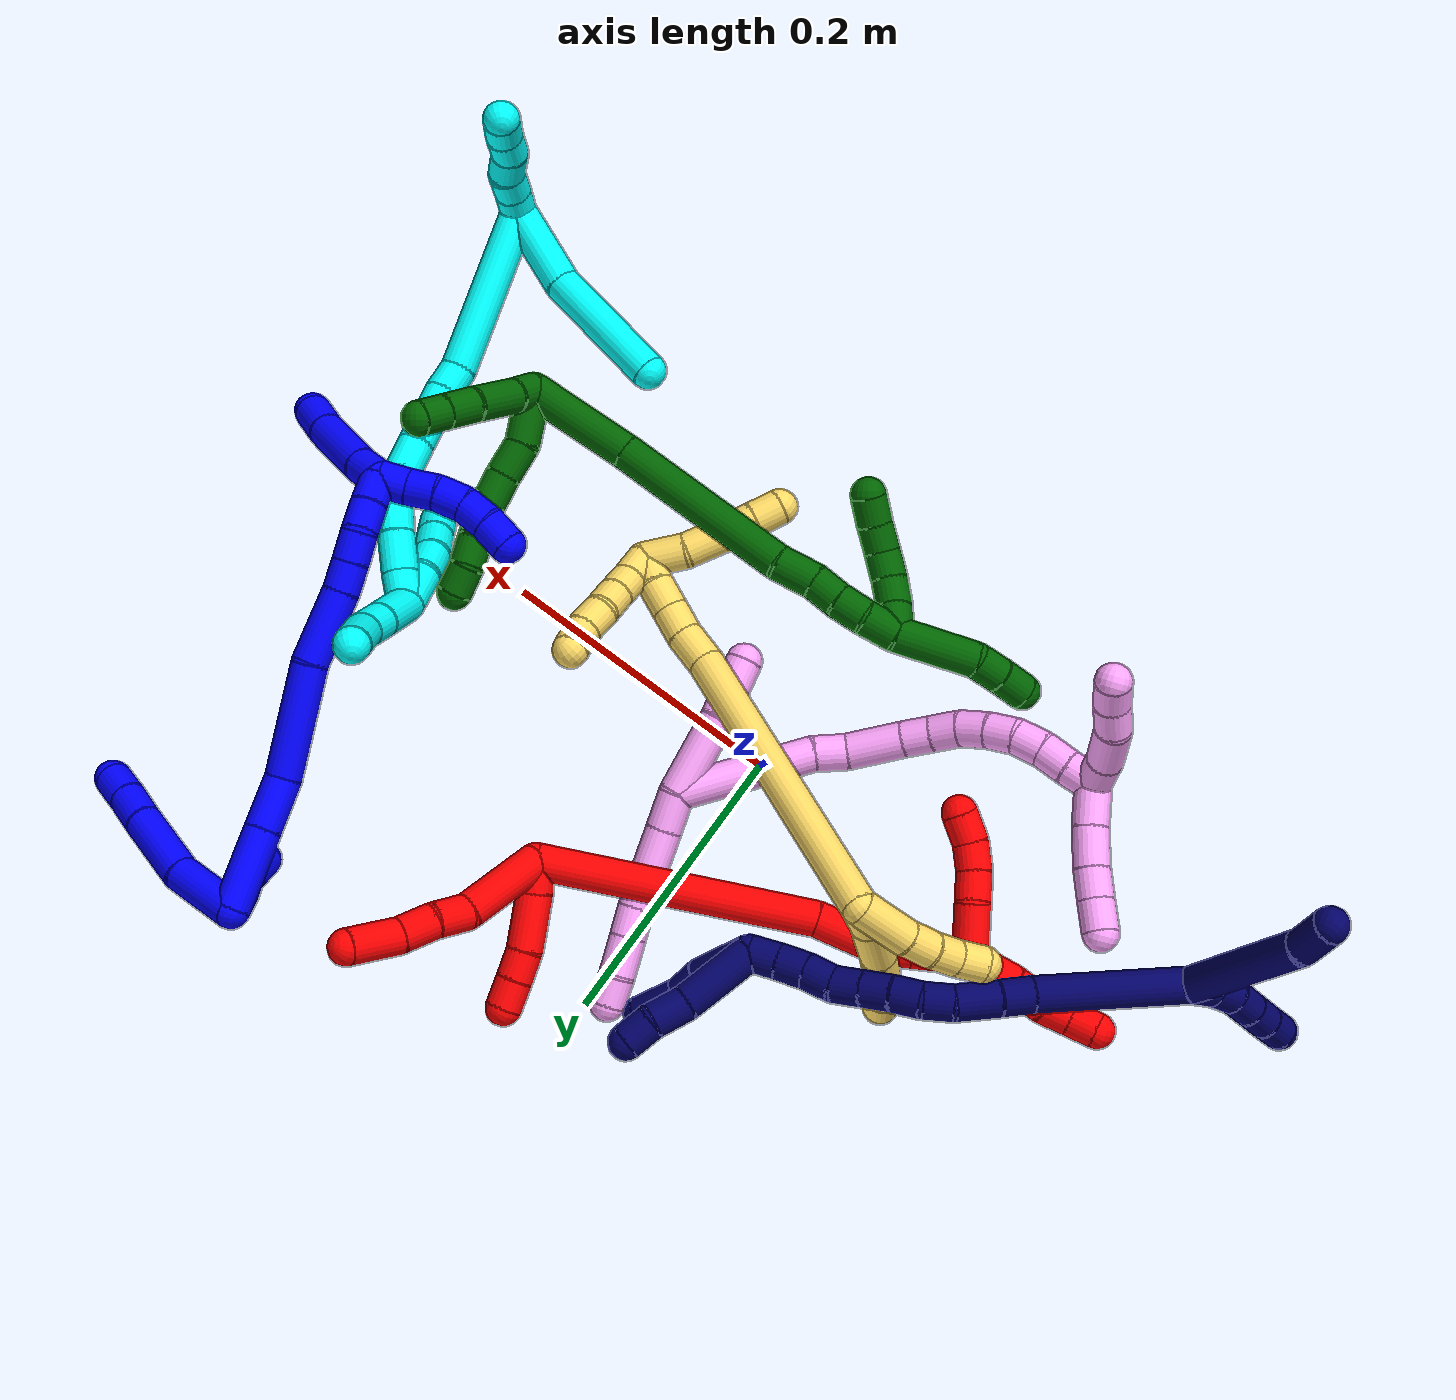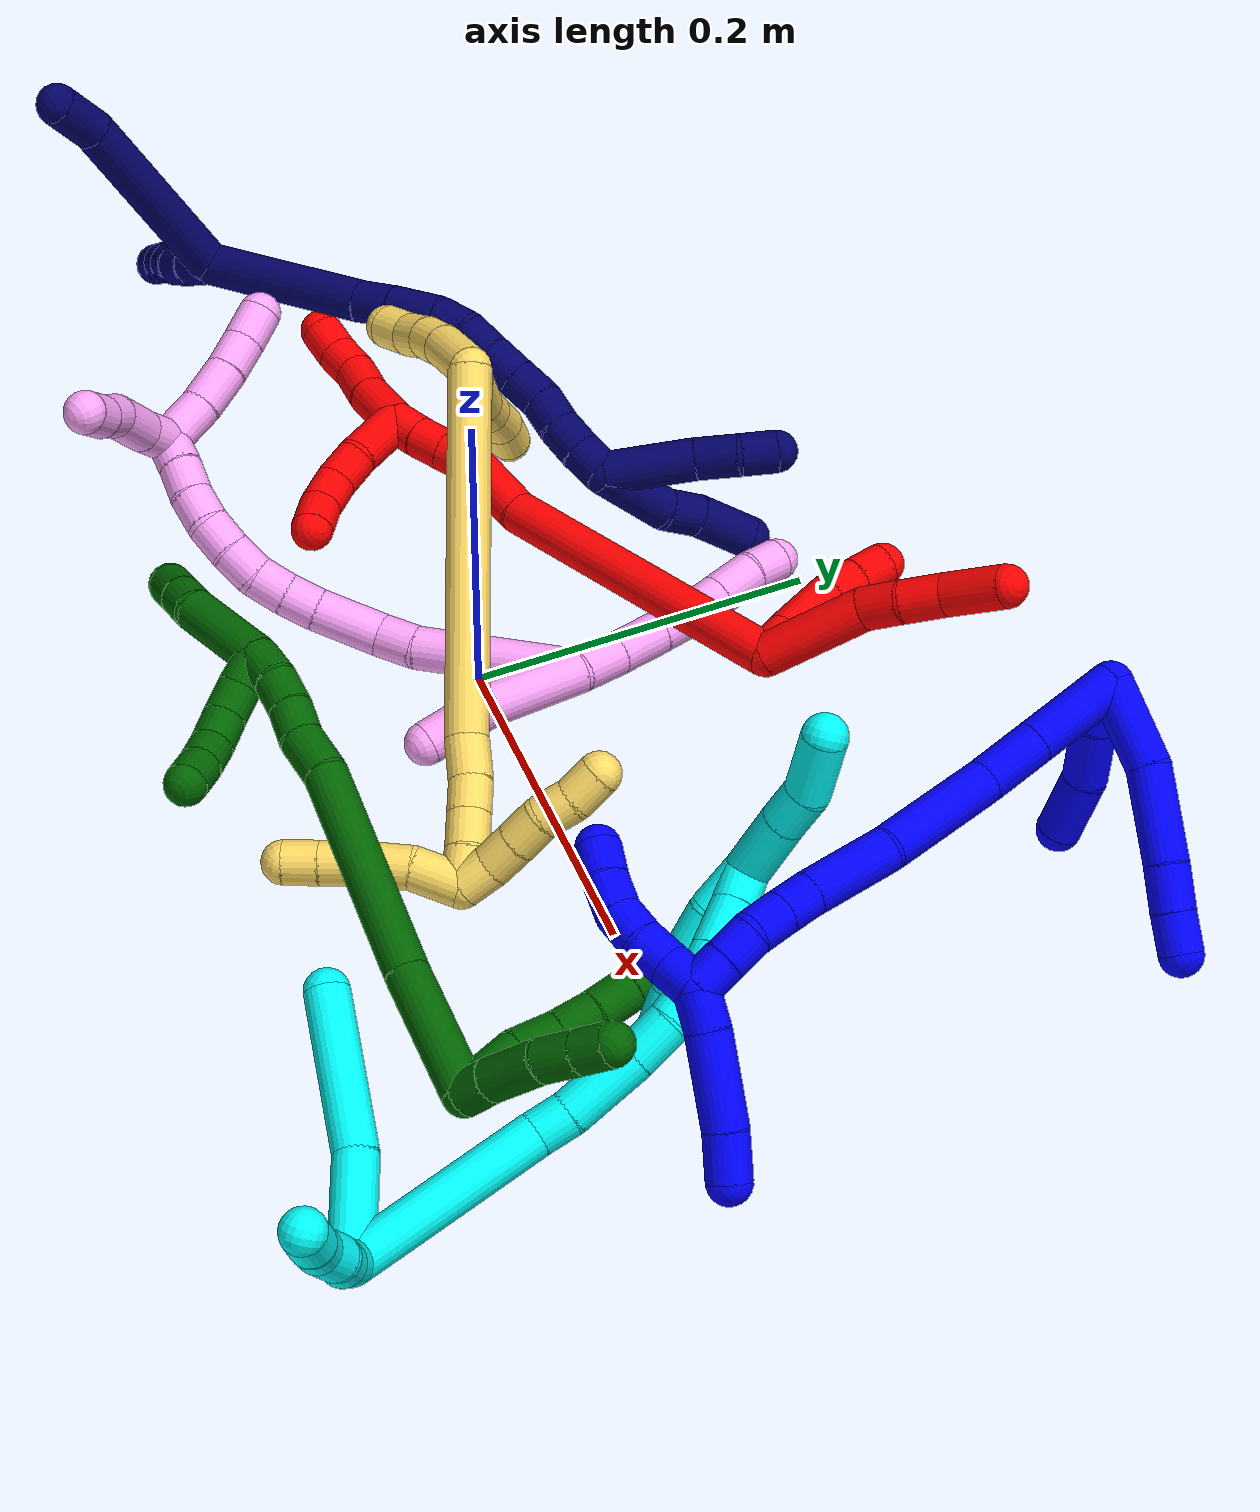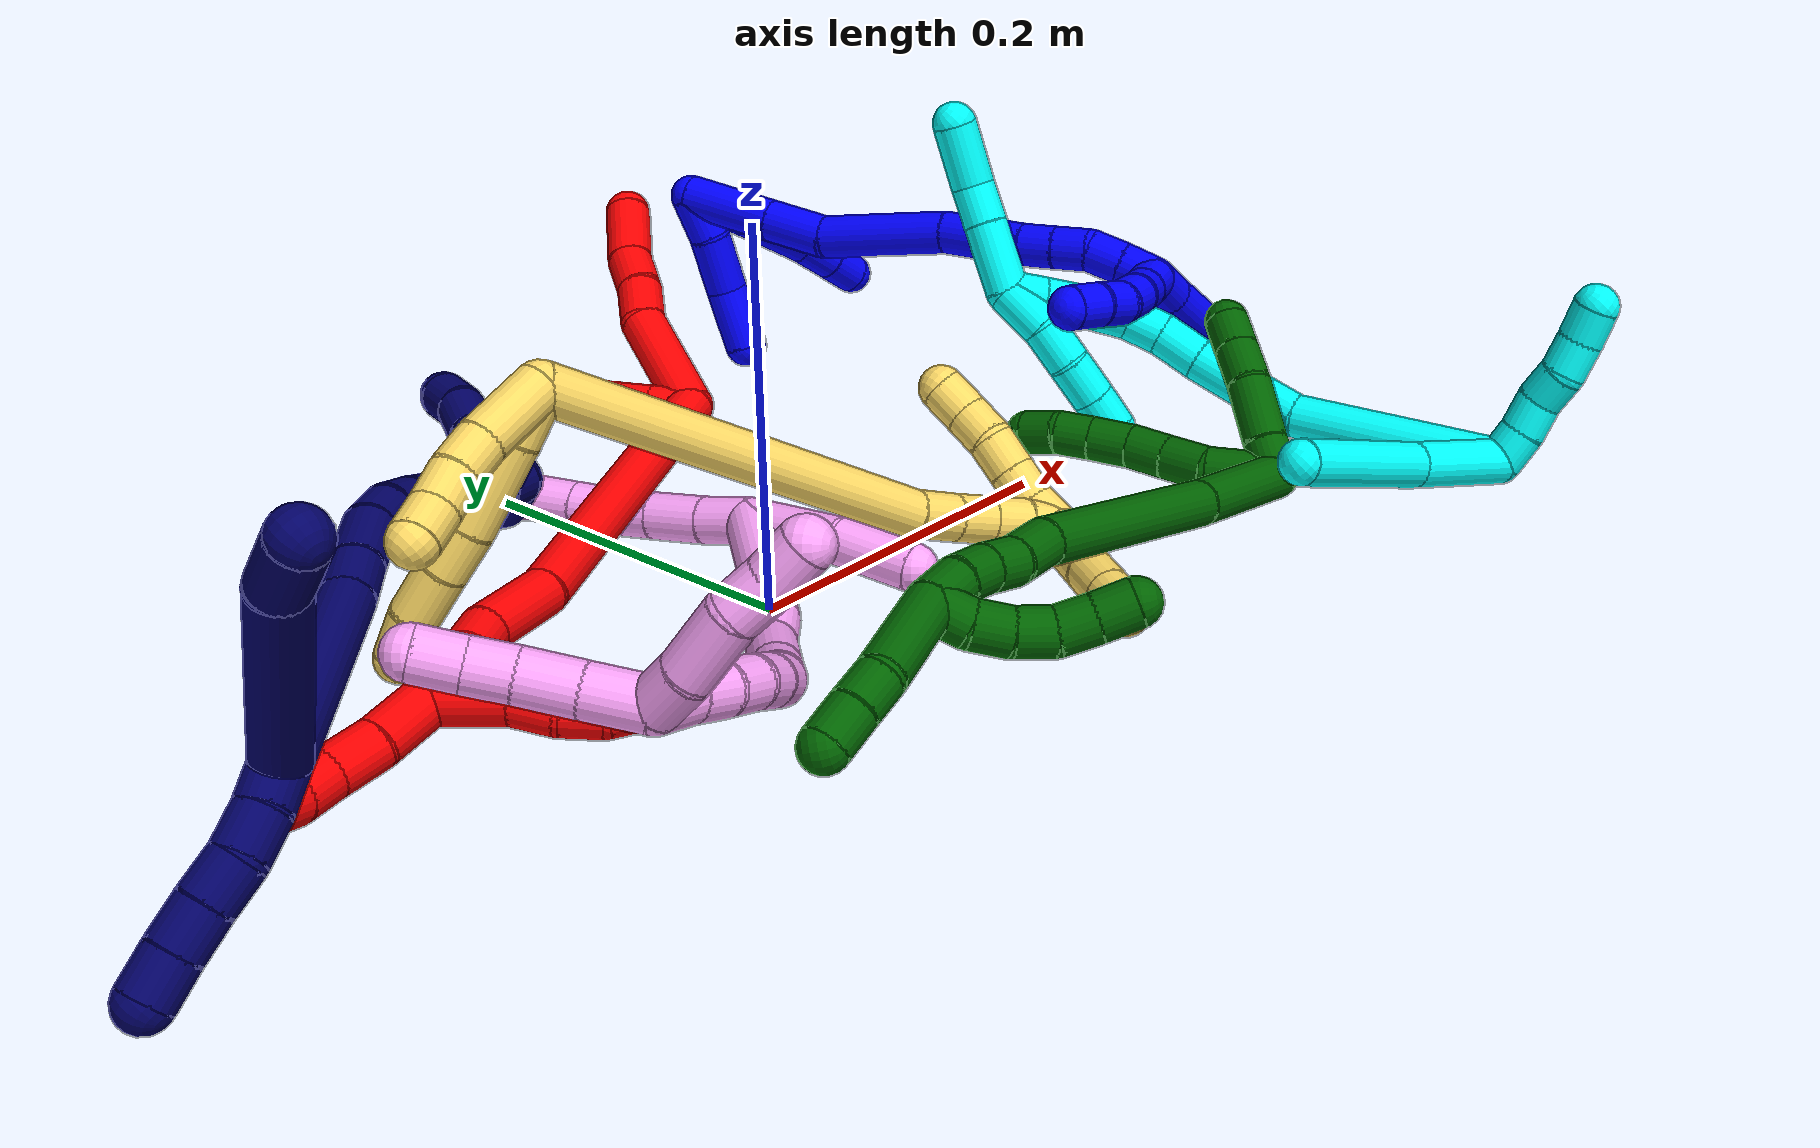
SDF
<sdf version="1.7">
 <world name="default">
  <plugin name="TubeGeneratorPlugin" filename="libtube_generator_plugin.so"/>
  <model name="photoneo_s_sensor">
   <static>1</static>
   <pose>0 0 2 1.57079 1.57079 3.14159</pose>
   <link name="link">
    <inertial><mass>0.1</mass></inertial>
    <sensor name="sensor" type="depth">
     <update_rate>30</update_rate>
     <camera>
      <horizontal_fov>1.22</horizontal_fov>
      <image><width>1920</width><height>1200</height><format>B8G8R8</format></image>
      <clip><near>0.1</near><far>4</far></clip>
      <depth_camera><output>points</output></depth_camera>
     </camera>
     <plugin name="camera_plugin" filename="libgazebo_ros_depth_camera.so">
      <baseline>0.2</baseline>
      <alwaysOn>1</alwaysOn>
      <updateRate>0.0</updateRate>
      <cameraName>camera_ir</cameraName>
      <imageTopicName>/camera/color/image_raw</imageTopicName>
      <cameraInfoTopicName>/camera/color/camera_info</cameraInfoTopicName>
      <depthImageTopicName>/camera/depth/image_raw</depthImageTopicName>
      <depthImageCameraInfoTopicName>/camera/depth/camera_info</depthImageCameraInfoTopicName>
      <pointCloudTopicName>/camera/depth/points</pointCloudTopicName>
      <frameName>fr_optical</frameName>
      <pointCloudCutoff>0.1</pointCloudCutoff>
      <pointCloudCutoffMax>2.0</pointCloudCutoffMax>
      <distortionK1>0</distortionK1>
      <distortionK2>0</distortionK2>
      <distortionK3>0</distortionK3>
      <distortionT1>0</distortionT1>
      <distortionT2>0</distortionT2>
      <CxPrime>0</CxPrime>
      <Cx>0</Cx>
      <Cy>0</Cy>
      <focalLength>0</focalLength>
      <hackBaseline>0</hackBaseline>
     </plugin>
    </sensor>
   </link>
  </model>
  <gravity>0 0 -9.8</gravity>
  <magnetic_field>6e-06 2.3e-05 -4.2e-05</magnetic_field>
  <atmosphere type="adiabatic"/>
  <physics name="default_physics" default="0" type="ode">
   <max_step_size>0.003</max_step_size>
   <real_time_factor>1</real_time_factor>
   <real_time_update_rate>1000</real_time_update_rate>
   <max_contacts>10000</max_contacts>
   <ode>
    <solver>
     <type>quick</type>
     <iters>100</iters>
     <sor>1.3</sor>
     <use_dynamic_moi_rescaling>0</use_dynamic_moi_rescaling>
    </solver>
    <constraints>
     <contact_max_correcting_vel>0</contact_max_correcting_vel>
     <contact_surface_layer>0.001</contact_surface_layer>
     <cfm>0</cfm>
     <erp>0.2</erp>
    </constraints>
   </ode>
  </physics>
  <scene><ambient>0.4 0.4 0.4 1</ambient><background>0.7 0.7 0.7 1</background><shadows>0</shadows></scene>
  <audio><device>default</device></audio>
  <spherical_coordinates>
   <surface_model>EARTH_WGS84</surface_model>
   <latitude_deg>0</latitude_deg>
   <longitude_deg>0</longitude_deg>
   <elevation>0</elevation>
   <heading_deg>0</heading_deg>
  </spherical_coordinates>
  <model name="bin">
   <static>1</static>
   <link name="bottom">
    <collision name="collision-bottom">
     <pose>0 0 -0.01 0 -0 0</pose>
     <geometry><box><size>0.8 0.6 0.02</size></box></geometry>
     <surface>
      <friction><ode><mu>100</mu><mu2>100</mu2></ode></friction>
      <contact><collide_bitmask>65535</collide_bitmask></contact>
     </surface>
    </collision>
   </link>
   <link name="west_wall">
    <collision name="collision-west_wall">
     <pose>-0.41 0 0.1 0 -0 0</pose>
     <geometry><box><size>0.02 0.6 0.2</size></box></geometry>
     <surface>
      <friction><ode><mu>100</mu><mu2>100</mu2></ode></friction>
      <contact><collide_bitmask>65535</collide_bitmask></contact>
     </surface>
    </collision>
   </link>
   <link name="east_wall">
    <collision name="collision-east_wall">
     <pose>0.41 0 0.1 0 -0 0</pose>
     <geometry><box><size>0.02 0.6 0.2</size></box></geometry>
     <surface>
      <friction><ode><mu>100</mu><mu2>100</mu2></ode></friction>
      <contact><collide_bitmask>65535</collide_bitmask></contact>
     </surface>
    </collision>
   </link>
   <link name="south_wall">
    <collision name="collision-south_wall">
     <pose>0 -0.31 0.1 0 -0 0</pose>
     <geometry><box><size>0.8 0.02 0.2</size></box></geometry>
     <surface>
      <friction><ode><mu>100</mu><mu2>100</mu2></ode></friction>
      <contact><collide_bitmask>65535</collide_bitmask></contact>
     </surface>
    </collision>
   </link>
   <link name="north_wall">
    <collision name="collision-north_wall">
     <pose>0 0.31 0.1 0 -0 0</pose>
     <geometry><box><size>0.8 0.02 0.2</size></box></geometry>
     <surface>
      <friction><ode><mu>100</mu><mu2>100</mu2></ode></friction>
      <contact><collide_bitmask>65535</collide_bitmask></contact>
     </surface>
    </collision>
   </link>
  </model>
  <model name="1">
   <static>0</static>
   <link name="1">
    <collision name="collision-cylinder-e_1_2_8">
     <pose>-0.001913 -0.002784 -0.024297 3.02752 -0.078078 -1.19988</pose>
     <geometry><cylinder><radius>0.0125</radius><length>0.049061</length></cylinder></geometry>
     <surface>
      <friction><ode><mu>1.16</mu><mu2>1.16</mu2><slip1>0</slip1><slip2>0</slip2></ode></friction>
      <contact><ode><kp>1e+06</kp><kd>1</kd><max_vel>0</max_vel><min_depth>0.001</min_depth></ode></contact>
     </surface>
    </collision>
    <visual name="visual-cylinder-e_1_2_8">
     <pose>-0.001913 -0.002784 -0.024297 3.02752 -0.078078 -1.19988</pose>
     <geometry><cylinder><radius>0.0125</radius><length>0.049061</length></cylinder></geometry>
     <material><ambient>0 0 1 1</ambient></material>
    </visual>
    <collision name="collision-cylinder-e_2_8_9">
     <pose>-0.006993 -0.014691 -0.073216 2.78672 -0.120001 -0.6465</pose>
     <geometry><cylinder><radius>0.0125</radius><length>0.052896</length></cylinder></geometry>
     <surface>
      <friction><ode><mu>1.16</mu><mu2>1.16</mu2><slip1>0</slip1><slip2>0</slip2></ode></friction>
      <contact><ode><kp>1e+06</kp><kd>1</kd><max_vel>0</max_vel><min_depth>0.001</min_depth></ode></contact>
     </surface>
    </collision>
    <visual name="visual-cylinder-e_2_8_9">
     <pose>-0.006993 -0.014691 -0.073216 2.78672 -0.120001 -0.6465</pose>
     <geometry><cylinder><radius>0.0125</radius><length>0.052896</length></cylinder></geometry>
     <material><ambient>0 0 1 1</ambient></material>
    </visual>
    <collision name="collision-cylinder-e_3_9_10">
     <pose>-0.012757 -0.028419 -0.109449 2.76414 -0.205064 -0.988256</pose>
     <geometry><cylinder><radius>0.0125</radius><length>0.025516</length></cylinder></geometry>
     <surface>
      <friction><ode><mu>1.16</mu><mu2>1.16</mu2><slip1>0</slip1><slip2>0</slip2></ode></friction>
      <contact><ode><kp>1e+06</kp><kd>1</kd><max_vel>0</max_vel><min_depth>0.001</min_depth></ode></contact>
     </surface>
    </collision>
    <visual name="visual-cylinder-e_3_9_10">
     <pose>-0.012757 -0.028419 -0.109449 2.76414 -0.205064 -0.988256</pose>
     <geometry><cylinder><radius>0.0125</radius><length>0.025516</length></cylinder></geometry>
     <material><ambient>0 0 1 1</ambient></material>
    </visual>
    <collision name="collision-cylinder-e_4_10_6">
     <pose>-0.017766 -0.036561 -0.131478 2.81415 -0.215697 -1.1603</pose>
     <geometry><cylinder><radius>0.0125</radius><length>0.022526</length></cylinder></geometry>
     <surface>
      <friction><ode><mu>1.16</mu><mu2>1.16</mu2><slip1>0</slip1><slip2>0</slip2></ode></friction>
      <contact><ode><kp>1e+06</kp><kd>1</kd><max_vel>0</max_vel><min_depth>0.001</min_depth></ode></contact>
     </surface>
    </collision>
    <visual name="visual-cylinder-e_4_10_6">
     <pose>-0.017766 -0.036561 -0.131478 2.81415 -0.215697 -1.1603</pose>
     <geometry><cylinder><radius>0.0125</radius><length>0.022526</length></cylinder></geometry>
     <material><ambient>0 0 1 1</ambient></material>
    </visual>
    <collision name="collision-cylinder-e_1_2_11">
     <pose>-0.009923 -0.006901 -0.006093 2.29412 -0.822853 -1.5376</pose>
     <geometry><cylinder><radius>0.0125</radius><length>0.027071</length></cylinder></geometry>
     <surface>
      <friction><ode><mu>1.16</mu><mu2>1.16</mu2><slip1>0</slip1><slip2>0</slip2></ode></friction>
      <contact><ode><kp>1e+06</kp><kd>1</kd><max_vel>0</max_vel><min_depth>0.001</min_depth></ode></contact>
     </surface>
    </collision>
    <visual name="visual-cylinder-e_1_2_11">
     <pose>-0.009923 -0.006901 -0.006093 2.29412 -0.822853 -1.5376</pose>
     <geometry><cylinder><radius>0.0125</radius><length>0.027071</length></cylinder></geometry>
     <material><ambient>0 0 1 1</ambient></material>
    </visual>
    <collision name="collision-cylinder-e_2_11_12">
     <pose>-0.033801 -0.019703 -0.021199 2.56185 -0.913427 -2.05045</pose>
     <geometry><cylinder><radius>0.0125</radius><length>0.035259</length></cylinder></geometry>
     <surface>
      <friction><ode><mu>1.16</mu><mu2>1.16</mu2><slip1>0</slip1><slip2>0</slip2></ode></friction>
      <contact><ode><kp>1e+06</kp><kd>1</kd><max_vel>0</max_vel><min_depth>0.001</min_depth></ode></contact>
     </surface>
    </collision>
    <visual name="visual-cylinder-e_2_11_12">
     <pose>-0.033801 -0.019703 -0.021199 2.56185 -0.913427 -2.05045</pose>
     <geometry><cylinder><radius>0.0125</radius><length>0.035259</length></cylinder></geometry>
     <material><ambient>0 0 1 1</ambient></material>
    </visual>
    <collision name="collision-cylinder-e_3_12_5">
     <pose>-0.062722 -0.035056 -0.03665 2.16886 -0.918219 -1.50359</pose>
     <geometry><cylinder><radius>0.0125</radius><length>0.03767</length></cylinder></geometry>
     <surface>
      <friction><ode><mu>1.16</mu><mu2>1.16</mu2><slip1>0</slip1><slip2>0</slip2></ode></friction>
      <contact><ode><kp>1e+06</kp><kd>1</kd><max_vel>0</max_vel><min_depth>0.001</min_depth></ode></contact>
     </surface>
    </collision>
    <visual name="visual-cylinder-e_3_12_5">
     <pose>-0.062722 -0.035056 -0.03665 2.16886 -0.918219 -1.50359</pose>
     <geometry><cylinder><radius>0.0125</radius><length>0.03767</length></cylinder></geometry>
     <material><ambient>0 0 1 1</ambient></material>
    </visual>
    <collision name="collision-cylinder-e_1_2_13">
     <pose>0.001744 -0.027111 -0.004319 1.72878 0.063452 0.074352</pose>
     <geometry><cylinder><radius>0.0125</radius><length>0.055017</length></cylinder></geometry>
     <surface>
      <friction><ode><mu>1.16</mu><mu2>1.16</mu2><slip1>0</slip1><slip2>0</slip2></ode></friction>
      <contact><ode><kp>1e+06</kp><kd>1</kd><max_vel>0</max_vel><min_depth>0.001</min_depth></ode></contact>
     </surface>
    </collision>
    <visual name="visual-cylinder-e_1_2_13">
     <pose>0.001744 -0.027111 -0.004319 1.72878 0.063452 0.074352</pose>
     <geometry><cylinder><radius>0.0125</radius><length>0.055017</length></cylinder></geometry>
     <material><ambient>0 0 1 1</ambient></material>
    </visual>
    <collision name="collision-cylinder-e_2_13_14">
     <pose>0.004691 -0.072206 -0.011495 1.72832 0.065958 0.077251</pose>
     <geometry><cylinder><radius>0.0125</radius><length>0.036496</length></cylinder></geometry>
     <surface>
      <friction><ode><mu>1.16</mu><mu2>1.16</mu2><slip1>0</slip1><slip2>0</slip2></ode></friction>
      <contact><ode><kp>1e+06</kp><kd>1</kd><max_vel>0</max_vel><min_depth>0.001</min_depth></ode></contact>
     </surface>
    </collision>
    <visual name="visual-cylinder-e_2_13_14">
     <pose>0.004691 -0.072206 -0.011495 1.72832 0.065958 0.077251</pose>
     <geometry><cylinder><radius>0.0125</radius><length>0.036496</length></cylinder></geometry>
     <material><ambient>0 0 1 1</ambient></material>
    </visual>
    <collision name="collision-cylinder-e_3_14_15">
     <pose>0.019963 -0.125635 -0.020031 1.72968 0.373512 0.436239</pose>
     <geometry><cylinder><radius>0.0125</radius><length>0.077113</length></cylinder></geometry>
     <surface>
      <friction><ode><mu>1.16</mu><mu2>1.16</mu2><slip1>0</slip1><slip2>0</slip2></ode></friction>
      <contact><ode><kp>1e+06</kp><kd>1</kd><max_vel>0</max_vel><min_depth>0.001</min_depth></ode></contact>
     </surface>
    </collision>
    <visual name="visual-cylinder-e_3_14_15">
     <pose>0.019963 -0.125635 -0.020031 1.72968 0.373512 0.436239</pose>
     <geometry><cylinder><radius>0.0125</radius><length>0.077113</length></cylinder></geometry>
     <material><ambient>0 0 1 1</ambient></material>
    </visual>
    <collision name="collision-cylinder-e_4_15_16">
     <pose>0.038739 -0.18586 -0.026982 1.62203 0.187485 0.197284</pose>
     <geometry><cylinder><radius>0.0125</radius><length>0.050509</length></cylinder></geometry>
     <surface>
      <friction><ode><mu>1.16</mu><mu2>1.16</mu2><slip1>0</slip1><slip2>0</slip2></ode></friction>
      <contact><ode><kp>1e+06</kp><kd>1</kd><max_vel>0</max_vel><min_depth>0.001</min_depth></ode></contact>
     </surface>
    </collision>
    <visual name="visual-cylinder-e_4_15_16">
     <pose>0.038739 -0.18586 -0.026982 1.62203 0.187485 0.197284</pose>
     <geometry><cylinder><radius>0.0125</radius><length>0.050509</length></cylinder></geometry>
     <material><ambient>0 0 1 1</ambient></material>
    </visual>
    <collision name="collision-cylinder-e_5_16_17">
     <pose>0.045986 -0.220297 -0.029457 1.69492 0.255289 0.288677</pose>
     <geometry><cylinder><radius>0.0125</radius><length>0.020117</length></cylinder></geometry>
     <surface>
      <friction><ode><mu>1.16</mu><mu2>1.16</mu2><slip1>0</slip1><slip2>0</slip2></ode></friction>
      <contact><ode><kp>1e+06</kp><kd>1</kd><max_vel>0</max_vel><min_depth>0.001</min_depth></ode></contact>
     </surface>
    </collision>
    <visual name="visual-cylinder-e_5_16_17">
     <pose>0.045986 -0.220297 -0.029457 1.69492 0.255289 0.288677</pose>
     <geometry><cylinder><radius>0.0125</radius><length>0.020117</length></cylinder></geometry>
     <material><ambient>0 0 1 1</ambient></material>
    </visual>
    <collision name="collision-cylinder-e_6_17_18">
     <pose>0.051205 -0.239721 -0.032138 1.72079 0.264814 0.307214</pose>
     <geometry><cylinder><radius>0.0125</radius><length>0.020467</length></cylinder></geometry>
     <surface>
      <friction><ode><mu>1.16</mu><mu2>1.16</mu2><slip1>0</slip1><slip2>0</slip2></ode></friction>
      <contact><ode><kp>1e+06</kp><kd>1</kd><max_vel>0</max_vel><min_depth>0.001</min_depth></ode></contact>
     </surface>
    </collision>
    <visual name="visual-cylinder-e_6_17_18">
     <pose>0.051205 -0.239721 -0.032138 1.72079 0.264814 0.307214</pose>
     <geometry><cylinder><radius>0.0125</radius><length>0.020467</length></cylinder></geometry>
     <material><ambient>0 0 1 1</ambient></material>
    </visual>
    <collision name="collision-cylinder-e_7_18_19">
     <pose>0.053534 -0.259222 -0.036307 1.84071 -0.034579 -0.045441</pose>
     <geometry><cylinder><radius>0.0125</radius><length>0.020214</length></cylinder></geometry>
     <surface>
      <friction><ode><mu>1.16</mu><mu2>1.16</mu2><slip1>0</slip1><slip2>0</slip2></ode></friction>
      <contact><ode><kp>1e+06</kp><kd>1</kd><max_vel>0</max_vel><min_depth>0.001</min_depth></ode></contact>
     </surface>
    </collision>
    <visual name="visual-cylinder-e_7_18_19">
     <pose>0.053534 -0.259222 -0.036307 1.84071 -0.034579 -0.045441</pose>
     <geometry><cylinder><radius>0.0125</radius><length>0.020214</length></cylinder></geometry>
     <material><ambient>0 0 1 1</ambient></material>
    </visual>
    <collision name="collision-cylinder-e_8_19_1">
     <pose>0.052372 -0.278627 -0.041551 1.82868 -0.08099 -0.105082</pose>
     <geometry><cylinder><radius>0.0125</radius><length>0.020066</length></cylinder></geometry>
     <surface>
      <friction><ode><mu>1.16</mu><mu2>1.16</mu2><slip1>0</slip1><slip2>0</slip2></ode></friction>
      <contact><ode><kp>1e+06</kp><kd>1</kd><max_vel>0</max_vel><min_depth>0.001</min_depth></ode></contact>
     </surface>
    </collision>
    <visual name="visual-cylinder-e_8_19_1">
     <pose>0.052372 -0.278627 -0.041551 1.82868 -0.08099 -0.105082</pose>
     <geometry><cylinder><radius>0.0125</radius><length>0.020066</length></cylinder></geometry>
     <material><ambient>0 0 1 1</ambient></material>
    </visual>
    <collision name="collision-cylinder-e_1_1_20">
     <pose>0.048452 -0.290526 -0.054448 2.92933 -0.285712 -1.86664</pose>
     <geometry><cylinder><radius>0.0125</radius><length>0.022063</length></cylinder></geometry>
     <surface>
      <friction><ode><mu>1.16</mu><mu2>1.16</mu2><slip1>0</slip1><slip2>0</slip2></ode></friction>
      <contact><ode><kp>1e+06</kp><kd>1</kd><max_vel>0</max_vel><min_depth>0.001</min_depth></ode></contact>
     </surface>
    </collision>
    <visual name="visual-cylinder-e_1_1_20">
     <pose>0.048452 -0.290526 -0.054448 2.92933 -0.285712 -1.86664</pose>
     <geometry><cylinder><radius>0.0125</radius><length>0.022063</length></cylinder></geometry>
     <material><ambient>0 0 1 1</ambient></material>
    </visual>
    <collision name="collision-cylinder-e_2_20_21">
     <pose>0.038033 -0.300518 -0.088229 2.82171 -0.287879 -1.46396</pose>
     <geometry><cylinder><radius>0.0125</radius><length>0.051491</length></cylinder></geometry>
     <surface>
      <friction><ode><mu>1.16</mu><mu2>1.16</mu2><slip1>0</slip1><slip2>0</slip2></ode></friction>
      <contact><ode><kp>1e+06</kp><kd>1</kd><max_vel>0</max_vel><min_depth>0.001</min_depth></ode></contact>
     </surface>
    </collision>
    <visual name="visual-cylinder-e_2_20_21">
     <pose>0.038033 -0.300518 -0.088229 2.82171 -0.287879 -1.46396</pose>
     <geometry><cylinder><radius>0.0125</radius><length>0.051491</length></cylinder></geometry>
     <material><ambient>0 0 1 1</ambient></material>
    </visual>
    <collision name="collision-cylinder-e_3_21_4">
     <pose>0.026478 -0.313448 -0.12307 2.7163 -0.326831 -1.30439</pose>
     <geometry><cylinder><radius>0.0125</radius><length>0.026446</length></cylinder></geometry>
     <surface>
      <friction><ode><mu>1.16</mu><mu2>1.16</mu2><slip1>0</slip1><slip2>0</slip2></ode></friction>
      <contact><ode><kp>1e+06</kp><kd>1</kd><max_vel>0</max_vel><min_depth>0.001</min_depth></ode></contact>
     </surface>
    </collision>
    <visual name="visual-cylinder-e_3_21_4">
     <pose>0.026478 -0.313448 -0.12307 2.7163 -0.326831 -1.30439</pose>
     <geometry><cylinder><radius>0.0125</radius><length>0.026446</length></cylinder></geometry>
     <material><ambient>0 0 1 1</ambient></material>
    </visual>
    <collision name="collision-cylinder-e_1_1_22">
     <pose>0.048051 -0.290622 -0.035031 0.250983 -0.358647 -0.045728</pose>
     <geometry><cylinder><radius>0.0125</radius><length>0.02</length></cylinder></geometry>
     <surface>
      <friction><ode><mu>1.16</mu><mu2>1.16</mu2><slip1>0</slip1><slip2>0</slip2></ode></friction>
      <contact><ode><kp>1e+06</kp><kd>1</kd><max_vel>0</max_vel><min_depth>0.001</min_depth></ode></contact>
     </surface>
    </collision>
    <visual name="visual-cylinder-e_1_1_22">
     <pose>0.048051 -0.290622 -0.035031 0.250983 -0.358647 -0.045728</pose>
     <geometry><cylinder><radius>0.0125</radius><length>0.02</length></cylinder></geometry>
     <material><ambient>0 0 1 1</ambient></material>
    </visual>
    <collision name="collision-cylinder-e_2_22_23">
     <pose>0.042765 -0.295601 -0.016484 0.273066 -0.178534 -0.024592</pose>
     <geometry><cylinder><radius>0.0125</radius><length>0.02</length></cylinder></geometry>
     <surface>
      <friction><ode><mu>1.16</mu><mu2>1.16</mu2><slip1>0</slip1><slip2>0</slip2></ode></friction>
      <contact><ode><kp>1e+06</kp><kd>1</kd><max_vel>0</max_vel><min_depth>0.001</min_depth></ode></contact>
     </surface>
    </collision>
    <visual name="visual-cylinder-e_2_22_23">
     <pose>0.042765 -0.295601 -0.016484 0.273066 -0.178534 -0.024592</pose>
     <geometry><cylinder><radius>0.0125</radius><length>0.02</length></cylinder></geometry>
     <material><ambient>0 0 1 1</ambient></material>
    </visual>
    <collision name="collision-cylinder-e_3_23_24">
     <pose>0.038024 -0.299253 0.00249 0.104696 -0.300981 -0.01589</pose>
     <geometry><cylinder><radius>0.0125</radius><length>0.02</length></cylinder></geometry>
     <surface>
      <friction><ode><mu>1.16</mu><mu2>1.16</mu2><slip1>0</slip1><slip2>0</slip2></ode></friction>
      <contact><ode><kp>1e+06</kp><kd>1</kd><max_vel>0</max_vel><min_depth>0.001</min_depth></ode></contact>
     </surface>
    </collision>
    <visual name="visual-cylinder-e_3_23_24">
     <pose>0.038024 -0.299253 0.00249 0.104696 -0.300981 -0.01589</pose>
     <geometry><cylinder><radius>0.0125</radius><length>0.02</length></cylinder></geometry>
     <material><ambient>0 0 1 1</ambient></material>
    </visual>
    <collision name="collision-cylinder-e_4_24_25">
     <pose>0.032899 -0.298339 0.021563 -0.197096 -0.217836 0.021622</pose>
     <geometry><cylinder><radius>0.0125</radius><length>0.02</length></cylinder></geometry>
     <surface>
      <friction><ode><mu>1.16</mu><mu2>1.16</mu2><slip1>0</slip1><slip2>0</slip2></ode></friction>
      <contact><ode><kp>1e+06</kp><kd>1</kd><max_vel>0</max_vel><min_depth>0.001</min_depth></ode></contact>
     </surface>
    </collision>
    <visual name="visual-cylinder-e_4_24_25">
     <pose>0.032899 -0.298339 0.021563 -0.197096 -0.217836 0.021622</pose>
     <geometry><cylinder><radius>0.0125</radius><length>0.02</length></cylinder></geometry>
     <material><ambient>0 0 1 1</ambient></material>
    </visual>
    <collision name="collision-cylinder-e_5_25_3">
     <pose>0.027695 -0.293242 0.040115 -0.340969 -0.309153 0.053638</pose>
     <geometry><cylinder><radius>0.0125</radius><length>0.02</length></cylinder></geometry>
     <surface>
      <friction><ode><mu>1.16</mu><mu2>1.16</mu2><slip1>0</slip1><slip2>0</slip2></ode></friction>
      <contact><ode><kp>1e+06</kp><kd>1</kd><max_vel>0</max_vel><min_depth>0.001</min_depth></ode></contact>
     </surface>
    </collision>
    <visual name="visual-cylinder-e_5_25_3">
     <pose>0.027695 -0.293242 0.040115 -0.340969 -0.309153 0.053638</pose>
     <geometry><cylinder><radius>0.0125</radius><length>0.02</length></cylinder></geometry>
     <material><ambient>0 0 1 1</ambient></material>
    </visual>
    <collision name="collision-sphere-3">
     <pose>0.024652 -0.290057 0.049093 0 -0 0</pose>
     <geometry><sphere><radius>0.0125</radius></sphere></geometry>
     <surface>
      <friction><ode><mu>1.16</mu><mu2>1.16</mu2><slip1>0</slip1><slip2>0</slip2></ode></friction>
      <contact><ode><kp>1e+06</kp><kd>1</kd><max_vel>0</max_vel><min_depth>0.001</min_depth></ode></contact>
     </surface>
    </collision>
    <visual name="visual-sphere-3">
     <pose>0.024652 -0.290057 0.049093 0 -0 0</pose>
     <geometry><sphere><radius>0.0125</radius></sphere></geometry>
     <material><ambient>0 0 1 1</ambient></material>
    </visual>
    <collision name="collision-sphere-25">
     <pose>0.030737 -0.296427 0.031138 0 -0 0</pose>
     <geometry><sphere><radius>0.0125</radius></sphere></geometry>
     <surface>
      <friction><ode><mu>1.16</mu><mu2>1.16</mu2><slip1>0</slip1><slip2>0</slip2></ode></friction>
      <contact><ode><kp>1e+06</kp><kd>1</kd><max_vel>0</max_vel><min_depth>0.001</min_depth></ode></contact>
     </surface>
    </collision>
    <visual name="visual-sphere-25">
     <pose>0.030737 -0.296427 0.031138 0 -0 0</pose>
     <geometry><sphere><radius>0.0125</radius></sphere></geometry>
     <material><ambient>0 0 1 1</ambient></material>
    </visual>
    <collision name="collision-sphere-24">
     <pose>0.03506 -0.300251 0.011988 0 -0 0</pose>
     <geometry><sphere><radius>0.0125</radius></sphere></geometry>
     <surface>
      <friction><ode><mu>1.16</mu><mu2>1.16</mu2><slip1>0</slip1><slip2>0</slip2></ode></friction>
      <contact><ode><kp>1e+06</kp><kd>1</kd><max_vel>0</max_vel><min_depth>0.001</min_depth></ode></contact>
     </surface>
    </collision>
    <visual name="visual-sphere-24">
     <pose>0.03506 -0.300251 0.011988 0 -0 0</pose>
     <geometry><sphere><radius>0.0125</radius></sphere></geometry>
     <material><ambient>0 0 1 1</ambient></material>
    </visual>
    <collision name="collision-sphere-23">
     <pose>0.040989 -0.298255 -0.007008 0 -0 0</pose>
     <geometry><sphere><radius>0.0125</radius></sphere></geometry>
     <surface>
      <friction><ode><mu>1.16</mu><mu2>1.16</mu2><slip1>0</slip1><slip2>0</slip2></ode></friction>
      <contact><ode><kp>1e+06</kp><kd>1</kd><max_vel>0</max_vel><min_depth>0.001</min_depth></ode></contact>
     </surface>
    </collision>
    <visual name="visual-sphere-23">
     <pose>0.040989 -0.298255 -0.007008 0 -0 0</pose>
     <geometry><sphere><radius>0.0125</radius></sphere></geometry>
     <material><ambient>0 0 1 1</ambient></material>
    </visual>
    <collision name="collision-sphere-22">
     <pose>0.044541 -0.292947 -0.025961 0 -0 0</pose>
     <geometry><sphere><radius>0.0125</radius></sphere></geometry>
     <surface>
      <friction><ode><mu>1.16</mu><mu2>1.16</mu2><slip1>0</slip1><slip2>0</slip2></ode></friction>
      <contact><ode><kp>1e+06</kp><kd>1</kd><max_vel>0</max_vel><min_depth>0.001</min_depth></ode></contact>
     </surface>
    </collision>
    <visual name="visual-sphere-22">
     <pose>0.044541 -0.292947 -0.025961 0 -0 0</pose>
     <geometry><sphere><radius>0.0125</radius></sphere></geometry>
     <material><ambient>0 0 1 1</ambient></material>
    </visual>
    <collision name="collision-sphere-4">
     <pose>0.022233 -0.318615 -0.134478 0 -0 0</pose>
     <geometry><sphere><radius>0.0125</radius></sphere></geometry>
     <surface>
      <friction><ode><mu>1.16</mu><mu2>1.16</mu2><slip1>0</slip1><slip2>0</slip2></ode></friction>
      <contact><ode><kp>1e+06</kp><kd>1</kd><max_vel>0</max_vel><min_depth>0.001</min_depth></ode></contact>
     </surface>
    </collision>
    <visual name="visual-sphere-4">
     <pose>0.022233 -0.318615 -0.134478 0 -0 0</pose>
     <geometry><sphere><radius>0.0125</radius></sphere></geometry>
     <material><ambient>0 0 1 1</ambient></material>
    </visual>
    <collision name="collision-sphere-21">
     <pose>0.030723 -0.308281 -0.111663 0 -0 0</pose>
     <geometry><sphere><radius>0.0125</radius></sphere></geometry>
     <surface>
      <friction><ode><mu>1.16</mu><mu2>1.16</mu2><slip1>0</slip1><slip2>0</slip2></ode></friction>
      <contact><ode><kp>1e+06</kp><kd>1</kd><max_vel>0</max_vel><min_depth>0.001</min_depth></ode></contact>
     </surface>
    </collision>
    <visual name="visual-sphere-21">
     <pose>0.030723 -0.308281 -0.111663 0 -0 0</pose>
     <geometry><sphere><radius>0.0125</radius></sphere></geometry>
     <material><ambient>0 0 1 1</ambient></material>
    </visual>
    <collision name="collision-sphere-20">
     <pose>0.045342 -0.292756 -0.064795 0 -0 0</pose>
     <geometry><sphere><radius>0.0125</radius></sphere></geometry>
     <surface>
      <friction><ode><mu>1.16</mu><mu2>1.16</mu2><slip1>0</slip1><slip2>0</slip2></ode></friction>
      <contact><ode><kp>1e+06</kp><kd>1</kd><max_vel>0</max_vel><min_depth>0.001</min_depth></ode></contact>
     </surface>
    </collision>
    <visual name="visual-sphere-20">
     <pose>0.045342 -0.292756 -0.064795 0 -0 0</pose>
     <geometry><sphere><radius>0.0125</radius></sphere></geometry>
     <material><ambient>0 0 1 1</ambient></material>
    </visual>
    <collision name="collision-sphere-11">
     <pose>-0.019846 -0.013802 -0.012187 0 -0 0</pose>
     <geometry><sphere><radius>0.0125</radius></sphere></geometry>
     <surface>
      <friction><ode><mu>1.16</mu><mu2>1.16</mu2><slip1>0</slip1><slip2>0</slip2></ode></friction>
      <contact><ode><kp>1e+06</kp><kd>1</kd><max_vel>0</max_vel><min_depth>0.001</min_depth></ode></contact>
     </surface>
    </collision>
    <visual name="visual-sphere-11">
     <pose>-0.019846 -0.013802 -0.012187 0 -0 0</pose>
     <geometry><sphere><radius>0.0125</radius></sphere></geometry>
     <material><ambient>0 0 1 1</ambient></material>
    </visual>
    <collision name="collision-sphere-6">
     <pose>-0.020176 -0.040099 -0.141896 0 -0 0</pose>
     <geometry><sphere><radius>0.0125</radius></sphere></geometry>
     <surface>
      <friction><ode><mu>1.16</mu><mu2>1.16</mu2><slip1>0</slip1><slip2>0</slip2></ode></friction>
      <contact><ode><kp>1e+06</kp><kd>1</kd><max_vel>0</max_vel><min_depth>0.001</min_depth></ode></contact>
     </surface>
    </collision>
    <visual name="visual-sphere-6">
     <pose>-0.020176 -0.040099 -0.141896 0 -0 0</pose>
     <geometry><sphere><radius>0.0125</radius></sphere></geometry>
     <material><ambient>0 0 1 1</ambient></material>
    </visual>
    <collision name="collision-sphere-10">
     <pose>-0.015355 -0.033022 -0.121061 0 -0 0</pose>
     <geometry><sphere><radius>0.0125</radius></sphere></geometry>
     <surface>
      <friction><ode><mu>1.16</mu><mu2>1.16</mu2><slip1>0</slip1><slip2>0</slip2></ode></friction>
      <contact><ode><kp>1e+06</kp><kd>1</kd><max_vel>0</max_vel><min_depth>0.001</min_depth></ode></contact>
     </surface>
    </collision>
    <visual name="visual-sphere-10">
     <pose>-0.015355 -0.033022 -0.121061 0 -0 0</pose>
     <geometry><sphere><radius>0.0125</radius></sphere></geometry>
     <material><ambient>0 0 1 1</ambient></material>
    </visual>
    <collision name="collision-sphere-9">
     <pose>-0.010159 -0.023815 -0.097837 0 -0 0</pose>
     <geometry><sphere><radius>0.0125</radius></sphere></geometry>
     <surface>
      <friction><ode><mu>1.16</mu><mu2>1.16</mu2><slip1>0</slip1><slip2>0</slip2></ode></friction>
      <contact><ode><kp>1e+06</kp><kd>1</kd><max_vel>0</max_vel><min_depth>0.001</min_depth></ode></contact>
     </surface>
    </collision>
    <visual name="visual-sphere-9">
     <pose>-0.010159 -0.023815 -0.097837 0 -0 0</pose>
     <geometry><sphere><radius>0.0125</radius></sphere></geometry>
     <material><ambient>0 0 1 1</ambient></material>
    </visual>
    <collision name="collision-sphere-2">
     <geometry><sphere><radius>0.0125</radius></sphere></geometry>
     <surface>
      <friction><ode><mu>1.16</mu><mu2>1.16</mu2><slip1>0</slip1><slip2>0</slip2></ode></friction>
      <contact><ode><kp>1e+06</kp><kd>1</kd><max_vel>0</max_vel><min_depth>0.001</min_depth></ode></contact>
     </surface>
    </collision>
    <visual name="visual-sphere-2">
     <geometry><sphere><radius>0.0125</radius></sphere></geometry>
     <material><ambient>0 0 1 1</ambient></material>
    </visual>
    <collision name="collision-sphere-19">
     <pose>0.053184 -0.268957 -0.039001 0 -0 0</pose>
     <geometry><sphere><radius>0.0125</radius></sphere></geometry>
     <surface>
      <friction><ode><mu>1.16</mu><mu2>1.16</mu2><slip1>0</slip1><slip2>0</slip2></ode></friction>
      <contact><ode><kp>1e+06</kp><kd>1</kd><max_vel>0</max_vel><min_depth>0.001</min_depth></ode></contact>
     </surface>
    </collision>
    <visual name="visual-sphere-19">
     <pose>0.053184 -0.268957 -0.039001 0 -0 0</pose>
     <geometry><sphere><radius>0.0125</radius></sphere></geometry>
     <material><ambient>0 0 1 1</ambient></material>
    </visual>
    <collision name="collision-sphere-8">
     <pose>-0.003827 -0.005568 -0.048594 0 -0 0</pose>
     <geometry><sphere><radius>0.0125</radius></sphere></geometry>
     <surface>
      <friction><ode><mu>1.16</mu><mu2>1.16</mu2><slip1>0</slip1><slip2>0</slip2></ode></friction>
      <contact><ode><kp>1e+06</kp><kd>1</kd><max_vel>0</max_vel><min_depth>0.001</min_depth></ode></contact>
     </surface>
    </collision>
    <visual name="visual-sphere-8">
     <pose>-0.003827 -0.005568 -0.048594 0 -0 0</pose>
     <geometry><sphere><radius>0.0125</radius></sphere></geometry>
     <material><ambient>0 0 1 1</ambient></material>
    </visual>
    <collision name="collision-sphere-12">
     <pose>-0.047757 -0.025604 -0.030211 0 -0 0</pose>
     <geometry><sphere><radius>0.0125</radius></sphere></geometry>
     <surface>
      <friction><ode><mu>1.16</mu><mu2>1.16</mu2><slip1>0</slip1><slip2>0</slip2></ode></friction>
      <contact><ode><kp>1e+06</kp><kd>1</kd><max_vel>0</max_vel><min_depth>0.001</min_depth></ode></contact>
     </surface>
    </collision>
    <visual name="visual-sphere-12">
     <pose>-0.047757 -0.025604 -0.030211 0 -0 0</pose>
     <geometry><sphere><radius>0.0125</radius></sphere></geometry>
     <material><ambient>0 0 1 1</ambient></material>
    </visual>
    <collision name="collision-sphere-5">
     <pose>-0.077686 -0.044508 -0.04309 0 -0 0</pose>
     <geometry><sphere><radius>0.0125</radius></sphere></geometry>
     <surface>
      <friction><ode><mu>1.16</mu><mu2>1.16</mu2><slip1>0</slip1><slip2>0</slip2></ode></friction>
      <contact><ode><kp>1e+06</kp><kd>1</kd><max_vel>0</max_vel><min_depth>0.001</min_depth></ode></contact>
     </surface>
    </collision>
    <visual name="visual-sphere-5">
     <pose>-0.077686 -0.044508 -0.04309 0 -0 0</pose>
     <geometry><sphere><radius>0.0125</radius></sphere></geometry>
     <material><ambient>0 0 1 1</ambient></material>
    </visual>
    <collision name="collision-sphere-13">
     <pose>0.003489 -0.054223 -0.008638 0 -0 0</pose>
     <geometry><sphere><radius>0.0125</radius></sphere></geometry>
     <surface>
      <friction><ode><mu>1.16</mu><mu2>1.16</mu2><slip1>0</slip1><slip2>0</slip2></ode></friction>
      <contact><ode><kp>1e+06</kp><kd>1</kd><max_vel>0</max_vel><min_depth>0.001</min_depth></ode></contact>
     </surface>
    </collision>
    <visual name="visual-sphere-13">
     <pose>0.003489 -0.054223 -0.008638 0 -0 0</pose>
     <geometry><sphere><radius>0.0125</radius></sphere></geometry>
     <material><ambient>0 0 1 1</ambient></material>
    </visual>
    <collision name="collision-sphere-14">
     <pose>0.005894 -0.090189 -0.014351 0 -0 0</pose>
     <geometry><sphere><radius>0.0125</radius></sphere></geometry>
     <surface>
      <friction><ode><mu>1.16</mu><mu2>1.16</mu2><slip1>0</slip1><slip2>0</slip2></ode></friction>
      <contact><ode><kp>1e+06</kp><kd>1</kd><max_vel>0</max_vel><min_depth>0.001</min_depth></ode></contact>
     </surface>
    </collision>
    <visual name="visual-sphere-14">
     <pose>0.005894 -0.090189 -0.014351 0 -0 0</pose>
     <geometry><sphere><radius>0.0125</radius></sphere></geometry>
     <material><ambient>0 0 1 1</ambient></material>
    </visual>
    <collision name="collision-sphere-15">
     <pose>0.034032 -0.161081 -0.025711 0 -0 0</pose>
     <geometry><sphere><radius>0.0125</radius></sphere></geometry>
     <surface>
      <friction><ode><mu>1.16</mu><mu2>1.16</mu2><slip1>0</slip1><slip2>0</slip2></ode></friction>
      <contact><ode><kp>1e+06</kp><kd>1</kd><max_vel>0</max_vel><min_depth>0.001</min_depth></ode></contact>
     </surface>
    </collision>
    <visual name="visual-sphere-15">
     <pose>0.034032 -0.161081 -0.025711 0 -0 0</pose>
     <geometry><sphere><radius>0.0125</radius></sphere></geometry>
     <material><ambient>0 0 1 1</ambient></material>
    </visual>
    <collision name="collision-sphere-16">
     <pose>0.043446 -0.210639 -0.028252 0 -0 0</pose>
     <geometry><sphere><radius>0.0125</radius></sphere></geometry>
     <surface>
      <friction><ode><mu>1.16</mu><mu2>1.16</mu2><slip1>0</slip1><slip2>0</slip2></ode></friction>
      <contact><ode><kp>1e+06</kp><kd>1</kd><max_vel>0</max_vel><min_depth>0.001</min_depth></ode></contact>
     </surface>
    </collision>
    <visual name="visual-sphere-16">
     <pose>0.043446 -0.210639 -0.028252 0 -0 0</pose>
     <geometry><sphere><radius>0.0125</radius></sphere></geometry>
     <material><ambient>0 0 1 1</ambient></material>
    </visual>
    <collision name="collision-sphere-17">
     <pose>0.048526 -0.229955 -0.030662 0 -0 0</pose>
     <geometry><sphere><radius>0.0125</radius></sphere></geometry>
     <surface>
      <friction><ode><mu>1.16</mu><mu2>1.16</mu2><slip1>0</slip1><slip2>0</slip2></ode></friction>
      <contact><ode><kp>1e+06</kp><kd>1</kd><max_vel>0</max_vel><min_depth>0.001</min_depth></ode></contact>
     </surface>
    </collision>
    <visual name="visual-sphere-17">
     <pose>0.048526 -0.229955 -0.030662 0 -0 0</pose>
     <geometry><sphere><radius>0.0125</radius></sphere></geometry>
     <material><ambient>0 0 1 1</ambient></material>
    </visual>
    <collision name="collision-sphere-18">
     <pose>0.053883 -0.249487 -0.033614 0 -0 0</pose>
     <geometry><sphere><radius>0.0125</radius></sphere></geometry>
     <surface>
      <friction><ode><mu>1.16</mu><mu2>1.16</mu2><slip1>0</slip1><slip2>0</slip2></ode></friction>
      <contact><ode><kp>1e+06</kp><kd>1</kd><max_vel>0</max_vel><min_depth>0.001</min_depth></ode></contact>
     </surface>
    </collision>
    <visual name="visual-sphere-18">
     <pose>0.053883 -0.249487 -0.033614 0 -0 0</pose>
     <geometry><sphere><radius>0.0125</radius></sphere></geometry>
     <material><ambient>0 0 1 1</ambient></material>
    </visual>
    <collision name="collision-sphere-1">
     <pose>0.051561 -0.288296 -0.044101 0 -0 0</pose>
     <geometry><sphere><radius>0.0125</radius></sphere></geometry>
     <surface>
      <friction><ode><mu>1.16</mu><mu2>1.16</mu2><slip1>0</slip1><slip2>0</slip2></ode></friction>
      <contact><ode><kp>1e+06</kp><kd>1</kd><max_vel>0</max_vel><min_depth>0.001</min_depth></ode></contact>
     </surface>
    </collision>
    <visual name="visual-sphere-1">
     <pose>0.051561 -0.288296 -0.044101 0 -0 0</pose>
     <geometry><sphere><radius>0.0125</radius></sphere></geometry>
     <material><ambient>0 0 1 1</ambient></material>
    </visual>
    <inertial>
     <pose>0.013831 -0.143667 -0.037655 0 -0 0</pose>
     <mass>0.75</mass>
     <inertia><ixx>6.4e-05</ixx><ixy>0</ixy><ixz>0</ixz><iyy>-6.3e-05</iyy><iyz>0</iyz><izz>8.1e-05</izz></inertia>
    </inertial>
   </link>
   <pose>0.220964 0.278478 0.106294 0.385502 -1.13881 -0.241616</pose>
  </model>
  <model name="2">
   <static>0</static>
   <link name="2">
    <collision name="collision-cylinder-e_1_2_8">
     <pose>-0.017907 0.009382 0.023998 -0.37268 -0.607333 0.118016</pose>
     <geometry><cylinder><radius>0.0125</radius><length>0.062757</length></cylinder></geometry>
     <surface>
      <friction><ode><mu>1.16</mu><mu2>1.16</mu2><slip1>0</slip1><slip2>0</slip2></ode></friction>
      <contact><ode><kp>1e+06</kp><kd>1</kd><max_vel>0</max_vel><min_depth>0.001</min_depth></ode></contact>
     </surface>
    </collision>
    <visual name="visual-cylinder-e_1_2_8">
     <pose>-0.017907 0.009382 0.023998 -0.37268 -0.607333 0.118016</pose>
     <geometry><cylinder><radius>0.0125</radius><length>0.062757</length></cylinder></geometry>
     <material><ambient>1 0 0 1</ambient></material>
    </visual>
    <collision name="collision-cylinder-e_2_8_9">
     <pose>-0.039015 0.022692 0.059119 -0.33951 -0.264995 0.045681</pose>
     <geometry><cylinder><radius>0.0125</radius><length>0.024443</length></cylinder></geometry>
     <surface>
      <friction><ode><mu>1.16</mu><mu2>1.16</mu2><slip1>0</slip1><slip2>0</slip2></ode></friction>
      <contact><ode><kp>1e+06</kp><kd>1</kd><max_vel>0</max_vel><min_depth>0.001</min_depth></ode></contact>
     </surface>
    </collision>
    <visual name="visual-cylinder-e_2_8_9">
     <pose>-0.039015 0.022692 0.059119 -0.33951 -0.264995 0.045681</pose>
     <geometry><cylinder><radius>0.0125</radius><length>0.024443</length></cylinder></geometry>
     <material><ambient>1 0 0 1</ambient></material>
    </visual>
    <collision name="collision-cylinder-e_3_9_10">
     <pose>-0.046814 0.032403 0.080522 -0.512322 -0.371653 0.098398</pose>
     <geometry><cylinder><radius>0.0125</radius><length>0.02532</length></cylinder></geometry>
     <surface>
      <friction><ode><mu>1.16</mu><mu2>1.16</mu2><slip1>0</slip1><slip2>0</slip2></ode></friction>
      <contact><ode><kp>1e+06</kp><kd>1</kd><max_vel>0</max_vel><min_depth>0.001</min_depth></ode></contact>
     </surface>
    </collision>
    <visual name="visual-cylinder-e_3_9_10">
     <pose>-0.046814 0.032403 0.080522 -0.512322 -0.371653 0.098398</pose>
     <geometry><cylinder><radius>0.0125</radius><length>0.02532</length></cylinder></geometry>
     <material><ambient>1 0 0 1</ambient></material>
    </visual>
    <collision name="collision-cylinder-e_4_10_6">
     <pose>-0.055537 0.04414 0.108085 -0.331832 -0.221984 0.037322</pose>
     <geometry><cylinder><radius>0.0125</radius><length>0.03748</length></cylinder></geometry>
     <surface>
      <friction><ode><mu>1.16</mu><mu2>1.16</mu2><slip1>0</slip1><slip2>0</slip2></ode></friction>
      <contact><ode><kp>1e+06</kp><kd>1</kd><max_vel>0</max_vel><min_depth>0.001</min_depth></ode></contact>
     </surface>
    </collision>
    <visual name="visual-cylinder-e_4_10_6">
     <pose>-0.055537 0.04414 0.108085 -0.331832 -0.221984 0.037322</pose>
     <geometry><cylinder><radius>0.0125</radius><length>0.03748</length></cylinder></geometry>
     <material><ambient>1 0 0 1</ambient></material>
    </visual>
    <collision name="collision-cylinder-e_1_2_11">
     <pose>-0.00962 0.004095 -0.00189 -2.0032 -1.13238 1.56417</pose>
     <geometry><cylinder><radius>0.0125</radius><length>0.021249</length></cylinder></geometry>
     <surface>
      <friction><ode><mu>1.16</mu><mu2>1.16</mu2><slip1>0</slip1><slip2>0</slip2></ode></friction>
      <contact><ode><kp>1e+06</kp><kd>1</kd><max_vel>0</max_vel><min_depth>0.001</min_depth></ode></contact>
     </surface>
    </collision>
    <visual name="visual-cylinder-e_1_2_11">
     <pose>-0.00962 0.004095 -0.00189 -2.0032 -1.13238 1.56417</pose>
     <geometry><cylinder><radius>0.0125</radius><length>0.021249</length></cylinder></geometry>
     <material><ambient>1 0 0 1</ambient></material>
    </visual>
    <collision name="collision-cylinder-e_2_11_12">
     <pose>-0.036817 0.016132 -0.004109 -1.61219 -1.14611 1.18415</pose>
     <geometry><cylinder><radius>0.0125</radius><length>0.038584</length></cylinder></geometry>
     <surface>
      <friction><ode><mu>1.16</mu><mu2>1.16</mu2><slip1>0</slip1><slip2>0</slip2></ode></friction>
      <contact><ode><kp>1e+06</kp><kd>1</kd><max_vel>0</max_vel><min_depth>0.001</min_depth></ode></contact>
     </surface>
    </collision>
    <visual name="visual-cylinder-e_2_11_12">
     <pose>-0.036817 0.016132 -0.004109 -1.61219 -1.14611 1.18415</pose>
     <geometry><cylinder><radius>0.0125</radius><length>0.038584</length></cylinder></geometry>
     <material><ambient>1 0 0 1</ambient></material>
    </visual>
    <collision name="collision-cylinder-e_3_12_13">
     <pose>-0.06281 0.029461 -0.00357 -1.41103 -0.995533 0.866978</pose>
     <geometry><cylinder><radius>0.0125</radius><length>0.020059</length></cylinder></geometry>
     <surface>
      <friction><ode><mu>1.16</mu><mu2>1.16</mu2><slip1>0</slip1><slip2>0</slip2></ode></friction>
      <contact><ode><kp>1e+06</kp><kd>1</kd><max_vel>0</max_vel><min_depth>0.001</min_depth></ode></contact>
     </surface>
    </collision>
    <visual name="visual-cylinder-e_3_12_13">
     <pose>-0.06281 0.029461 -0.00357 -1.41103 -0.995533 0.866978</pose>
     <geometry><cylinder><radius>0.0125</radius><length>0.020059</length></cylinder></geometry>
     <material><ambient>1 0 0 1</ambient></material>
    </visual>
    <collision name="collision-cylinder-e_4_13_5">
     <pose>-0.079499 0.040495 -0.00183 -1.41767 -0.966342 0.845521</pose>
     <geometry><cylinder><radius>0.0125</radius><length>0.020109</length></cylinder></geometry>
     <surface>
      <friction><ode><mu>1.16</mu><mu2>1.16</mu2><slip1>0</slip1><slip2>0</slip2></ode></friction>
      <contact><ode><kp>1e+06</kp><kd>1</kd><max_vel>0</max_vel><min_depth>0.001</min_depth></ode></contact>
     </surface>
    </collision>
    <visual name="visual-cylinder-e_4_13_5">
     <pose>-0.079499 0.040495 -0.00183 -1.41767 -0.966342 0.845521</pose>
     <geometry><cylinder><radius>0.0125</radius><length>0.020109</length></cylinder></geometry>
     <material><ambient>1 0 0 1</ambient></material>
    </visual>
    <collision name="collision-cylinder-e_1_2_14">
     <pose>-0.025933 -0.051865 -0.076743 2.54728 -0.272987 -0.843248</pose>
     <geometry><cylinder><radius>0.0125</radius><length>0.192374</length></cylinder></geometry>
     <surface>
      <friction><ode><mu>1.16</mu><mu2>1.16</mu2><slip1>0</slip1><slip2>0</slip2></ode></friction>
      <contact><ode><kp>1e+06</kp><kd>1</kd><max_vel>0</max_vel><min_depth>0.001</min_depth></ode></contact>
     </surface>
    </collision>
    <visual name="visual-cylinder-e_1_2_14">
     <pose>-0.025933 -0.051865 -0.076743 2.54728 -0.272987 -0.843248</pose>
     <geometry><cylinder><radius>0.0125</radius><length>0.192374</length></cylinder></geometry>
     <material><ambient>1 0 0 1</ambient></material>
    </visual>
    <collision name="collision-cylinder-e_2_14_15">
     <pose>-0.062909 -0.115353 -0.169555 2.51536 -0.508073 -1.35186</pose>
     <geometry><cylinder><radius>0.0125</radius><length>0.0454</length></cylinder></geometry>
     <surface>
      <friction><ode><mu>1.16</mu><mu2>1.16</mu2><slip1>0</slip1><slip2>0</slip2></ode></friction>
      <contact><ode><kp>1e+06</kp><kd>1</kd><max_vel>0</max_vel><min_depth>0.001</min_depth></ode></contact>
     </surface>
    </collision>
    <visual name="visual-cylinder-e_2_14_15">
     <pose>-0.062909 -0.115353 -0.169555 2.51536 -0.508073 -1.35186</pose>
     <geometry><cylinder><radius>0.0125</radius><length>0.0454</length></cylinder></geometry>
     <material><ambient>1 0 0 1</ambient></material>
    </visual>
    <collision name="collision-cylinder-e_3_15_16">
     <pose>-0.07632 -0.133735 -0.193972 2.46103 -0.216921 -0.596734</pose>
     <geometry><cylinder><radius>0.0125</radius><length>0.021997</length></cylinder></geometry>
     <surface>
      <friction><ode><mu>1.16</mu><mu2>1.16</mu2><slip1>0</slip1><slip2>0</slip2></ode></friction>
      <contact><ode><kp>1e+06</kp><kd>1</kd><max_vel>0</max_vel><min_depth>0.001</min_depth></ode></contact>
     </surface>
    </collision>
    <visual name="visual-cylinder-e_3_15_16">
     <pose>-0.07632 -0.133735 -0.193972 2.46103 -0.216921 -0.596734</pose>
     <geometry><cylinder><radius>0.0125</radius><length>0.021997</length></cylinder></geometry>
     <material><ambient>1 0 0 1</ambient></material>
    </visual>
    <collision name="collision-cylinder-e_4_16_17">
     <pose>-0.080783 -0.146788 -0.209907 2.44902 -0.209551 -0.567175</pose>
     <geometry><cylinder><radius>0.0125</radius><length>0.020156</length></cylinder></geometry>
     <surface>
      <friction><ode><mu>1.16</mu><mu2>1.16</mu2><slip1>0</slip1><slip2>0</slip2></ode></friction>
      <contact><ode><kp>1e+06</kp><kd>1</kd><max_vel>0</max_vel><min_depth>0.001</min_depth></ode></contact>
     </surface>
    </collision>
    <visual name="visual-cylinder-e_4_16_17">
     <pose>-0.080783 -0.146788 -0.209907 2.44902 -0.209551 -0.567175</pose>
     <geometry><cylinder><radius>0.0125</radius><length>0.020156</length></cylinder></geometry>
     <material><ambient>1 0 0 1</ambient></material>
    </visual>
    <collision name="collision-cylinder-e_5_17_1">
     <pose>-0.085664 -0.159073 -0.225049 2.47117 -0.281048 -0.771452</pose>
     <geometry><cylinder><radius>0.0125</radius><length>0.020073</length></cylinder></geometry>
     <surface>
      <friction><ode><mu>1.16</mu><mu2>1.16</mu2><slip1>0</slip1><slip2>0</slip2></ode></friction>
      <contact><ode><kp>1e+06</kp><kd>1</kd><max_vel>0</max_vel><min_depth>0.001</min_depth></ode></contact>
     </surface>
    </collision>
    <visual name="visual-cylinder-e_5_17_1">
     <pose>-0.085664 -0.159073 -0.225049 2.47117 -0.281048 -0.771452</pose>
     <geometry><cylinder><radius>0.0125</radius><length>0.020073</length></cylinder></geometry>
     <material><ambient>1 0 0 1</ambient></material>
    </visual>
    <collision name="collision-cylinder-e_1_1_18">
     <pose>-0.096678 -0.170638 -0.246256 2.75398 -0.509105 -1.84907</pose>
     <geometry><cylinder><radius>0.0125</radius><length>0.033775</length></cylinder></geometry>
     <surface>
      <friction><ode><mu>1.16</mu><mu2>1.16</mu2><slip1>0</slip1><slip2>0</slip2></ode></friction>
      <contact><ode><kp>1e+06</kp><kd>1</kd><max_vel>0</max_vel><min_depth>0.001</min_depth></ode></contact>
     </surface>
    </collision>
    <visual name="visual-cylinder-e_1_1_18">
     <pose>-0.096678 -0.170638 -0.246256 2.75398 -0.509105 -1.84907</pose>
     <geometry><cylinder><radius>0.0125</radius><length>0.033775</length></cylinder></geometry>
     <material><ambient>1 0 0 1</ambient></material>
    </visual>
    <collision name="collision-cylinder-e_2_18_19">
     <pose>-0.112761 -0.179594 -0.269664 2.80784 -0.650111 -2.2146</pose>
     <geometry><cylinder><radius>0.0125</radius><length>0.025944</length></cylinder></geometry>
     <surface>
      <friction><ode><mu>1.16</mu><mu2>1.16</mu2><slip1>0</slip1><slip2>0</slip2></ode></friction>
      <contact><ode><kp>1e+06</kp><kd>1</kd><max_vel>0</max_vel><min_depth>0.001</min_depth></ode></contact>
     </surface>
    </collision>
    <visual name="visual-cylinder-e_2_18_19">
     <pose>-0.112761 -0.179594 -0.269664 2.80784 -0.650111 -2.2146</pose>
     <geometry><cylinder><radius>0.0125</radius><length>0.025944</length></cylinder></geometry>
     <material><ambient>1 0 0 1</ambient></material>
    </visual>
    <collision name="collision-cylinder-e_3_19_20">
     <pose>-0.125539 -0.187785 -0.286861 2.56788 -0.507549 -1.44244</pose>
     <geometry><cylinder><radius>0.0125</radius><length>0.020274</length></cylinder></geometry>
     <surface>
      <friction><ode><mu>1.16</mu><mu2>1.16</mu2><slip1>0</slip1><slip2>0</slip2></ode></friction>
      <contact><ode><kp>1e+06</kp><kd>1</kd><max_vel>0</max_vel><min_depth>0.001</min_depth></ode></contact>
     </surface>
    </collision>
    <visual name="visual-cylinder-e_3_19_20">
     <pose>-0.125539 -0.187785 -0.286861 2.56788 -0.507549 -1.44244</pose>
     <geometry><cylinder><radius>0.0125</radius><length>0.020274</length></cylinder></geometry>
     <material><ambient>1 0 0 1</ambient></material>
    </visual>
    <collision name="collision-cylinder-e_4_20_4">
     <pose>-0.136042 -0.198726 -0.299902 2.31085 -0.59129 -1.20875</pose>
     <geometry><cylinder><radius>0.0125</radius><length>0.020008</length></cylinder></geometry>
     <surface>
      <friction><ode><mu>1.16</mu><mu2>1.16</mu2><slip1>0</slip1><slip2>0</slip2></ode></friction>
      <contact><ode><kp>1e+06</kp><kd>1</kd><max_vel>0</max_vel><min_depth>0.001</min_depth></ode></contact>
     </surface>
    </collision>
    <visual name="visual-cylinder-e_4_20_4">
     <pose>-0.136042 -0.198726 -0.299902 2.31085 -0.59129 -1.20875</pose>
     <geometry><cylinder><radius>0.0125</radius><length>0.020008</length></cylinder></geometry>
     <material><ambient>1 0 0 1</ambient></material>
    </visual>
    <collision name="collision-cylinder-e_1_1_21">
     <pose>-0.071042 -0.1723 -0.229773 1.19775 1.15092 0.833582</pose>
     <geometry><cylinder><radius>0.0125</radius><length>0.038122</length></cylinder></geometry>
     <surface>
      <friction><ode><mu>1.16</mu><mu2>1.16</mu2><slip1>0</slip1><slip2>0</slip2></ode></friction>
      <contact><ode><kp>1e+06</kp><kd>1</kd><max_vel>0</max_vel><min_depth>0.001</min_depth></ode></contact>
     </surface>
    </collision>
    <visual name="visual-cylinder-e_1_1_21">
     <pose>-0.071042 -0.1723 -0.229773 1.19775 1.15092 0.833582</pose>
     <geometry><cylinder><radius>0.0125</radius><length>0.038122</length></cylinder></geometry>
     <material><ambient>1 0 0 1</ambient></material>
    </visual>
    <collision name="collision-cylinder-e_2_21_22">
     <pose>-0.04352 -0.181914 -0.227389 1.75712 1.33595 1.52119</pose>
     <geometry><cylinder><radius>0.0125</radius><length>0.020805</length></cylinder></geometry>
     <surface>
      <friction><ode><mu>1.16</mu><mu2>1.16</mu2><slip1>0</slip1><slip2>0</slip2></ode></friction>
      <contact><ode><kp>1e+06</kp><kd>1</kd><max_vel>0</max_vel><min_depth>0.001</min_depth></ode></contact>
     </surface>
    </collision>
    <visual name="visual-cylinder-e_2_21_22">
     <pose>-0.04352 -0.181914 -0.227389 1.75712 1.33595 1.52119</pose>
     <geometry><cylinder><radius>0.0125</radius><length>0.020805</length></cylinder></geometry>
     <material><ambient>1 0 0 1</ambient></material>
    </visual>
    <collision name="collision-cylinder-e_3_22_23">
     <pose>-0.023681 -0.185961 -0.226196 0.793263 1.33456 0.637435</pose>
     <geometry><cylinder><radius>0.0125</radius><length>0.02</length></cylinder></geometry>
     <surface>
      <friction><ode><mu>1.16</mu><mu2>1.16</mu2><slip1>0</slip1><slip2>0</slip2></ode></friction>
      <contact><ode><kp>1e+06</kp><kd>1</kd><max_vel>0</max_vel><min_depth>0.001</min_depth></ode></contact>
     </surface>
    </collision>
    <visual name="visual-cylinder-e_3_22_23">
     <pose>-0.023681 -0.185961 -0.226196 0.793263 1.33456 0.637435</pose>
     <geometry><cylinder><radius>0.0125</radius><length>0.02</length></cylinder></geometry>
     <material><ambient>1 0 0 1</ambient></material>
    </visual>
    <collision name="collision-cylinder-e_4_23_3">
     <pose>-0.004589 -0.188694 -0.219852 0.222689 1.09556 0.136206</pose>
     <geometry><cylinder><radius>0.0125</radius><length>0.021073</length></cylinder></geometry>
     <surface>
      <friction><ode><mu>1.16</mu><mu2>1.16</mu2><slip1>0</slip1><slip2>0</slip2></ode></friction>
      <contact><ode><kp>1e+06</kp><kd>1</kd><max_vel>0</max_vel><min_depth>0.001</min_depth></ode></contact>
     </surface>
    </collision>
    <visual name="visual-cylinder-e_4_23_3">
     <pose>-0.004589 -0.188694 -0.219852 0.222689 1.09556 0.136206</pose>
     <geometry><cylinder><radius>0.0125</radius><length>0.021073</length></cylinder></geometry>
     <material><ambient>1 0 0 1</ambient></material>
    </visual>
    <collision name="collision-sphere-3">
     <pose>0.00478 -0.189758 -0.21515 0 -0 0</pose>
     <geometry><sphere><radius>0.0125</radius></sphere></geometry>
     <surface>
      <friction><ode><mu>1.16</mu><mu2>1.16</mu2><slip1>0</slip1><slip2>0</slip2></ode></friction>
      <contact><ode><kp>1e+06</kp><kd>1</kd><max_vel>0</max_vel><min_depth>0.001</min_depth></ode></contact>
     </surface>
    </collision>
    <visual name="visual-sphere-3">
     <pose>0.00478 -0.189758 -0.21515 0 -0 0</pose>
     <geometry><sphere><radius>0.0125</radius></sphere></geometry>
     <material><ambient>1 0 0 1</ambient></material>
    </visual>
    <collision name="collision-sphere-23">
     <pose>-0.013958 -0.187629 -0.224554 0 -0 0</pose>
     <geometry><sphere><radius>0.0125</radius></sphere></geometry>
     <surface>
      <friction><ode><mu>1.16</mu><mu2>1.16</mu2><slip1>0</slip1><slip2>0</slip2></ode></friction>
      <contact><ode><kp>1e+06</kp><kd>1</kd><max_vel>0</max_vel><min_depth>0.001</min_depth></ode></contact>
     </surface>
    </collision>
    <visual name="visual-sphere-23">
     <pose>-0.013958 -0.187629 -0.224554 0 -0 0</pose>
     <geometry><sphere><radius>0.0125</radius></sphere></geometry>
     <material><ambient>1 0 0 1</ambient></material>
    </visual>
    <collision name="collision-sphere-22">
     <pose>-0.033403 -0.184293 -0.227838 0 -0 0</pose>
     <geometry><sphere><radius>0.0125</radius></sphere></geometry>
     <surface>
      <friction><ode><mu>1.16</mu><mu2>1.16</mu2><slip1>0</slip1><slip2>0</slip2></ode></friction>
      <contact><ode><kp>1e+06</kp><kd>1</kd><max_vel>0</max_vel><min_depth>0.001</min_depth></ode></contact>
     </surface>
    </collision>
    <visual name="visual-sphere-22">
     <pose>-0.033403 -0.184293 -0.227838 0 -0 0</pose>
     <geometry><sphere><radius>0.0125</radius></sphere></geometry>
     <material><ambient>1 0 0 1</ambient></material>
    </visual>
    <collision name="collision-sphere-21">
     <pose>-0.053637 -0.179536 -0.226941 0 -0 0</pose>
     <geometry><sphere><radius>0.0125</radius></sphere></geometry>
     <surface>
      <friction><ode><mu>1.16</mu><mu2>1.16</mu2><slip1>0</slip1><slip2>0</slip2></ode></friction>
      <contact><ode><kp>1e+06</kp><kd>1</kd><max_vel>0</max_vel><min_depth>0.001</min_depth></ode></contact>
     </surface>
    </collision>
    <visual name="visual-sphere-21">
     <pose>-0.053637 -0.179536 -0.226941 0 -0 0</pose>
     <geometry><sphere><radius>0.0125</radius></sphere></geometry>
     <material><ambient>1 0 0 1</ambient></material>
    </visual>
    <collision name="collision-sphere-4">
     <pose>-0.141619 -0.204859 -0.305503 0 -0 0</pose>
     <geometry><sphere><radius>0.0125</radius></sphere></geometry>
     <surface>
      <friction><ode><mu>1.16</mu><mu2>1.16</mu2><slip1>0</slip1><slip2>0</slip2></ode></friction>
      <contact><ode><kp>1e+06</kp><kd>1</kd><max_vel>0</max_vel><min_depth>0.001</min_depth></ode></contact>
     </surface>
    </collision>
    <visual name="visual-sphere-4">
     <pose>-0.141619 -0.204859 -0.305503 0 -0 0</pose>
     <geometry><sphere><radius>0.0125</radius></sphere></geometry>
     <material><ambient>1 0 0 1</ambient></material>
    </visual>
    <collision name="collision-sphere-20">
     <pose>-0.130466 -0.192593 -0.294301 0 -0 0</pose>
     <geometry><sphere><radius>0.0125</radius></sphere></geometry>
     <surface>
      <friction><ode><mu>1.16</mu><mu2>1.16</mu2><slip1>0</slip1><slip2>0</slip2></ode></friction>
      <contact><ode><kp>1e+06</kp><kd>1</kd><max_vel>0</max_vel><min_depth>0.001</min_depth></ode></contact>
     </surface>
    </collision>
    <visual name="visual-sphere-20">
     <pose>-0.130466 -0.192593 -0.294301 0 -0 0</pose>
     <geometry><sphere><radius>0.0125</radius></sphere></geometry>
     <material><ambient>1 0 0 1</ambient></material>
    </visual>
    <collision name="collision-sphere-11">
     <pose>-0.019239 0.00819 -0.00378 0 -0 0</pose>
     <geometry><sphere><radius>0.0125</radius></sphere></geometry>
     <surface>
      <friction><ode><mu>1.16</mu><mu2>1.16</mu2><slip1>0</slip1><slip2>0</slip2></ode></friction>
      <contact><ode><kp>1e+06</kp><kd>1</kd><max_vel>0</max_vel><min_depth>0.001</min_depth></ode></contact>
     </surface>
    </collision>
    <visual name="visual-sphere-11">
     <pose>-0.019239 0.00819 -0.00378 0 -0 0</pose>
     <geometry><sphere><radius>0.0125</radius></sphere></geometry>
     <material><ambient>1 0 0 1</ambient></material>
    </visual>
    <collision name="collision-sphere-6">
     <pose>-0.059663 0.050095 0.125368 0 -0 0</pose>
     <geometry><sphere><radius>0.0125</radius></sphere></geometry>
     <surface>
      <friction><ode><mu>1.16</mu><mu2>1.16</mu2><slip1>0</slip1><slip2>0</slip2></ode></friction>
      <contact><ode><kp>1e+06</kp><kd>1</kd><max_vel>0</max_vel><min_depth>0.001</min_depth></ode></contact>
     </surface>
    </collision>
    <visual name="visual-sphere-6">
     <pose>-0.059663 0.050095 0.125368 0 -0 0</pose>
     <geometry><sphere><radius>0.0125</radius></sphere></geometry>
     <material><ambient>1 0 0 1</ambient></material>
    </visual>
    <collision name="collision-sphere-10">
     <pose>-0.051411 0.038185 0.090803 0 -0 0</pose>
     <geometry><sphere><radius>0.0125</radius></sphere></geometry>
     <surface>
      <friction><ode><mu>1.16</mu><mu2>1.16</mu2><slip1>0</slip1><slip2>0</slip2></ode></friction>
      <contact><ode><kp>1e+06</kp><kd>1</kd><max_vel>0</max_vel><min_depth>0.001</min_depth></ode></contact>
     </surface>
    </collision>
    <visual name="visual-sphere-10">
     <pose>-0.051411 0.038185 0.090803 0 -0 0</pose>
     <geometry><sphere><radius>0.0125</radius></sphere></geometry>
     <material><ambient>1 0 0 1</ambient></material>
    </visual>
    <collision name="collision-sphere-9">
     <pose>-0.042216 0.02662 0.07024 0 -0 0</pose>
     <geometry><sphere><radius>0.0125</radius></sphere></geometry>
     <surface>
      <friction><ode><mu>1.16</mu><mu2>1.16</mu2><slip1>0</slip1><slip2>0</slip2></ode></friction>
      <contact><ode><kp>1e+06</kp><kd>1</kd><max_vel>0</max_vel><min_depth>0.001</min_depth></ode></contact>
     </surface>
    </collision>
    <visual name="visual-sphere-9">
     <pose>-0.042216 0.02662 0.07024 0 -0 0</pose>
     <geometry><sphere><radius>0.0125</radius></sphere></geometry>
     <material><ambient>1 0 0 1</ambient></material>
    </visual>
    <collision name="collision-sphere-2">
     <geometry><sphere><radius>0.0125</radius></sphere></geometry>
     <surface>
      <friction><ode><mu>1.16</mu><mu2>1.16</mu2><slip1>0</slip1><slip2>0</slip2></ode></friction>
      <contact><ode><kp>1e+06</kp><kd>1</kd><max_vel>0</max_vel><min_depth>0.001</min_depth></ode></contact>
     </surface>
    </collision>
    <visual name="visual-sphere-2">
     <geometry><sphere><radius>0.0125</radius></sphere></geometry>
     <material><ambient>1 0 0 1</ambient></material>
    </visual>
    <collision name="collision-sphere-19">
     <pose>-0.120612 -0.182977 -0.27942 0 -0 0</pose>
     <geometry><sphere><radius>0.0125</radius></sphere></geometry>
     <surface>
      <friction><ode><mu>1.16</mu><mu2>1.16</mu2><slip1>0</slip1><slip2>0</slip2></ode></friction>
      <contact><ode><kp>1e+06</kp><kd>1</kd><max_vel>0</max_vel><min_depth>0.001</min_depth></ode></contact>
     </surface>
    </collision>
    <visual name="visual-sphere-19">
     <pose>-0.120612 -0.182977 -0.27942 0 -0 0</pose>
     <geometry><sphere><radius>0.0125</radius></sphere></geometry>
     <material><ambient>1 0 0 1</ambient></material>
    </visual>
    <collision name="collision-sphere-8">
     <pose>-0.035814 0.018764 0.047997 0 -0 0</pose>
     <geometry><sphere><radius>0.0125</radius></sphere></geometry>
     <surface>
      <friction><ode><mu>1.16</mu><mu2>1.16</mu2><slip1>0</slip1><slip2>0</slip2></ode></friction>
      <contact><ode><kp>1e+06</kp><kd>1</kd><max_vel>0</max_vel><min_depth>0.001</min_depth></ode></contact>
     </surface>
    </collision>
    <visual name="visual-sphere-8">
     <pose>-0.035814 0.018764 0.047997 0 -0 0</pose>
     <geometry><sphere><radius>0.0125</radius></sphere></geometry>
     <material><ambient>1 0 0 1</ambient></material>
    </visual>
    <collision name="collision-sphere-12">
     <pose>-0.054395 0.024074 -0.004438 0 -0 0</pose>
     <geometry><sphere><radius>0.0125</radius></sphere></geometry>
     <surface>
      <friction><ode><mu>1.16</mu><mu2>1.16</mu2><slip1>0</slip1><slip2>0</slip2></ode></friction>
      <contact><ode><kp>1e+06</kp><kd>1</kd><max_vel>0</max_vel><min_depth>0.001</min_depth></ode></contact>
     </surface>
    </collision>
    <visual name="visual-sphere-12">
     <pose>-0.054395 0.024074 -0.004438 0 -0 0</pose>
     <geometry><sphere><radius>0.0125</radius></sphere></geometry>
     <material><ambient>1 0 0 1</ambient></material>
    </visual>
    <collision name="collision-sphere-13">
     <pose>-0.071226 0.034848 -0.002702 0 -0 0</pose>
     <geometry><sphere><radius>0.0125</radius></sphere></geometry>
     <surface>
      <friction><ode><mu>1.16</mu><mu2>1.16</mu2><slip1>0</slip1><slip2>0</slip2></ode></friction>
      <contact><ode><kp>1e+06</kp><kd>1</kd><max_vel>0</max_vel><min_depth>0.001</min_depth></ode></contact>
     </surface>
    </collision>
    <visual name="visual-sphere-13">
     <pose>-0.071226 0.034848 -0.002702 0 -0 0</pose>
     <geometry><sphere><radius>0.0125</radius></sphere></geometry>
     <material><ambient>1 0 0 1</ambient></material>
    </visual>
    <collision name="collision-sphere-5">
     <pose>-0.087772 0.046143 -0.000958 0 -0 0</pose>
     <geometry><sphere><radius>0.0125</radius></sphere></geometry>
     <surface>
      <friction><ode><mu>1.16</mu><mu2>1.16</mu2><slip1>0</slip1><slip2>0</slip2></ode></friction>
      <contact><ode><kp>1e+06</kp><kd>1</kd><max_vel>0</max_vel><min_depth>0.001</min_depth></ode></contact>
     </surface>
    </collision>
    <visual name="visual-sphere-5">
     <pose>-0.087772 0.046143 -0.000958 0 -0 0</pose>
     <geometry><sphere><radius>0.0125</radius></sphere></geometry>
     <material><ambient>1 0 0 1</ambient></material>
    </visual>
    <collision name="collision-sphere-14">
     <pose>-0.051866 -0.103729 -0.153486 0 -0 0</pose>
     <geometry><sphere><radius>0.0125</radius></sphere></geometry>
     <surface>
      <friction><ode><mu>1.16</mu><mu2>1.16</mu2><slip1>0</slip1><slip2>0</slip2></ode></friction>
      <contact><ode><kp>1e+06</kp><kd>1</kd><max_vel>0</max_vel><min_depth>0.001</min_depth></ode></contact>
     </surface>
    </collision>
    <visual name="visual-sphere-14">
     <pose>-0.051866 -0.103729 -0.153486 0 -0 0</pose>
     <geometry><sphere><radius>0.0125</radius></sphere></geometry>
     <material><ambient>1 0 0 1</ambient></material>
    </visual>
    <collision name="collision-sphere-15">
     <pose>-0.073953 -0.126977 -0.185625 0 -0 0</pose>
     <geometry><sphere><radius>0.0125</radius></sphere></geometry>
     <surface>
      <friction><ode><mu>1.16</mu><mu2>1.16</mu2><slip1>0</slip1><slip2>0</slip2></ode></friction>
      <contact><ode><kp>1e+06</kp><kd>1</kd><max_vel>0</max_vel><min_depth>0.001</min_depth></ode></contact>
     </surface>
    </collision>
    <visual name="visual-sphere-15">
     <pose>-0.073953 -0.126977 -0.185625 0 -0 0</pose>
     <geometry><sphere><radius>0.0125</radius></sphere></geometry>
     <material><ambient>1 0 0 1</ambient></material>
    </visual>
    <collision name="collision-sphere-16">
     <pose>-0.078687 -0.140493 -0.20232 0 -0 0</pose>
     <geometry><sphere><radius>0.0125</radius></sphere></geometry>
     <surface>
      <friction><ode><mu>1.16</mu><mu2>1.16</mu2><slip1>0</slip1><slip2>0</slip2></ode></friction>
      <contact><ode><kp>1e+06</kp><kd>1</kd><max_vel>0</max_vel><min_depth>0.001</min_depth></ode></contact>
     </surface>
    </collision>
    <visual name="visual-sphere-16">
     <pose>-0.078687 -0.140493 -0.20232 0 -0 0</pose>
     <geometry><sphere><radius>0.0125</radius></sphere></geometry>
     <material><ambient>1 0 0 1</ambient></material>
    </visual>
    <collision name="collision-sphere-17">
     <pose>-0.08288 -0.153082 -0.217493 0 -0 0</pose>
     <geometry><sphere><radius>0.0125</radius></sphere></geometry>
     <surface>
      <friction><ode><mu>1.16</mu><mu2>1.16</mu2><slip1>0</slip1><slip2>0</slip2></ode></friction>
      <contact><ode><kp>1e+06</kp><kd>1</kd><max_vel>0</max_vel><min_depth>0.001</min_depth></ode></contact>
     </surface>
    </collision>
    <visual name="visual-sphere-17">
     <pose>-0.08288 -0.153082 -0.217493 0 -0 0</pose>
     <geometry><sphere><radius>0.0125</radius></sphere></geometry>
     <material><ambient>1 0 0 1</ambient></material>
    </visual>
    <collision name="collision-sphere-1">
     <pose>-0.088447 -0.165064 -0.232605 0 -0 0</pose>
     <geometry><sphere><radius>0.0125</radius></sphere></geometry>
     <surface>
      <friction><ode><mu>1.16</mu><mu2>1.16</mu2><slip1>0</slip1><slip2>0</slip2></ode></friction>
      <contact><ode><kp>1e+06</kp><kd>1</kd><max_vel>0</max_vel><min_depth>0.001</min_depth></ode></contact>
     </surface>
    </collision>
    <visual name="visual-sphere-1">
     <pose>-0.088447 -0.165064 -0.232605 0 -0 0</pose>
     <geometry><sphere><radius>0.0125</radius></sphere></geometry>
     <material><ambient>1 0 0 1</ambient></material>
    </visual>
    <collision name="collision-sphere-18">
     <pose>-0.104909 -0.176211 -0.259908 0 -0 0</pose>
     <geometry><sphere><radius>0.0125</radius></sphere></geometry>
     <surface>
      <friction><ode><mu>1.16</mu><mu2>1.16</mu2><slip1>0</slip1><slip2>0</slip2></ode></friction>
      <contact><ode><kp>1e+06</kp><kd>1</kd><max_vel>0</max_vel><min_depth>0.001</min_depth></ode></contact>
     </surface>
    </collision>
    <visual name="visual-sphere-18">
     <pose>-0.104909 -0.176211 -0.259908 0 -0 0</pose>
     <geometry><sphere><radius>0.0125</radius></sphere></geometry>
     <material><ambient>1 0 0 1</ambient></material>
    </visual>
    <inertial>
     <pose>-0.051121 -0.073106 -0.102025 0 -0 0</pose>
     <mass>0.75</mass>
     <inertia>
      <ixx>-3.4e-05</ixx>
      <ixy>0</ixy>
      <ixz>0</ixz>
      <iyy>-0.000662</iyy>
      <iyz>0</iyz>
      <izz>0.000499</izz>
     </inertia>
    </inertial>
   </link>
   <pose>0.083315 0.13985 0.046883 -0.761913 0.323511 -0.814567</pose>
  </model>
  <model name="3">
   <static>0</static>
   <link name="3">
    <collision name="collision-cylinder-e_1_2_8">
     <pose>0.016053 0.011861 -0.022158 -2.65009 0.568402 -1.7226</pose>
     <geometry><cylinder><radius>0.0125</radius><length>0.059644</length></cylinder></geometry>
     <surface>
      <friction><ode><mu>1.16</mu><mu2>1.16</mu2><slip1>0</slip1><slip2>0</slip2></ode></friction>
      <contact><ode><kp>1e+06</kp><kd>1</kd><max_vel>0</max_vel><min_depth>0.001</min_depth></ode></contact>
     </surface>
    </collision>
    <visual name="visual-cylinder-e_1_2_8">
     <pose>0.016053 0.011861 -0.022158 -2.65009 0.568402 -1.7226</pose>
     <geometry><cylinder><radius>0.0125</radius><length>0.059644</length></cylinder></geometry>
     <material><ambient>0.003922 1 0.996078 1</ambient></material>
    </visual>
    <collision name="collision-cylinder-e_2_8_6">
     <pose>0.060919 0.032151 -0.078076 -2.89694 0.691621 -2.48392</pose>
     <geometry><cylinder><radius>0.0125</radius><length>0.090356</length></cylinder></geometry>
     <surface>
      <friction><ode><mu>1.16</mu><mu2>1.16</mu2><slip1>0</slip1><slip2>0</slip2></ode></friction>
      <contact><ode><kp>1e+06</kp><kd>1</kd><max_vel>0</max_vel><min_depth>0.001</min_depth></ode></contact>
     </surface>
    </collision>
    <visual name="visual-cylinder-e_2_8_6">
     <pose>0.060919 0.032151 -0.078076 -2.89694 0.691621 -2.48392</pose>
     <geometry><cylinder><radius>0.0125</radius><length>0.090356</length></cylinder></geometry>
     <material><ambient>0.003922 1 0.996078 1</ambient></material>
    </visual>
    <collision name="collision-cylinder-e_1_2_9">
     <pose>-0.003895 -0.009018 -0.001871 1.77541 -0.400126 -0.488408</pose>
     <geometry><cylinder><radius>0.0125</radius><length>0.02</length></cylinder></geometry>
     <surface>
      <friction><ode><mu>1.16</mu><mu2>1.16</mu2><slip1>0</slip1><slip2>0</slip2></ode></friction>
      <contact><ode><kp>1e+06</kp><kd>1</kd><max_vel>0</max_vel><min_depth>0.001</min_depth></ode></contact>
     </surface>
    </collision>
    <visual name="visual-cylinder-e_1_2_9">
     <pose>-0.003895 -0.009018 -0.001871 1.77541 -0.400126 -0.488408</pose>
     <geometry><cylinder><radius>0.0125</radius><length>0.02</length></cylinder></geometry>
     <material><ambient>0.003922 1 0.996078 1</ambient></material>
    </visual>
    <collision name="collision-cylinder-e_2_9_10">
     <pose>-0.011739 -0.026561 -0.007168 1.95287 -0.405855 -0.591025</pose>
     <geometry><cylinder><radius>0.0125</radius><length>0.02</length></cylinder></geometry>
     <surface>
      <friction><ode><mu>1.16</mu><mu2>1.16</mu2><slip1>0</slip1><slip2>0</slip2></ode></friction>
      <contact><ode><kp>1e+06</kp><kd>1</kd><max_vel>0</max_vel><min_depth>0.001</min_depth></ode></contact>
     </surface>
    </collision>
    <visual name="visual-cylinder-e_2_9_10">
     <pose>-0.011739 -0.026561 -0.007168 1.95287 -0.405855 -0.591025</pose>
     <geometry><cylinder><radius>0.0125</radius><length>0.02</length></cylinder></geometry>
     <material><ambient>0.003922 1 0.996078 1</ambient></material>
    </visual>
    <collision name="collision-cylinder-e_3_10_11">
     <pose>-0.016389 -0.044634 -0.013482 1.86456 -0.070232 -0.09459</pose>
     <geometry><cylinder><radius>0.0125</radius><length>0.02</length></cylinder></geometry>
     <surface>
      <friction><ode><mu>1.16</mu><mu2>1.16</mu2><slip1>0</slip1><slip2>0</slip2></ode></friction>
      <contact><ode><kp>1e+06</kp><kd>1</kd><max_vel>0</max_vel><min_depth>0.001</min_depth></ode></contact>
     </surface>
    </collision>
    <visual name="visual-cylinder-e_3_10_11">
     <pose>-0.016389 -0.044634 -0.013482 1.86456 -0.070232 -0.09459</pose>
     <geometry><cylinder><radius>0.0125</radius><length>0.02</length></cylinder></geometry>
     <material><ambient>0.003922 1 0.996078 1</ambient></material>
    </visual>
    <collision name="collision-cylinder-e_4_11_12">
     <pose>-0.020867 -0.062712 -0.019974 1.97052 -0.387237 -0.574994</pose>
     <geometry><cylinder><radius>0.0125</radius><length>0.02</length></cylinder></geometry>
     <surface>
      <friction><ode><mu>1.16</mu><mu2>1.16</mu2><slip1>0</slip1><slip2>0</slip2></ode></friction>
      <contact><ode><kp>1e+06</kp><kd>1</kd><max_vel>0</max_vel><min_depth>0.001</min_depth></ode></contact>
     </surface>
    </collision>
    <visual name="visual-cylinder-e_4_11_12">
     <pose>-0.020867 -0.062712 -0.019974 1.97052 -0.387237 -0.574994</pose>
     <geometry><cylinder><radius>0.0125</radius><length>0.02</length></cylinder></geometry>
     <material><ambient>0.003922 1 0.996078 1</ambient></material>
    </visual>
    <collision name="collision-cylinder-e_5_12_5">
     <pose>-0.027337 -0.079711 -0.028161 2.06678 -0.272774 -0.452711</pose>
     <geometry><cylinder><radius>0.0125</radius><length>0.02</length></cylinder></geometry>
     <surface>
      <friction><ode><mu>1.16</mu><mu2>1.16</mu2><slip1>0</slip1><slip2>0</slip2></ode></friction>
      <contact><ode><kp>1e+06</kp><kd>1</kd><max_vel>0</max_vel><min_depth>0.001</min_depth></ode></contact>
     </surface>
    </collision>
    <visual name="visual-cylinder-e_5_12_5">
     <pose>-0.027337 -0.079711 -0.028161 2.06678 -0.272774 -0.452711</pose>
     <geometry><cylinder><radius>0.0125</radius><length>0.02</length></cylinder></geometry>
     <material><ambient>0.003922 1 0.996078 1</ambient></material>
    </visual>
    <collision name="collision-cylinder-e_1_2_13">
     <pose>-0.015043 0.041723 -0.038026 -2.30987 -0.260419 0.576529</pose>
     <geometry><cylinder><radius>0.0125</radius><length>0.116842</length></cylinder></geometry>
     <surface>
      <friction><ode><mu>1.16</mu><mu2>1.16</mu2><slip1>0</slip1><slip2>0</slip2></ode></friction>
      <contact><ode><kp>1e+06</kp><kd>1</kd><max_vel>0</max_vel><min_depth>0.001</min_depth></ode></contact>
     </surface>
    </collision>
    <visual name="visual-cylinder-e_1_2_13">
     <pose>-0.015043 0.041723 -0.038026 -2.30987 -0.260419 0.576529</pose>
     <geometry><cylinder><radius>0.0125</radius><length>0.116842</length></cylinder></geometry>
     <material><ambient>0.003922 1 0.996078 1</ambient></material>
    </visual>
    <collision name="collision-cylinder-e_2_13_14">
     <pose>-0.034904 0.088701 -0.083492 -2.52661 -0.486549 1.32677</pose>
     <geometry><cylinder><radius>0.0125</radius><length>0.02061</length></cylinder></geometry>
     <surface>
      <friction><ode><mu>1.16</mu><mu2>1.16</mu2><slip1>0</slip1><slip2>0</slip2></ode></friction>
      <contact><ode><kp>1e+06</kp><kd>1</kd><max_vel>0</max_vel><min_depth>0.001</min_depth></ode></contact>
     </surface>
    </collision>
    <visual name="visual-cylinder-e_2_13_14">
     <pose>-0.034904 0.088701 -0.083492 -2.52661 -0.486549 1.32677</pose>
     <geometry><cylinder><radius>0.0125</radius><length>0.02061</length></cylinder></geometry>
     <material><ambient>0.003922 1 0.996078 1</ambient></material>
    </visual>
    <collision name="collision-cylinder-e_3_14_15">
     <pose>-0.047735 0.103926 -0.108799 -2.63267 -0.373257 1.25589</pose>
     <geometry><cylinder><radius>0.0125</radius><length>0.043946</length></cylinder></geometry>
     <surface>
      <friction><ode><mu>1.16</mu><mu2>1.16</mu2><slip1>0</slip1><slip2>0</slip2></ode></friction>
      <contact><ode><kp>1e+06</kp><kd>1</kd><max_vel>0</max_vel><min_depth>0.001</min_depth></ode></contact>
     </surface>
    </collision>
    <visual name="visual-cylinder-e_3_14_15">
     <pose>-0.047735 0.103926 -0.108799 -2.63267 -0.373257 1.25589</pose>
     <geometry><cylinder><radius>0.0125</radius><length>0.043946</length></cylinder></geometry>
     <material><ambient>0.003922 1 0.996078 1</ambient></material>
    </visual>
    <collision name="collision-cylinder-e_4_15_16">
     <pose>-0.0601 0.118704 -0.137777 -2.73314 -0.34514 1.39919</pose>
     <geometry><cylinder><radius>0.0125</radius><length>0.025731</length></cylinder></geometry>
     <surface>
      <friction><ode><mu>1.16</mu><mu2>1.16</mu2><slip1>0</slip1><slip2>0</slip2></ode></friction>
      <contact><ode><kp>1e+06</kp><kd>1</kd><max_vel>0</max_vel><min_depth>0.001</min_depth></ode></contact>
     </surface>
    </collision>
    <visual name="visual-cylinder-e_4_15_16">
     <pose>-0.0601 0.118704 -0.137777 -2.73314 -0.34514 1.39919</pose>
     <geometry><cylinder><radius>0.0125</radius><length>0.025731</length></cylinder></geometry>
     <material><ambient>0.003922 1 0.996078 1</ambient></material>
    </visual>
    <collision name="collision-cylinder-e_5_16_17">
     <pose>-0.066199 0.128427 -0.158291 -2.65993 -0.163153 0.642715</pose>
     <geometry><cylinder><radius>0.0125</radius><length>0.021505</length></cylinder></geometry>
     <surface>
      <friction><ode><mu>1.16</mu><mu2>1.16</mu2><slip1>0</slip1><slip2>0</slip2></ode></friction>
      <contact><ode><kp>1e+06</kp><kd>1</kd><max_vel>0</max_vel><min_depth>0.001</min_depth></ode></contact>
     </surface>
    </collision>
    <visual name="visual-cylinder-e_5_16_17">
     <pose>-0.066199 0.128427 -0.158291 -2.65993 -0.163153 0.642715</pose>
     <geometry><cylinder><radius>0.0125</radius><length>0.021505</length></cylinder></geometry>
     <material><ambient>0.003922 1 0.996078 1</ambient></material>
    </visual>
    <collision name="collision-cylinder-e_6_17_18">
     <pose>-0.066632 0.138861 -0.177365 -2.62302 0.117428 -0.436155</pose>
     <geometry><cylinder><radius>0.0125</radius><length>0.022426</length></cylinder></geometry>
     <surface>
      <friction><ode><mu>1.16</mu><mu2>1.16</mu2><slip1>0</slip1><slip2>0</slip2></ode></friction>
      <contact><ode><kp>1e+06</kp><kd>1</kd><max_vel>0</max_vel><min_depth>0.001</min_depth></ode></contact>
     </surface>
    </collision>
    <visual name="visual-cylinder-e_6_17_18">
     <pose>-0.066632 0.138861 -0.177365 -2.62302 0.117428 -0.436155</pose>
     <geometry><cylinder><radius>0.0125</radius><length>0.022426</length></cylinder></geometry>
     <material><ambient>0.003922 1 0.996078 1</ambient></material>
    </visual>
    <collision name="collision-cylinder-e_7_18_19">
     <pose>-0.062974 0.151626 -0.198678 -2.58487 0.169343 -0.577393</pose>
     <geometry><cylinder><radius>0.0125</radius><length>0.027821</length></cylinder></geometry>
     <surface>
      <friction><ode><mu>1.16</mu><mu2>1.16</mu2><slip1>0</slip1><slip2>0</slip2></ode></friction>
      <contact><ode><kp>1e+06</kp><kd>1</kd><max_vel>0</max_vel><min_depth>0.001</min_depth></ode></contact>
     </surface>
    </collision>
    <visual name="visual-cylinder-e_7_18_19">
     <pose>-0.062974 0.151626 -0.198678 -2.58487 0.169343 -0.577393</pose>
     <geometry><cylinder><radius>0.0125</radius><length>0.027821</length></cylinder></geometry>
     <material><ambient>0.003922 1 0.996078 1</ambient></material>
    </visual>
    <collision name="collision-cylinder-e_8_19_1">
     <pose>-0.058144 0.164025 -0.219193 -2.61545 0.237665 -0.834585</pose>
     <geometry><cylinder><radius>0.0125</radius><length>0.021118</length></cylinder></geometry>
     <surface>
      <friction><ode><mu>1.16</mu><mu2>1.16</mu2><slip1>0</slip1><slip2>0</slip2></ode></friction>
      <contact><ode><kp>1e+06</kp><kd>1</kd><max_vel>0</max_vel><min_depth>0.001</min_depth></ode></contact>
     </surface>
    </collision>
    <visual name="visual-cylinder-e_8_19_1">
     <pose>-0.058144 0.164025 -0.219193 -2.61545 0.237665 -0.834585</pose>
     <geometry><cylinder><radius>0.0125</radius><length>0.021118</length></cylinder></geometry>
     <material><ambient>0.003922 1 0.996078 1</ambient></material>
    </visual>
    <collision name="collision-cylinder-e_1_1_20">
     <pose>-0.065522 0.163949 -0.244802 2.83873 -0.512491 -2.0868</pose>
     <geometry><cylinder><radius>0.0125</radius><length>0.040235</length></cylinder></geometry>
     <surface>
      <friction><ode><mu>1.16</mu><mu2>1.16</mu2><slip1>0</slip1><slip2>0</slip2></ode></friction>
      <contact><ode><kp>1e+06</kp><kd>1</kd><max_vel>0</max_vel><min_depth>0.001</min_depth></ode></contact>
     </surface>
    </collision>
    <visual name="visual-cylinder-e_1_1_20">
     <pose>-0.065522 0.163949 -0.244802 2.83873 -0.512491 -2.0868</pose>
     <geometry><cylinder><radius>0.0125</radius><length>0.040235</length></cylinder></geometry>
     <material><ambient>0.003922 1 0.996078 1</ambient></material>
    </visual>
    <collision name="collision-cylinder-e_2_20_21">
     <pose>-0.081406 0.155968 -0.271042 2.85973 -0.546499 -2.20438</pose>
     <geometry><cylinder><radius>0.0125</radius><length>0.023165</length></cylinder></geometry>
     <surface>
      <friction><ode><mu>1.16</mu><mu2>1.16</mu2><slip1>0</slip1><slip2>0</slip2></ode></friction>
      <contact><ode><kp>1e+06</kp><kd>1</kd><max_vel>0</max_vel><min_depth>0.001</min_depth></ode></contact>
     </surface>
    </collision>
    <visual name="visual-cylinder-e_2_20_21">
     <pose>-0.081406 0.155968 -0.271042 2.85973 -0.546499 -2.20438</pose>
     <geometry><cylinder><radius>0.0125</radius><length>0.023165</length></cylinder></geometry>
     <material><ambient>0.003922 1 0.996078 1</ambient></material>
    </visual>
    <collision name="collision-cylinder-e_3_21_4">
     <pose>-0.092201 0.145906 -0.29663 2.71505 -0.264012 -1.1</pose>
     <geometry><cylinder><radius>0.0125</radius><length>0.0366</length></cylinder></geometry>
     <surface>
      <friction><ode><mu>1.16</mu><mu2>1.16</mu2><slip1>0</slip1><slip2>0</slip2></ode></friction>
      <contact><ode><kp>1e+06</kp><kd>1</kd><max_vel>0</max_vel><min_depth>0.001</min_depth></ode></contact>
     </surface>
    </collision>
    <visual name="visual-cylinder-e_3_21_4">
     <pose>-0.092201 0.145906 -0.29663 2.71505 -0.264012 -1.1</pose>
     <geometry><cylinder><radius>0.0125</radius><length>0.0366</length></cylinder></geometry>
     <material><ambient>0.003922 1 0.996078 1</ambient></material>
    </visual>
    <collision name="collision-cylinder-e_1_1_22">
     <pose>-0.050429 0.1664 -0.21514 0.211736 0.376596 0.040493</pose>
     <geometry><cylinder><radius>0.0125</radius><length>0.028438</length></cylinder></geometry>
     <surface>
      <friction><ode><mu>1.16</mu><mu2>1.16</mu2><slip1>0</slip1><slip2>0</slip2></ode></friction>
      <contact><ode><kp>1e+06</kp><kd>1</kd><max_vel>0</max_vel><min_depth>0.001</min_depth></ode></contact>
     </surface>
    </collision>
    <visual name="visual-cylinder-e_1_1_22">
     <pose>-0.050429 0.1664 -0.21514 0.211736 0.376596 0.040493</pose>
     <geometry><cylinder><radius>0.0125</radius><length>0.028438</length></cylinder></geometry>
     <material><ambient>0.003922 1 0.996078 1</ambient></material>
    </visual>
    <collision name="collision-cylinder-e_2_22_23">
     <pose>-0.041508 0.164088 -0.190441 -0.039667 0.303683 -0.006071</pose>
     <geometry><cylinder><radius>0.0125</radius><length>0.024692</length></cylinder></geometry>
     <surface>
      <friction><ode><mu>1.16</mu><mu2>1.16</mu2><slip1>0</slip1><slip2>0</slip2></ode></friction>
      <contact><ode><kp>1e+06</kp><kd>1</kd><max_vel>0</max_vel><min_depth>0.001</min_depth></ode></contact>
     </surface>
    </collision>
    <visual name="visual-cylinder-e_2_22_23">
     <pose>-0.041508 0.164088 -0.190441 -0.039667 0.303683 -0.006071</pose>
     <geometry><cylinder><radius>0.0125</radius><length>0.024692</length></cylinder></geometry>
     <material><ambient>0.003922 1 0.996078 1</ambient></material>
    </visual>
    <collision name="collision-cylinder-e_3_23_24">
     <pose>-0.036057 0.16599 -0.166697 -0.119265 0.144851 -0.008663</pose>
     <geometry><cylinder><radius>0.0125</radius><length>0.024373</length></cylinder></geometry>
     <surface>
      <friction><ode><mu>1.16</mu><mu2>1.16</mu2><slip1>0</slip1><slip2>0</slip2></ode></friction>
      <contact><ode><kp>1e+06</kp><kd>1</kd><max_vel>0</max_vel><min_depth>0.001</min_depth></ode></contact>
     </surface>
    </collision>
    <visual name="visual-cylinder-e_3_23_24">
     <pose>-0.036057 0.16599 -0.166697 -0.119265 0.144851 -0.008663</pose>
     <geometry><cylinder><radius>0.0125</radius><length>0.024373</length></cylinder></geometry>
     <material><ambient>0.003922 1 0.996078 1</ambient></material>
    </visual>
    <collision name="collision-cylinder-e_4_24_3">
     <pose>-0.032478 0.168878 -0.143718 -0.131273 0.162456 -0.010702</pose>
     <geometry><cylinder><radius>0.0125</radius><length>0.022498</length></cylinder></geometry>
     <surface>
      <friction><ode><mu>1.16</mu><mu2>1.16</mu2><slip1>0</slip1><slip2>0</slip2></ode></friction>
      <contact><ode><kp>1e+06</kp><kd>1</kd><max_vel>0</max_vel><min_depth>0.001</min_depth></ode></contact>
     </surface>
    </collision>
    <visual name="visual-cylinder-e_4_24_3">
     <pose>-0.032478 0.168878 -0.143718 -0.131273 0.162456 -0.010702</pose>
     <geometry><cylinder><radius>0.0125</radius><length>0.022498</length></cylinder></geometry>
     <material><ambient>0.003922 1 0.996078 1</ambient></material>
    </visual>
    <collision name="collision-sphere-3">
     <pose>-0.030659 0.170331 -0.132713 0 -0 0</pose>
     <geometry><sphere><radius>0.0125</radius></sphere></geometry>
     <surface>
      <friction><ode><mu>1.16</mu><mu2>1.16</mu2><slip1>0</slip1><slip2>0</slip2></ode></friction>
      <contact><ode><kp>1e+06</kp><kd>1</kd><max_vel>0</max_vel><min_depth>0.001</min_depth></ode></contact>
     </surface>
    </collision>
    <visual name="visual-sphere-3">
     <pose>-0.030659 0.170331 -0.132713 0 -0 0</pose>
     <geometry><sphere><radius>0.0125</radius></sphere></geometry>
     <material><ambient>0.003922 1 0.996078 1</ambient></material>
    </visual>
    <collision name="collision-sphere-24">
     <pose>-0.034298 0.167425 -0.154723 0 -0 0</pose>
     <geometry><sphere><radius>0.0125</radius></sphere></geometry>
     <surface>
      <friction><ode><mu>1.16</mu><mu2>1.16</mu2><slip1>0</slip1><slip2>0</slip2></ode></friction>
      <contact><ode><kp>1e+06</kp><kd>1</kd><max_vel>0</max_vel><min_depth>0.001</min_depth></ode></contact>
     </surface>
    </collision>
    <visual name="visual-sphere-24">
     <pose>-0.034298 0.167425 -0.154723 0 -0 0</pose>
     <geometry><sphere><radius>0.0125</radius></sphere></geometry>
     <material><ambient>0.003922 1 0.996078 1</ambient></material>
    </visual>
    <collision name="collision-sphere-23">
     <pose>-0.037816 0.164555 -0.17867 0 -0 0</pose>
     <geometry><sphere><radius>0.0125</radius></sphere></geometry>
     <surface>
      <friction><ode><mu>1.16</mu><mu2>1.16</mu2><slip1>0</slip1><slip2>0</slip2></ode></friction>
      <contact><ode><kp>1e+06</kp><kd>1</kd><max_vel>0</max_vel><min_depth>0.001</min_depth></ode></contact>
     </surface>
    </collision>
    <visual name="visual-sphere-23">
     <pose>-0.037816 0.164555 -0.17867 0 -0 0</pose>
     <geometry><sphere><radius>0.0125</radius></sphere></geometry>
     <material><ambient>0.003922 1 0.996078 1</ambient></material>
    </visual>
    <collision name="collision-sphere-22">
     <pose>-0.0452 0.163621 -0.202213 0 -0 0</pose>
     <geometry><sphere><radius>0.0125</radius></sphere></geometry>
     <surface>
      <friction><ode><mu>1.16</mu><mu2>1.16</mu2><slip1>0</slip1><slip2>0</slip2></ode></friction>
      <contact><ode><kp>1e+06</kp><kd>1</kd><max_vel>0</max_vel><min_depth>0.001</min_depth></ode></contact>
     </surface>
    </collision>
    <visual name="visual-sphere-22">
     <pose>-0.0452 0.163621 -0.202213 0 -0 0</pose>
     <geometry><sphere><radius>0.0125</radius></sphere></geometry>
     <material><ambient>0.003922 1 0.996078 1</ambient></material>
    </visual>
    <collision name="collision-sphere-4">
     <pose>-0.096977 0.138598 -0.312713 0 -0 0</pose>
     <geometry><sphere><radius>0.0125</radius></sphere></geometry>
     <surface>
      <friction><ode><mu>1.16</mu><mu2>1.16</mu2><slip1>0</slip1><slip2>0</slip2></ode></friction>
      <contact><ode><kp>1e+06</kp><kd>1</kd><max_vel>0</max_vel><min_depth>0.001</min_depth></ode></contact>
     </surface>
    </collision>
    <visual name="visual-sphere-4">
     <pose>-0.096977 0.138598 -0.312713 0 -0 0</pose>
     <geometry><sphere><radius>0.0125</radius></sphere></geometry>
     <material><ambient>0.003922 1 0.996078 1</ambient></material>
    </visual>
    <collision name="collision-sphere-21">
     <pose>-0.087426 0.153215 -0.280547 0 -0 0</pose>
     <geometry><sphere><radius>0.0125</radius></sphere></geometry>
     <surface>
      <friction><ode><mu>1.16</mu><mu2>1.16</mu2><slip1>0</slip1><slip2>0</slip2></ode></friction>
      <contact><ode><kp>1e+06</kp><kd>1</kd><max_vel>0</max_vel><min_depth>0.001</min_depth></ode></contact>
     </surface>
    </collision>
    <visual name="visual-sphere-21">
     <pose>-0.087426 0.153215 -0.280547 0 -0 0</pose>
     <geometry><sphere><radius>0.0125</radius></sphere></geometry>
     <material><ambient>0.003922 1 0.996078 1</ambient></material>
    </visual>
    <collision name="collision-sphere-20">
     <pose>-0.075387 0.15872 -0.261537 0 -0 0</pose>
     <geometry><sphere><radius>0.0125</radius></sphere></geometry>
     <surface>
      <friction><ode><mu>1.16</mu><mu2>1.16</mu2><slip1>0</slip1><slip2>0</slip2></ode></friction>
      <contact><ode><kp>1e+06</kp><kd>1</kd><max_vel>0</max_vel><min_depth>0.001</min_depth></ode></contact>
     </surface>
    </collision>
    <visual name="visual-sphere-20">
     <pose>-0.075387 0.15872 -0.261537 0 -0 0</pose>
     <geometry><sphere><radius>0.0125</radius></sphere></geometry>
     <material><ambient>0.003922 1 0.996078 1</ambient></material>
    </visual>
    <collision name="collision-sphere-11">
     <pose>-0.01709 -0.054182 -0.016371 0 -0 0</pose>
     <geometry><sphere><radius>0.0125</radius></sphere></geometry>
     <surface>
      <friction><ode><mu>1.16</mu><mu2>1.16</mu2><slip1>0</slip1><slip2>0</slip2></ode></friction>
      <contact><ode><kp>1e+06</kp><kd>1</kd><max_vel>0</max_vel><min_depth>0.001</min_depth></ode></contact>
     </surface>
    </collision>
    <visual name="visual-sphere-11">
     <pose>-0.01709 -0.054182 -0.016371 0 -0 0</pose>
     <geometry><sphere><radius>0.0125</radius></sphere></geometry>
     <material><ambient>0.003922 1 0.996078 1</ambient></material>
    </visual>
    <collision name="collision-sphere-10">
     <pose>-0.015687 -0.035086 -0.010594 0 -0 0</pose>
     <geometry><sphere><radius>0.0125</radius></sphere></geometry>
     <surface>
      <friction><ode><mu>1.16</mu><mu2>1.16</mu2><slip1>0</slip1><slip2>0</slip2></ode></friction>
      <contact><ode><kp>1e+06</kp><kd>1</kd><max_vel>0</max_vel><min_depth>0.001</min_depth></ode></contact>
     </surface>
    </collision>
    <visual name="visual-sphere-10">
     <pose>-0.015687 -0.035086 -0.010594 0 -0 0</pose>
     <geometry><sphere><radius>0.0125</radius></sphere></geometry>
     <material><ambient>0.003922 1 0.996078 1</ambient></material>
    </visual>
    <collision name="collision-sphere-6">
     <pose>0.089733 0.040579 -0.111837 0 -0 0</pose>
     <geometry><sphere><radius>0.0125</radius></sphere></geometry>
     <surface>
      <friction><ode><mu>1.16</mu><mu2>1.16</mu2><slip1>0</slip1><slip2>0</slip2></ode></friction>
      <contact><ode><kp>1e+06</kp><kd>1</kd><max_vel>0</max_vel><min_depth>0.001</min_depth></ode></contact>
     </surface>
    </collision>
    <visual name="visual-sphere-6">
     <pose>0.089733 0.040579 -0.111837 0 -0 0</pose>
     <geometry><sphere><radius>0.0125</radius></sphere></geometry>
     <material><ambient>0.003922 1 0.996078 1</ambient></material>
    </visual>
    <collision name="collision-sphere-9">
     <pose>-0.007791 -0.018036 -0.003743 0 -0 0</pose>
     <geometry><sphere><radius>0.0125</radius></sphere></geometry>
     <surface>
      <friction><ode><mu>1.16</mu><mu2>1.16</mu2><slip1>0</slip1><slip2>0</slip2></ode></friction>
      <contact><ode><kp>1e+06</kp><kd>1</kd><max_vel>0</max_vel><min_depth>0.001</min_depth></ode></contact>
     </surface>
    </collision>
    <visual name="visual-sphere-9">
     <pose>-0.007791 -0.018036 -0.003743 0 -0 0</pose>
     <geometry><sphere><radius>0.0125</radius></sphere></geometry>
     <material><ambient>0.003922 1 0.996078 1</ambient></material>
    </visual>
    <collision name="collision-sphere-2">
     <geometry><sphere><radius>0.0125</radius></sphere></geometry>
     <surface>
      <friction><ode><mu>1.16</mu><mu2>1.16</mu2><slip1>0</slip1><slip2>0</slip2></ode></friction>
      <contact><ode><kp>1e+06</kp><kd>1</kd><max_vel>0</max_vel><min_depth>0.001</min_depth></ode></contact>
     </surface>
    </collision>
    <visual name="visual-sphere-2">
     <geometry><sphere><radius>0.0125</radius></sphere></geometry>
     <material><ambient>0.003922 1 0.996078 1</ambient></material>
    </visual>
    <collision name="collision-sphere-19">
     <pose>-0.06063 0.158871 -0.210319 0 -0 0</pose>
     <geometry><sphere><radius>0.0125</radius></sphere></geometry>
     <surface>
      <friction><ode><mu>1.16</mu><mu2>1.16</mu2><slip1>0</slip1><slip2>0</slip2></ode></friction>
      <contact><ode><kp>1e+06</kp><kd>1</kd><max_vel>0</max_vel><min_depth>0.001</min_depth></ode></contact>
     </surface>
    </collision>
    <visual name="visual-sphere-19">
     <pose>-0.06063 0.158871 -0.210319 0 -0 0</pose>
     <geometry><sphere><radius>0.0125</radius></sphere></geometry>
     <material><ambient>0.003922 1 0.996078 1</ambient></material>
    </visual>
    <collision name="collision-sphere-8">
     <pose>0.032105 0.023723 -0.044315 0 -0 0</pose>
     <geometry><sphere><radius>0.0125</radius></sphere></geometry>
     <surface>
      <friction><ode><mu>1.16</mu><mu2>1.16</mu2><slip1>0</slip1><slip2>0</slip2></ode></friction>
      <contact><ode><kp>1e+06</kp><kd>1</kd><max_vel>0</max_vel><min_depth>0.001</min_depth></ode></contact>
     </surface>
    </collision>
    <visual name="visual-sphere-8">
     <pose>0.032105 0.023723 -0.044315 0 -0 0</pose>
     <geometry><sphere><radius>0.0125</radius></sphere></geometry>
     <material><ambient>0.003922 1 0.996078 1</ambient></material>
    </visual>
    <collision name="collision-sphere-12">
     <pose>-0.024643 -0.071242 -0.023578 0 -0 0</pose>
     <geometry><sphere><radius>0.0125</radius></sphere></geometry>
     <surface>
      <friction><ode><mu>1.16</mu><mu2>1.16</mu2><slip1>0</slip1><slip2>0</slip2></ode></friction>
      <contact><ode><kp>1e+06</kp><kd>1</kd><max_vel>0</max_vel><min_depth>0.001</min_depth></ode></contact>
     </surface>
    </collision>
    <visual name="visual-sphere-12">
     <pose>-0.024643 -0.071242 -0.023578 0 -0 0</pose>
     <geometry><sphere><radius>0.0125</radius></sphere></geometry>
     <material><ambient>0.003922 1 0.996078 1</ambient></material>
    </visual>
    <collision name="collision-sphere-5">
     <pose>-0.030031 -0.088181 -0.032744 0 -0 0</pose>
     <geometry><sphere><radius>0.0125</radius></sphere></geometry>
     <surface>
      <friction><ode><mu>1.16</mu><mu2>1.16</mu2><slip1>0</slip1><slip2>0</slip2></ode></friction>
      <contact><ode><kp>1e+06</kp><kd>1</kd><max_vel>0</max_vel><min_depth>0.001</min_depth></ode></contact>
     </surface>
    </collision>
    <visual name="visual-sphere-5">
     <pose>-0.030031 -0.088181 -0.032744 0 -0 0</pose>
     <geometry><sphere><radius>0.0125</radius></sphere></geometry>
     <material><ambient>0.003922 1 0.996078 1</ambient></material>
    </visual>
    <collision name="collision-sphere-13">
     <pose>-0.030085 0.083446 -0.076051 0 -0 0</pose>
     <geometry><sphere><radius>0.0125</radius></sphere></geometry>
     <surface>
      <friction><ode><mu>1.16</mu><mu2>1.16</mu2><slip1>0</slip1><slip2>0</slip2></ode></friction>
      <contact><ode><kp>1e+06</kp><kd>1</kd><max_vel>0</max_vel><min_depth>0.001</min_depth></ode></contact>
     </surface>
    </collision>
    <visual name="visual-sphere-13">
     <pose>-0.030085 0.083446 -0.076051 0 -0 0</pose>
     <geometry><sphere><radius>0.0125</radius></sphere></geometry>
     <material><ambient>0.003922 1 0.996078 1</ambient></material>
    </visual>
    <collision name="collision-sphere-14">
     <pose>-0.039722 0.093957 -0.090932 0 -0 0</pose>
     <geometry><sphere><radius>0.0125</radius></sphere></geometry>
     <surface>
      <friction><ode><mu>1.16</mu><mu2>1.16</mu2><slip1>0</slip1><slip2>0</slip2></ode></friction>
      <contact><ode><kp>1e+06</kp><kd>1</kd><max_vel>0</max_vel><min_depth>0.001</min_depth></ode></contact>
     </surface>
    </collision>
    <visual name="visual-sphere-14">
     <pose>-0.039722 0.093957 -0.090932 0 -0 0</pose>
     <geometry><sphere><radius>0.0125</radius></sphere></geometry>
     <material><ambient>0.003922 1 0.996078 1</ambient></material>
    </visual>
    <collision name="collision-sphere-15">
     <pose>-0.055747 0.113895 -0.126666 0 -0 0</pose>
     <geometry><sphere><radius>0.0125</radius></sphere></geometry>
     <surface>
      <friction><ode><mu>1.16</mu><mu2>1.16</mu2><slip1>0</slip1><slip2>0</slip2></ode></friction>
      <contact><ode><kp>1e+06</kp><kd>1</kd><max_vel>0</max_vel><min_depth>0.001</min_depth></ode></contact>
     </surface>
    </collision>
    <visual name="visual-sphere-15">
     <pose>-0.055747 0.113895 -0.126666 0 -0 0</pose>
     <geometry><sphere><radius>0.0125</radius></sphere></geometry>
     <material><ambient>0.003922 1 0.996078 1</ambient></material>
    </visual>
    <collision name="collision-sphere-16">
     <pose>-0.064453 0.123512 -0.148889 0 -0 0</pose>
     <geometry><sphere><radius>0.0125</radius></sphere></geometry>
     <surface>
      <friction><ode><mu>1.16</mu><mu2>1.16</mu2><slip1>0</slip1><slip2>0</slip2></ode></friction>
      <contact><ode><kp>1e+06</kp><kd>1</kd><max_vel>0</max_vel><min_depth>0.001</min_depth></ode></contact>
     </surface>
    </collision>
    <visual name="visual-sphere-16">
     <pose>-0.064453 0.123512 -0.148889 0 -0 0</pose>
     <geometry><sphere><radius>0.0125</radius></sphere></geometry>
     <material><ambient>0.003922 1 0.996078 1</ambient></material>
    </visual>
    <collision name="collision-sphere-17">
     <pose>-0.067946 0.133342 -0.167694 0 -0 0</pose>
     <geometry><sphere><radius>0.0125</radius></sphere></geometry>
     <surface>
      <friction><ode><mu>1.16</mu><mu2>1.16</mu2><slip1>0</slip1><slip2>0</slip2></ode></friction>
      <contact><ode><kp>1e+06</kp><kd>1</kd><max_vel>0</max_vel><min_depth>0.001</min_depth></ode></contact>
     </surface>
    </collision>
    <visual name="visual-sphere-17">
     <pose>-0.067946 0.133342 -0.167694 0 -0 0</pose>
     <geometry><sphere><radius>0.0125</radius></sphere></geometry>
     <material><ambient>0.003922 1 0.996078 1</ambient></material>
    </visual>
    <collision name="collision-sphere-18">
     <pose>-0.065319 0.144381 -0.187037 0 -0 0</pose>
     <geometry><sphere><radius>0.0125</radius></sphere></geometry>
     <surface>
      <friction><ode><mu>1.16</mu><mu2>1.16</mu2><slip1>0</slip1><slip2>0</slip2></ode></friction>
      <contact><ode><kp>1e+06</kp><kd>1</kd><max_vel>0</max_vel><min_depth>0.001</min_depth></ode></contact>
     </surface>
    </collision>
    <visual name="visual-sphere-18">
     <pose>-0.065319 0.144381 -0.187037 0 -0 0</pose>
     <geometry><sphere><radius>0.0125</radius></sphere></geometry>
     <material><ambient>0.003922 1 0.996078 1</ambient></material>
    </visual>
    <collision name="collision-sphere-1">
     <pose>-0.055658 0.169178 -0.228067 0 -0 0</pose>
     <geometry><sphere><radius>0.0125</radius></sphere></geometry>
     <surface>
      <friction><ode><mu>1.16</mu><mu2>1.16</mu2><slip1>0</slip1><slip2>0</slip2></ode></friction>
      <contact><ode><kp>1e+06</kp><kd>1</kd><max_vel>0</max_vel><min_depth>0.001</min_depth></ode></contact>
     </surface>
    </collision>
    <visual name="visual-sphere-1">
     <pose>-0.055658 0.169178 -0.228067 0 -0 0</pose>
     <geometry><sphere><radius>0.0125</radius></sphere></geometry>
     <material><ambient>0.003922 1 0.996078 1</ambient></material>
    </visual>
    <inertial>
     <pose>-0.025502 0.078961 -0.115892 0 -0 0</pose>
     <mass>0.75</mass>
     <inertia>
      <ixx>0.000111</ixx>
      <ixy>0</ixy>
      <ixz>0</ixz>
      <iyy>3.3e-05</iyy>
      <iyz>0</iyz>
      <izz>-0.000153</izz>
     </inertia>
    </inertial>
   </link>
   <pose>0.356315 -0.207286 0.019146 -2.41049 0.224057 -2.60707</pose>
  </model>
  <model name="4">
   <static>0</static>
   <link name="4">
    <collision name="collision-cylinder-e_1_2_8">
     <pose>0.000839 -0.000675 -0.013159 3.09035 0.063578 1.78499</pose>
     <geometry><cylinder><radius>0.0125</radius><length>0.026406</length></cylinder></geometry>
     <surface>
      <friction><ode><mu>1.16</mu><mu2>1.16</mu2><slip1>0</slip1><slip2>0</slip2></ode></friction>
      <contact><ode><kp>1e+06</kp><kd>1</kd><max_vel>0</max_vel><min_depth>0.001</min_depth></ode></contact>
     </surface>
    </collision>
    <visual name="visual-cylinder-e_1_2_8">
     <pose>0.000839 -0.000675 -0.013159 3.09035 0.063578 1.78499</pose>
     <geometry><cylinder><radius>0.0125</radius><length>0.026406</length></cylinder></geometry>
     <material><ambient>1 0.65098 0.996078 1</ambient></material>
    </visual>
    <collision name="collision-cylinder-e_2_8_9">
     <pose>0.00262 -0.001111 -0.041435 -3.12583 0.062253 -2.64575</pose>
     <geometry><cylinder><radius>0.0125</radius><length>0.030296</length></cylinder></geometry>
     <surface>
      <friction><ode><mu>1.16</mu><mu2>1.16</mu2><slip1>0</slip1><slip2>0</slip2></ode></friction>
      <contact><ode><kp>1e+06</kp><kd>1</kd><max_vel>0</max_vel><min_depth>0.001</min_depth></ode></contact>
     </surface>
    </collision>
    <visual name="visual-cylinder-e_2_8_9">
     <pose>0.00262 -0.001111 -0.041435 -3.12583 0.062253 -2.64575</pose>
     <geometry><cylinder><radius>0.0125</radius><length>0.030296</length></cylinder></geometry>
     <material><ambient>1 0.65098 0.996078 1</ambient></material>
    </visual>
    <collision name="collision-cylinder-e_3_9_10">
     <pose>0.004202 -0.000444 -0.069417 -3.10823 0.049647 -1.95819</pose>
     <geometry><cylinder><radius>0.0125</radius><length>0.025776</length></cylinder></geometry>
     <surface>
      <friction><ode><mu>1.16</mu><mu2>1.16</mu2><slip1>0</slip1><slip2>0</slip2></ode></friction>
      <contact><ode><kp>1e+06</kp><kd>1</kd><max_vel>0</max_vel><min_depth>0.001</min_depth></ode></contact>
     </surface>
    </collision>
    <visual name="visual-cylinder-e_3_9_10">
     <pose>0.004202 -0.000444 -0.069417 -3.10823 0.049647 -1.95819</pose>
     <geometry><cylinder><radius>0.0125</radius><length>0.025776</length></cylinder></geometry>
     <material><ambient>1 0.65098 0.996078 1</ambient></material>
    </visual>
    <collision name="collision-cylinder-e_4_10_11">
     <pose>0.004599 0.001296 -0.092543 -3.01463 -0.023426 0.364447</pose>
     <geometry><cylinder><radius>0.0125</radius><length>0.020695</length></cylinder></geometry>
     <surface>
      <friction><ode><mu>1.16</mu><mu2>1.16</mu2><slip1>0</slip1><slip2>0</slip2></ode></friction>
      <contact><ode><kp>1e+06</kp><kd>1</kd><max_vel>0</max_vel><min_depth>0.001</min_depth></ode></contact>
     </surface>
    </collision>
    <visual name="visual-cylinder-e_4_10_11">
     <pose>0.004599 0.001296 -0.092543 -3.01463 -0.023426 0.364447</pose>
     <geometry><cylinder><radius>0.0125</radius><length>0.020695</length></cylinder></geometry>
     <material><ambient>1 0.65098 0.996078 1</ambient></material>
    </visual>
    <collision name="collision-cylinder-e_5_11_12">
     <pose>0.004103 0.004234 -0.11602 -3.01898 -0.019093 0.308589</pose>
     <geometry><cylinder><radius>0.0125</radius><length>0.026635</length></cylinder></geometry>
     <surface>
      <friction><ode><mu>1.16</mu><mu2>1.16</mu2><slip1>0</slip1><slip2>0</slip2></ode></friction>
      <contact><ode><kp>1e+06</kp><kd>1</kd><max_vel>0</max_vel><min_depth>0.001</min_depth></ode></contact>
     </surface>
    </collision>
    <visual name="visual-cylinder-e_5_11_12">
     <pose>0.004103 0.004234 -0.11602 -3.01898 -0.019093 0.308589</pose>
     <geometry><cylinder><radius>0.0125</radius><length>0.026635</length></cylinder></geometry>
     <material><ambient>1 0.65098 0.996078 1</ambient></material>
    </visual>
    <collision name="collision-cylinder-e_6_12_6">
     <pose>0.004415 0.005387 -0.139304 3.0944 0.056114 1.74323</pose>
     <geometry><cylinder><radius>0.0125</radius><length>0.020191</length></cylinder></geometry>
     <surface>
      <friction><ode><mu>1.16</mu><mu2>1.16</mu2><slip1>0</slip1><slip2>0</slip2></ode></friction>
      <contact><ode><kp>1e+06</kp><kd>1</kd><max_vel>0</max_vel><min_depth>0.001</min_depth></ode></contact>
     </surface>
    </collision>
    <visual name="visual-cylinder-e_6_12_6">
     <pose>0.004415 0.005387 -0.139304 3.0944 0.056114 1.74323</pose>
     <geometry><cylinder><radius>0.0125</radius><length>0.020191</length></cylinder></geometry>
     <material><ambient>1 0.65098 0.996078 1</ambient></material>
    </visual>
    <collision name="collision-cylinder-e_1_2_13">
     <pose>-0.006178 -0.002168 0.027925 0.077489 -0.217082 -0.008448</pose>
     <geometry><cylinder><radius>0.0125</radius><length>0.057365</length></cylinder></geometry>
     <surface>
      <friction><ode><mu>1.16</mu><mu2>1.16</mu2><slip1>0</slip1><slip2>0</slip2></ode></friction>
      <contact><ode><kp>1e+06</kp><kd>1</kd><max_vel>0</max_vel><min_depth>0.001</min_depth></ode></contact>
     </surface>
    </collision>
    <visual name="visual-cylinder-e_1_2_13">
     <pose>-0.006178 -0.002168 0.027925 0.077489 -0.217082 -0.008448</pose>
     <geometry><cylinder><radius>0.0125</radius><length>0.057365</length></cylinder></geometry>
     <material><ambient>1 0.65098 0.996078 1</ambient></material>
    </visual>
    <collision name="collision-cylinder-e_2_13_5">
     <pose>-0.014764 -0.009375 0.076424 0.240164 -0.113231 -0.013677</pose>
     <geometry><cylinder><radius>0.0125</radius><length>0.042635</length></cylinder></geometry>
     <surface>
      <friction><ode><mu>1.16</mu><mu2>1.16</mu2><slip1>0</slip1><slip2>0</slip2></ode></friction>
      <contact><ode><kp>1e+06</kp><kd>1</kd><max_vel>0</max_vel><min_depth>0.001</min_depth></ode></contact>
     </surface>
    </collision>
    <visual name="visual-cylinder-e_2_13_5">
     <pose>-0.014764 -0.009375 0.076424 0.240164 -0.113231 -0.013677</pose>
     <geometry><cylinder><radius>0.0125</radius><length>0.042635</length></cylinder></geometry>
     <material><ambient>1 0.65098 0.996078 1</ambient></material>
    </visual>
    <collision name="collision-cylinder-e_1_2_14">
     <pose>-0.039347 -0.012198 0.024921 0.455181 -0.956617 -0.239011</pose>
     <geometry><cylinder><radius>0.0125</radius><length>0.096292</length></cylinder></geometry>
     <surface>
      <friction><ode><mu>1.16</mu><mu2>1.16</mu2><slip1>0</slip1><slip2>0</slip2></ode></friction>
      <contact><ode><kp>1e+06</kp><kd>1</kd><max_vel>0</max_vel><min_depth>0.001</min_depth></ode></contact>
     </surface>
    </collision>
    <visual name="visual-cylinder-e_1_2_14">
     <pose>-0.039347 -0.012198 0.024921 0.455181 -0.956617 -0.239011</pose>
     <geometry><cylinder><radius>0.0125</radius><length>0.096292</length></cylinder></geometry>
     <material><ambient>1 0.65098 0.996078 1</ambient></material>
    </visual>
    <collision name="collision-cylinder-e_2_14_15">
     <pose>-0.089263 -0.026925 0.053614 0.590672 -1.16495 -0.395564</pose>
     <geometry><cylinder><radius>0.0125</radius><length>0.023006</length></cylinder></geometry>
     <surface>
      <friction><ode><mu>1.16</mu><mu2>1.16</mu2><slip1>0</slip1><slip2>0</slip2></ode></friction>
      <contact><ode><kp>1e+06</kp><kd>1</kd><max_vel>0</max_vel><min_depth>0.001</min_depth></ode></contact>
     </surface>
    </collision>
    <visual name="visual-cylinder-e_2_14_15">
     <pose>-0.089263 -0.026925 0.053614 0.590672 -1.16495 -0.395564</pose>
     <geometry><cylinder><radius>0.0125</radius><length>0.023006</length></cylinder></geometry>
     <material><ambient>1 0.65098 0.996078 1</ambient></material>
    </visual>
    <collision name="collision-cylinder-e_3_15_16">
     <pose>-0.117175 -0.028874 0.067022 -0.060093 -1.06289 0.035333</pose>
     <geometry><cylinder><radius>0.0125</radius><length>0.039698</length></cylinder></geometry>
     <surface>
      <friction><ode><mu>1.16</mu><mu2>1.16</mu2><slip1>0</slip1><slip2>0</slip2></ode></friction>
      <contact><ode><kp>1e+06</kp><kd>1</kd><max_vel>0</max_vel><min_depth>0.001</min_depth></ode></contact>
     </surface>
    </collision>
    <visual name="visual-cylinder-e_3_15_16">
     <pose>-0.117175 -0.028874 0.067022 -0.060093 -1.06289 0.035333</pose>
     <geometry><cylinder><radius>0.0125</radius><length>0.039698</length></cylinder></geometry>
     <material><ambient>1 0.65098 0.996078 1</ambient></material>
    </visual>
    <collision name="collision-cylinder-e_4_16_17">
     <pose>-0.143527 -0.027042 0.081375 -0.259625 -1.07431 0.155187</pose>
     <geometry><cylinder><radius>0.0125</radius><length>0.020492</length></cylinder></geometry>
     <surface>
      <friction><ode><mu>1.16</mu><mu2>1.16</mu2><slip1>0</slip1><slip2>0</slip2></ode></friction>
      <contact><ode><kp>1e+06</kp><kd>1</kd><max_vel>0</max_vel><min_depth>0.001</min_depth></ode></contact>
     </surface>
    </collision>
    <visual name="visual-cylinder-e_4_16_17">
     <pose>-0.143527 -0.027042 0.081375 -0.259625 -1.07431 0.155187</pose>
     <geometry><cylinder><radius>0.0125</radius><length>0.020492</length></cylinder></geometry>
     <material><ambient>1 0.65098 0.996078 1</ambient></material>
    </visual>
    <collision name="collision-cylinder-e_5_17_18">
     <pose>-0.161082 -0.023076 0.090625 -0.539281 -1.01715 0.305744</pose>
     <geometry><cylinder><radius>0.0125</radius><length>0.020094</length></cylinder></geometry>
     <surface>
      <friction><ode><mu>1.16</mu><mu2>1.16</mu2><slip1>0</slip1><slip2>0</slip2></ode></friction>
      <contact><ode><kp>1e+06</kp><kd>1</kd><max_vel>0</max_vel><min_depth>0.001</min_depth></ode></contact>
     </surface>
    </collision>
    <visual name="visual-cylinder-e_5_17_18">
     <pose>-0.161082 -0.023076 0.090625 -0.539281 -1.01715 0.305744</pose>
     <geometry><cylinder><radius>0.0125</radius><length>0.020094</length></cylinder></geometry>
     <material><ambient>1 0.65098 0.996078 1</ambient></material>
    </visual>
    <collision name="collision-cylinder-e_6_18_19">
     <pose>-0.179006 -0.017077 0.097387 -0.974749 -1.17021 0.675366</pose>
     <geometry><cylinder><radius>0.0125</radius><length>0.020367</length></cylinder></geometry>
     <surface>
      <friction><ode><mu>1.16</mu><mu2>1.16</mu2><slip1>0</slip1><slip2>0</slip2></ode></friction>
      <contact><ode><kp>1e+06</kp><kd>1</kd><max_vel>0</max_vel><min_depth>0.001</min_depth></ode></contact>
     </surface>
    </collision>
    <visual name="visual-cylinder-e_6_18_19">
     <pose>-0.179006 -0.017077 0.097387 -0.974749 -1.17021 0.675366</pose>
     <geometry><cylinder><radius>0.0125</radius><length>0.020367</length></cylinder></geometry>
     <material><ambient>1 0.65098 0.996078 1</ambient></material>
    </visual>
    <collision name="collision-cylinder-e_7_19_20">
     <pose>-0.197886 -0.010791 0.100473 -1.29262 -1.25367 1.00014</pose>
     <geometry><cylinder><radius>0.0125</radius><length>0.020003</length></cylinder></geometry>
     <surface>
      <friction><ode><mu>1.16</mu><mu2>1.16</mu2><slip1>0</slip1><slip2>0</slip2></ode></friction>
      <contact><ode><kp>1e+06</kp><kd>1</kd><max_vel>0</max_vel><min_depth>0.001</min_depth></ode></contact>
     </surface>
    </collision>
    <visual name="visual-cylinder-e_7_19_20">
     <pose>-0.197886 -0.010791 0.100473 -1.29262 -1.25367 1.00014</pose>
     <geometry><cylinder><radius>0.0125</radius><length>0.020003</length></cylinder></geometry>
     <material><ambient>1 0.65098 0.996078 1</ambient></material>
    </visual>
    <collision name="collision-cylinder-e_8_20_21">
     <pose>-0.217109 -0.005971 0.099763 -2.28129 -1.32851 2.08148</pose>
     <geometry><cylinder><radius>0.0125</radius><length>0.020025</length></cylinder></geometry>
     <surface>
      <friction><ode><mu>1.16</mu><mu2>1.16</mu2><slip1>0</slip1><slip2>0</slip2></ode></friction>
      <contact><ode><kp>1e+06</kp><kd>1</kd><max_vel>0</max_vel><min_depth>0.001</min_depth></ode></contact>
     </surface>
    </collision>
    <visual name="visual-cylinder-e_8_20_21">
     <pose>-0.217109 -0.005971 0.099763 -2.28129 -1.32851 2.08148</pose>
     <geometry><cylinder><radius>0.0125</radius><length>0.020025</length></cylinder></geometry>
     <material><ambient>1 0.65098 0.996078 1</ambient></material>
    </visual>
    <collision name="collision-cylinder-e_9_21_22">
     <pose>-0.236164 -0.002458 0.095016 -2.65254 -1.20254 2.44389</pose>
     <geometry><cylinder><radius>0.0125</radius><length>0.020012</length></cylinder></geometry>
     <surface>
      <friction><ode><mu>1.16</mu><mu2>1.16</mu2><slip1>0</slip1><slip2>0</slip2></ode></friction>
      <contact><ode><kp>1e+06</kp><kd>1</kd><max_vel>0</max_vel><min_depth>0.001</min_depth></ode></contact>
     </surface>
    </collision>
    <visual name="visual-cylinder-e_9_21_22">
     <pose>-0.236164 -0.002458 0.095016 -2.65254 -1.20254 2.44389</pose>
     <geometry><cylinder><radius>0.0125</radius><length>0.020012</length></cylinder></geometry>
     <material><ambient>1 0.65098 0.996078 1</ambient></material>
    </visual>
    <collision name="collision-cylinder-e_10_22_1">
     <pose>-0.255054 0.000189 0.089025 -2.81396 -1.26954 2.7</pose>
     <geometry><cylinder><radius>0.0125</radius><length>0.020011</length></cylinder></geometry>
     <surface>
      <friction><ode><mu>1.16</mu><mu2>1.16</mu2><slip1>0</slip1><slip2>0</slip2></ode></friction>
      <contact><ode><kp>1e+06</kp><kd>1</kd><max_vel>0</max_vel><min_depth>0.001</min_depth></ode></contact>
     </surface>
    </collision>
    <visual name="visual-cylinder-e_10_22_1">
     <pose>-0.255054 0.000189 0.089025 -2.81396 -1.26954 2.7</pose>
     <geometry><cylinder><radius>0.0125</radius><length>0.020011</length></cylinder></geometry>
     <material><ambient>1 0.65098 0.996078 1</ambient></material>
    </visual>
    <collision name="collision-cylinder-e_1_1_23">
     <pose>-0.266215 0.009337 0.095239 -0.737074 -0.131005 0.050653</pose>
     <geometry><cylinder><radius>0.0125</radius><length>0.024588</length></cylinder></geometry>
     <surface>
      <friction><ode><mu>1.16</mu><mu2>1.16</mu2><slip1>0</slip1><slip2>0</slip2></ode></friction>
      <contact><ode><kp>1e+06</kp><kd>1</kd><max_vel>0</max_vel><min_depth>0.001</min_depth></ode></contact>
     </surface>
    </collision>
    <visual name="visual-cylinder-e_1_1_23">
     <pose>-0.266215 0.009337 0.095239 -0.737074 -0.131005 0.050653</pose>
     <geometry><cylinder><radius>0.0125</radius><length>0.024588</length></cylinder></geometry>
     <material><ambient>1 0.65098 0.996078 1</ambient></material>
    </visual>
    <collision name="collision-cylinder-e_2_23_24">
     <pose>-0.267752 0.030337 0.115335 -0.858036 0.004068 -0.001861</pose>
     <geometry><cylinder><radius>0.0125</radius><length>0.033858</length></cylinder></geometry>
     <surface>
      <friction><ode><mu>1.16</mu><mu2>1.16</mu2><slip1>0</slip1><slip2>0</slip2></ode></friction>
      <contact><ode><kp>1e+06</kp><kd>1</kd><max_vel>0</max_vel><min_depth>0.001</min_depth></ode></contact>
     </surface>
    </collision>
    <visual name="visual-cylinder-e_2_23_24">
     <pose>-0.267752 0.030337 0.115335 -0.858036 0.004068 -0.001861</pose>
     <geometry><cylinder><radius>0.0125</radius><length>0.033858</length></cylinder></geometry>
     <material><ambient>1 0.65098 0.996078 1</ambient></material>
    </visual>
    <collision name="collision-cylinder-e_3_24_25">
     <pose>-0.26502 0.049717 0.134177 -0.701941 0.255903 -0.094139</pose>
     <geometry><cylinder><radius>0.0125</radius><length>0.02104</length></cylinder></geometry>
     <surface>
      <friction><ode><mu>1.16</mu><mu2>1.16</mu2><slip1>0</slip1><slip2>0</slip2></ode></friction>
      <contact><ode><kp>1e+06</kp><kd>1</kd><max_vel>0</max_vel><min_depth>0.001</min_depth></ode></contact>
     </surface>
    </collision>
    <visual name="visual-cylinder-e_3_24_25">
     <pose>-0.26502 0.049717 0.134177 -0.701941 0.255903 -0.094139</pose>
     <geometry><cylinder><radius>0.0125</radius><length>0.02104</length></cylinder></geometry>
     <material><ambient>1 0.65098 0.996078 1</ambient></material>
    </visual>
    <collision name="collision-cylinder-e_4_25_4">
     <pose>-0.260955 0.063466 0.149139 -0.784508 0.137165 -0.056818</pose>
     <geometry><cylinder><radius>0.0125</radius><length>0.020513</length></cylinder></geometry>
     <surface>
      <friction><ode><mu>1.16</mu><mu2>1.16</mu2><slip1>0</slip1><slip2>0</slip2></ode></friction>
      <contact><ode><kp>1e+06</kp><kd>1</kd><max_vel>0</max_vel><min_depth>0.001</min_depth></ode></contact>
     </surface>
    </collision>
    <visual name="visual-cylinder-e_4_25_4">
     <pose>-0.260955 0.063466 0.149139 -0.784508 0.137165 -0.056818</pose>
     <geometry><cylinder><radius>0.0125</radius><length>0.020513</length></cylinder></geometry>
     <material><ambient>1 0.65098 0.996078 1</ambient></material>
    </visual>
    <collision name="collision-cylinder-e_1_1_26">
     <pose>-0.267794 0.004489 0.072214 -2.90708 -0.217809 1.49636</pose>
     <geometry><cylinder><radius>0.0125</radius><length>0.029486</length></cylinder></geometry>
     <surface>
      <friction><ode><mu>1.16</mu><mu2>1.16</mu2><slip1>0</slip1><slip2>0</slip2></ode></friction>
      <contact><ode><kp>1e+06</kp><kd>1</kd><max_vel>0</max_vel><min_depth>0.001</min_depth></ode></contact>
     </surface>
    </collision>
    <visual name="visual-cylinder-e_1_1_26">
     <pose>-0.267794 0.004489 0.072214 -2.90708 -0.217809 1.49636</pose>
     <geometry><cylinder><radius>0.0125</radius><length>0.029486</length></cylinder></geometry>
     <material><ambient>1 0.65098 0.996078 1</ambient></material>
    </visual>
    <collision name="collision-cylinder-e_2_26_27">
     <pose>-0.275299 0.011639 0.045665 -2.84717 -0.318187 1.64956</pose>
     <geometry><cylinder><radius>0.0125</radius><length>0.027611</length></cylinder></geometry>
     <surface>
      <friction><ode><mu>1.16</mu><mu2>1.16</mu2><slip1>0</slip1><slip2>0</slip2></ode></friction>
      <contact><ode><kp>1e+06</kp><kd>1</kd><max_vel>0</max_vel><min_depth>0.001</min_depth></ode></contact>
     </surface>
    </collision>
    <visual name="visual-cylinder-e_2_26_27">
     <pose>-0.275299 0.011639 0.045665 -2.84717 -0.318187 1.64956</pose>
     <geometry><cylinder><radius>0.0125</radius><length>0.027611</length></cylinder></geometry>
     <material><ambient>1 0.65098 0.996078 1</ambient></material>
    </visual>
    <collision name="collision-cylinder-e_3_27_28">
     <pose>-0.283751 0.018407 0.023896 -2.83073 -0.403323 1.83369</pose>
     <geometry><cylinder><radius>0.0125</radius><length>0.021059</length></cylinder></geometry>
     <surface>
      <friction><ode><mu>1.16</mu><mu2>1.16</mu2><slip1>0</slip1><slip2>0</slip2></ode></friction>
      <contact><ode><kp>1e+06</kp><kd>1</kd><max_vel>0</max_vel><min_depth>0.001</min_depth></ode></contact>
     </surface>
    </collision>
    <visual name="visual-cylinder-e_3_27_28">
     <pose>-0.283751 0.018407 0.023896 -2.83073 -0.403323 1.83369</pose>
     <geometry><cylinder><radius>0.0125</radius><length>0.021059</length></cylinder></geometry>
     <material><ambient>1 0.65098 0.996078 1</ambient></material>
    </visual>
    <collision name="collision-cylinder-e_4_28_3">
     <pose>-0.292327 0.024733 0.005283 -2.79767 -0.418997 1.77174</pose>
     <geometry><cylinder><radius>0.0125</radius><length>0.021844</length></cylinder></geometry>
     <surface>
      <friction><ode><mu>1.16</mu><mu2>1.16</mu2><slip1>0</slip1><slip2>0</slip2></ode></friction>
      <contact><ode><kp>1e+06</kp><kd>1</kd><max_vel>0</max_vel><min_depth>0.001</min_depth></ode></contact>
     </surface>
    </collision>
    <visual name="visual-cylinder-e_4_28_3">
     <pose>-0.292327 0.024733 0.005283 -2.79767 -0.418997 1.77174</pose>
     <geometry><cylinder><radius>0.0125</radius><length>0.021844</length></cylinder></geometry>
     <material><ambient>1 0.65098 0.996078 1</ambient></material>
    </visual>
    <collision name="collision-sphere-3">
     <pose>-0.296771 0.028097 -0.00411 0 -0 0</pose>
     <geometry><sphere><radius>0.0125</radius></sphere></geometry>
     <surface>
      <friction><ode><mu>1.16</mu><mu2>1.16</mu2><slip1>0</slip1><slip2>0</slip2></ode></friction>
      <contact><ode><kp>1e+06</kp><kd>1</kd><max_vel>0</max_vel><min_depth>0.001</min_depth></ode></contact>
     </surface>
    </collision>
    <visual name="visual-sphere-3">
     <pose>-0.296771 0.028097 -0.00411 0 -0 0</pose>
     <geometry><sphere><radius>0.0125</radius></sphere></geometry>
     <material><ambient>1 0.65098 0.996078 1</ambient></material>
    </visual>
    <collision name="collision-sphere-28">
     <pose>-0.287883 0.021369 0.014676 0 -0 0</pose>
     <geometry><sphere><radius>0.0125</radius></sphere></geometry>
     <surface>
      <friction><ode><mu>1.16</mu><mu2>1.16</mu2><slip1>0</slip1><slip2>0</slip2></ode></friction>
      <contact><ode><kp>1e+06</kp><kd>1</kd><max_vel>0</max_vel><min_depth>0.001</min_depth></ode></contact>
     </surface>
    </collision>
    <visual name="visual-sphere-28">
     <pose>-0.287883 0.021369 0.014676 0 -0 0</pose>
     <geometry><sphere><radius>0.0125</radius></sphere></geometry>
     <material><ambient>1 0.65098 0.996078 1</ambient></material>
    </visual>
    <collision name="collision-sphere-27">
     <pose>-0.279618 0.015444 0.033117 0 -0 0</pose>
     <geometry><sphere><radius>0.0125</radius></sphere></geometry>
     <surface>
      <friction><ode><mu>1.16</mu><mu2>1.16</mu2><slip1>0</slip1><slip2>0</slip2></ode></friction>
      <contact><ode><kp>1e+06</kp><kd>1</kd><max_vel>0</max_vel><min_depth>0.001</min_depth></ode></contact>
     </surface>
    </collision>
    <visual name="visual-sphere-27">
     <pose>-0.279618 0.015444 0.033117 0 -0 0</pose>
     <geometry><sphere><radius>0.0125</radius></sphere></geometry>
     <material><ambient>1 0.65098 0.996078 1</ambient></material>
    </visual>
    <collision name="collision-sphere-26">
     <pose>-0.27098 0.007834 0.058214 0 -0 0</pose>
     <geometry><sphere><radius>0.0125</radius></sphere></geometry>
     <surface>
      <friction><ode><mu>1.16</mu><mu2>1.16</mu2><slip1>0</slip1><slip2>0</slip2></ode></friction>
      <contact><ode><kp>1e+06</kp><kd>1</kd><max_vel>0</max_vel><min_depth>0.001</min_depth></ode></contact>
     </surface>
    </collision>
    <visual name="visual-sphere-26">
     <pose>-0.27098 0.007834 0.058214 0 -0 0</pose>
     <geometry><sphere><radius>0.0125</radius></sphere></geometry>
     <material><ambient>1 0.65098 0.996078 1</ambient></material>
    </visual>
    <collision name="collision-sphere-4">
     <pose>-0.259552 0.070644 0.15633 0 -0 0</pose>
     <geometry><sphere><radius>0.0125</radius></sphere></geometry>
     <surface>
      <friction><ode><mu>1.16</mu><mu2>1.16</mu2><slip1>0</slip1><slip2>0</slip2></ode></friction>
      <contact><ode><kp>1e+06</kp><kd>1</kd><max_vel>0</max_vel><min_depth>0.001</min_depth></ode></contact>
     </surface>
    </collision>
    <visual name="visual-sphere-4">
     <pose>-0.259552 0.070644 0.15633 0 -0 0</pose>
     <geometry><sphere><radius>0.0125</radius></sphere></geometry>
     <material><ambient>1 0.65098 0.996078 1</ambient></material>
    </visual>
    <collision name="collision-sphere-25">
     <pose>-0.262357 0.056288 0.141948 0 -0 0</pose>
     <geometry><sphere><radius>0.0125</radius></sphere></geometry>
     <surface>
      <friction><ode><mu>1.16</mu><mu2>1.16</mu2><slip1>0</slip1><slip2>0</slip2></ode></friction>
      <contact><ode><kp>1e+06</kp><kd>1</kd><max_vel>0</max_vel><min_depth>0.001</min_depth></ode></contact>
     </surface>
    </collision>
    <visual name="visual-sphere-25">
     <pose>-0.262357 0.056288 0.141948 0 -0 0</pose>
     <geometry><sphere><radius>0.0125</radius></sphere></geometry>
     <material><ambient>1 0.65098 0.996078 1</ambient></material>
    </visual>
    <collision name="collision-sphere-24">
     <pose>-0.267683 0.043145 0.126405 0 -0 0</pose>
     <geometry><sphere><radius>0.0125</radius></sphere></geometry>
     <surface>
      <friction><ode><mu>1.16</mu><mu2>1.16</mu2><slip1>0</slip1><slip2>0</slip2></ode></friction>
      <contact><ode><kp>1e+06</kp><kd>1</kd><max_vel>0</max_vel><min_depth>0.001</min_depth></ode></contact>
     </surface>
    </collision>
    <visual name="visual-sphere-24">
     <pose>-0.267683 0.043145 0.126405 0 -0 0</pose>
     <geometry><sphere><radius>0.0125</radius></sphere></geometry>
     <material><ambient>1 0.65098 0.996078 1</ambient></material>
    </visual>
    <collision name="collision-sphere-23">
     <pose>-0.267821 0.017529 0.104264 0 -0 0</pose>
     <geometry><sphere><radius>0.0125</radius></sphere></geometry>
     <surface>
      <friction><ode><mu>1.16</mu><mu2>1.16</mu2><slip1>0</slip1><slip2>0</slip2></ode></friction>
      <contact><ode><kp>1e+06</kp><kd>1</kd><max_vel>0</max_vel><min_depth>0.001</min_depth></ode></contact>
     </surface>
    </collision>
    <visual name="visual-sphere-23">
     <pose>-0.267821 0.017529 0.104264 0 -0 0</pose>
     <geometry><sphere><radius>0.0125</radius></sphere></geometry>
     <material><ambient>1 0.65098 0.996078 1</ambient></material>
    </visual>
    <collision name="collision-sphere-1">
     <pose>-0.264609 0.001145 0.086214 0 -0 0</pose>
     <geometry><sphere><radius>0.0125</radius></sphere></geometry>
     <surface>
      <friction><ode><mu>1.16</mu><mu2>1.16</mu2><slip1>0</slip1><slip2>0</slip2></ode></friction>
      <contact><ode><kp>1e+06</kp><kd>1</kd><max_vel>0</max_vel><min_depth>0.001</min_depth></ode></contact>
     </surface>
    </collision>
    <visual name="visual-sphere-1">
     <pose>-0.264609 0.001145 0.086214 0 -0 0</pose>
     <geometry><sphere><radius>0.0125</radius></sphere></geometry>
     <material><ambient>1 0.65098 0.996078 1</ambient></material>
    </visual>
    <collision name="collision-sphere-22">
     <pose>-0.245499 -0.000766 0.091836 0 -0 0</pose>
     <geometry><sphere><radius>0.0125</radius></sphere></geometry>
     <surface>
      <friction><ode><mu>1.16</mu><mu2>1.16</mu2><slip1>0</slip1><slip2>0</slip2></ode></friction>
      <contact><ode><kp>1e+06</kp><kd>1</kd><max_vel>0</max_vel><min_depth>0.001</min_depth></ode></contact>
     </surface>
    </collision>
    <visual name="visual-sphere-22">
     <pose>-0.245499 -0.000766 0.091836 0 -0 0</pose>
     <geometry><sphere><radius>0.0125</radius></sphere></geometry>
     <material><ambient>1 0.65098 0.996078 1</ambient></material>
    </visual>
    <collision name="collision-sphere-21">
     <pose>-0.226829 -0.00415 0.098196 0 -0 0</pose>
     <geometry><sphere><radius>0.0125</radius></sphere></geometry>
     <surface>
      <friction><ode><mu>1.16</mu><mu2>1.16</mu2><slip1>0</slip1><slip2>0</slip2></ode></friction>
      <contact><ode><kp>1e+06</kp><kd>1</kd><max_vel>0</max_vel><min_depth>0.001</min_depth></ode></contact>
     </surface>
    </collision>
    <visual name="visual-sphere-21">
     <pose>-0.226829 -0.00415 0.098196 0 -0 0</pose>
     <geometry><sphere><radius>0.0125</radius></sphere></geometry>
     <material><ambient>1 0.65098 0.996078 1</ambient></material>
    </visual>
    <collision name="collision-sphere-12">
     <pose>0.003848 0.005862 -0.129235 0 -0 0</pose>
     <geometry><sphere><radius>0.0125</radius></sphere></geometry>
     <surface>
      <friction><ode><mu>1.16</mu><mu2>1.16</mu2><slip1>0</slip1><slip2>0</slip2></ode></friction>
      <contact><ode><kp>1e+06</kp><kd>1</kd><max_vel>0</max_vel><min_depth>0.001</min_depth></ode></contact>
     </surface>
    </collision>
    <visual name="visual-sphere-12">
     <pose>0.003848 0.005862 -0.129235 0 -0 0</pose>
     <geometry><sphere><radius>0.0125</radius></sphere></geometry>
     <material><ambient>1 0.65098 0.996078 1</ambient></material>
    </visual>
    <collision name="collision-sphere-11">
     <pose>0.004357 0.002605 -0.102805 0 -0 0</pose>
     <geometry><sphere><radius>0.0125</radius></sphere></geometry>
     <surface>
      <friction><ode><mu>1.16</mu><mu2>1.16</mu2><slip1>0</slip1><slip2>0</slip2></ode></friction>
      <contact><ode><kp>1e+06</kp><kd>1</kd><max_vel>0</max_vel><min_depth>0.001</min_depth></ode></contact>
     </surface>
    </collision>
    <visual name="visual-sphere-11">
     <pose>0.004357 0.002605 -0.102805 0 -0 0</pose>
     <geometry><sphere><radius>0.0125</radius></sphere></geometry>
     <material><ambient>1 0.65098 0.996078 1</ambient></material>
    </visual>
    <collision name="collision-sphere-10">
     <pose>0.004842 -1.4e-05 -0.082282 0 -0 0</pose>
     <geometry><sphere><radius>0.0125</radius></sphere></geometry>
     <surface>
      <friction><ode><mu>1.16</mu><mu2>1.16</mu2><slip1>0</slip1><slip2>0</slip2></ode></friction>
      <contact><ode><kp>1e+06</kp><kd>1</kd><max_vel>0</max_vel><min_depth>0.001</min_depth></ode></contact>
     </surface>
    </collision>
    <visual name="visual-sphere-10">
     <pose>0.004842 -1.4e-05 -0.082282 0 -0 0</pose>
     <geometry><sphere><radius>0.0125</radius></sphere></geometry>
     <material><ambient>1 0.65098 0.996078 1</ambient></material>
    </visual>
    <collision name="collision-sphere-9">
     <pose>0.003563 -0.000873 -0.056552 0 -0 0</pose>
     <geometry><sphere><radius>0.0125</radius></sphere></geometry>
     <surface>
      <friction><ode><mu>1.16</mu><mu2>1.16</mu2><slip1>0</slip1><slip2>0</slip2></ode></friction>
      <contact><ode><kp>1e+06</kp><kd>1</kd><max_vel>0</max_vel><min_depth>0.001</min_depth></ode></contact>
     </surface>
    </collision>
    <visual name="visual-sphere-9">
     <pose>0.003563 -0.000873 -0.056552 0 -0 0</pose>
     <geometry><sphere><radius>0.0125</radius></sphere></geometry>
     <material><ambient>1 0.65098 0.996078 1</ambient></material>
    </visual>
    <collision name="collision-sphere-2">
     <geometry><sphere><radius>0.0125</radius></sphere></geometry>
     <surface>
      <friction><ode><mu>1.16</mu><mu2>1.16</mu2><slip1>0</slip1><slip2>0</slip2></ode></friction>
      <contact><ode><kp>1e+06</kp><kd>1</kd><max_vel>0</max_vel><min_depth>0.001</min_depth></ode></contact>
     </surface>
    </collision>
    <visual name="visual-sphere-2">
     <geometry><sphere><radius>0.0125</radius></sphere></geometry>
     <material><ambient>1 0.65098 0.996078 1</ambient></material>
    </visual>
    <collision name="collision-sphere-19">
     <pose>-0.188383 -0.01379 0.099616 0 -0 0</pose>
     <geometry><sphere><radius>0.0125</radius></sphere></geometry>
     <surface>
      <friction><ode><mu>1.16</mu><mu2>1.16</mu2><slip1>0</slip1><slip2>0</slip2></ode></friction>
      <contact><ode><kp>1e+06</kp><kd>1</kd><max_vel>0</max_vel><min_depth>0.001</min_depth></ode></contact>
     </surface>
    </collision>
    <visual name="visual-sphere-19">
     <pose>-0.188383 -0.01379 0.099616 0 -0 0</pose>
     <geometry><sphere><radius>0.0125</radius></sphere></geometry>
     <material><ambient>1 0.65098 0.996078 1</ambient></material>
    </visual>
    <collision name="collision-sphere-8">
     <pose>0.001678 -0.00135 -0.026319 0 -0 0</pose>
     <geometry><sphere><radius>0.0125</radius></sphere></geometry>
     <surface>
      <friction><ode><mu>1.16</mu><mu2>1.16</mu2><slip1>0</slip1><slip2>0</slip2></ode></friction>
      <contact><ode><kp>1e+06</kp><kd>1</kd><max_vel>0</max_vel><min_depth>0.001</min_depth></ode></contact>
     </surface>
    </collision>
    <visual name="visual-sphere-8">
     <pose>0.001678 -0.00135 -0.026319 0 -0 0</pose>
     <geometry><sphere><radius>0.0125</radius></sphere></geometry>
     <material><ambient>1 0.65098 0.996078 1</ambient></material>
    </visual>
    <collision name="collision-sphere-6">
     <pose>0.004981 0.004911 -0.149372 0 -0 0</pose>
     <geometry><sphere><radius>0.0125</radius></sphere></geometry>
     <surface>
      <friction><ode><mu>1.16</mu><mu2>1.16</mu2><slip1>0</slip1><slip2>0</slip2></ode></friction>
      <contact><ode><kp>1e+06</kp><kd>1</kd><max_vel>0</max_vel><min_depth>0.001</min_depth></ode></contact>
     </surface>
    </collision>
    <visual name="visual-sphere-6">
     <pose>0.004981 0.004911 -0.149372 0 -0 0</pose>
     <geometry><sphere><radius>0.0125</radius></sphere></geometry>
     <material><ambient>1 0.65098 0.996078 1</ambient></material>
    </visual>
    <collision name="collision-sphere-13">
     <pose>-0.012355 -0.004337 0.055851 0 -0 0</pose>
     <geometry><sphere><radius>0.0125</radius></sphere></geometry>
     <surface>
      <friction><ode><mu>1.16</mu><mu2>1.16</mu2><slip1>0</slip1><slip2>0</slip2></ode></friction>
      <contact><ode><kp>1e+06</kp><kd>1</kd><max_vel>0</max_vel><min_depth>0.001</min_depth></ode></contact>
     </surface>
    </collision>
    <visual name="visual-sphere-13">
     <pose>-0.012355 -0.004337 0.055851 0 -0 0</pose>
     <geometry><sphere><radius>0.0125</radius></sphere></geometry>
     <material><ambient>1 0.65098 0.996078 1</ambient></material>
    </visual>
    <collision name="collision-sphere-5">
     <pose>-0.017173 -0.014413 0.096997 0 -0 0</pose>
     <geometry><sphere><radius>0.0125</radius></sphere></geometry>
     <surface>
      <friction><ode><mu>1.16</mu><mu2>1.16</mu2><slip1>0</slip1><slip2>0</slip2></ode></friction>
      <contact><ode><kp>1e+06</kp><kd>1</kd><max_vel>0</max_vel><min_depth>0.001</min_depth></ode></contact>
     </surface>
    </collision>
    <visual name="visual-sphere-5">
     <pose>-0.017173 -0.014413 0.096997 0 -0 0</pose>
     <geometry><sphere><radius>0.0125</radius></sphere></geometry>
     <material><ambient>1 0.65098 0.996078 1</ambient></material>
    </visual>
    <collision name="collision-sphere-14">
     <pose>-0.078695 -0.024396 0.049842 0 -0 0</pose>
     <geometry><sphere><radius>0.0125</radius></sphere></geometry>
     <surface>
      <friction><ode><mu>1.16</mu><mu2>1.16</mu2><slip1>0</slip1><slip2>0</slip2></ode></friction>
      <contact><ode><kp>1e+06</kp><kd>1</kd><max_vel>0</max_vel><min_depth>0.001</min_depth></ode></contact>
     </surface>
    </collision>
    <visual name="visual-sphere-14">
     <pose>-0.078695 -0.024396 0.049842 0 -0 0</pose>
     <geometry><sphere><radius>0.0125</radius></sphere></geometry>
     <material><ambient>1 0.65098 0.996078 1</ambient></material>
    </visual>
    <collision name="collision-sphere-15">
     <pose>-0.099832 -0.029454 0.057386 0 -0 0</pose>
     <geometry><sphere><radius>0.0125</radius></sphere></geometry>
     <surface>
      <friction><ode><mu>1.16</mu><mu2>1.16</mu2><slip1>0</slip1><slip2>0</slip2></ode></friction>
      <contact><ode><kp>1e+06</kp><kd>1</kd><max_vel>0</max_vel><min_depth>0.001</min_depth></ode></contact>
     </surface>
    </collision>
    <visual name="visual-sphere-15">
     <pose>-0.099832 -0.029454 0.057386 0 -0 0</pose>
     <geometry><sphere><radius>0.0125</radius></sphere></geometry>
     <material><ambient>1 0.65098 0.996078 1</ambient></material>
    </visual>
    <collision name="collision-sphere-16">
     <pose>-0.134519 -0.028294 0.076658 0 -0 0</pose>
     <geometry><sphere><radius>0.0125</radius></sphere></geometry>
     <surface>
      <friction><ode><mu>1.16</mu><mu2>1.16</mu2><slip1>0</slip1><slip2>0</slip2></ode></friction>
      <contact><ode><kp>1e+06</kp><kd>1</kd><max_vel>0</max_vel><min_depth>0.001</min_depth></ode></contact>
     </surface>
    </collision>
    <visual name="visual-sphere-16">
     <pose>-0.134519 -0.028294 0.076658 0 -0 0</pose>
     <geometry><sphere><radius>0.0125</radius></sphere></geometry>
     <material><ambient>1 0.65098 0.996078 1</ambient></material>
    </visual>
    <collision name="collision-sphere-17">
     <pose>-0.152536 -0.025789 0.086092 0 -0 0</pose>
     <geometry><sphere><radius>0.0125</radius></sphere></geometry>
     <surface>
      <friction><ode><mu>1.16</mu><mu2>1.16</mu2><slip1>0</slip1><slip2>0</slip2></ode></friction>
      <contact><ode><kp>1e+06</kp><kd>1</kd><max_vel>0</max_vel><min_depth>0.001</min_depth></ode></contact>
     </surface>
    </collision>
    <visual name="visual-sphere-17">
     <pose>-0.152536 -0.025789 0.086092 0 -0 0</pose>
     <geometry><sphere><radius>0.0125</radius></sphere></geometry>
     <material><ambient>1 0.65098 0.996078 1</ambient></material>
    </visual>
    <collision name="collision-sphere-18">
     <pose>-0.169629 -0.020363 0.095158 0 -0 0</pose>
     <geometry><sphere><radius>0.0125</radius></sphere></geometry>
     <surface>
      <friction><ode><mu>1.16</mu><mu2>1.16</mu2><slip1>0</slip1><slip2>0</slip2></ode></friction>
      <contact><ode><kp>1e+06</kp><kd>1</kd><max_vel>0</max_vel><min_depth>0.001</min_depth></ode></contact>
     </surface>
    </collision>
    <visual name="visual-sphere-18">
     <pose>-0.169629 -0.020363 0.095158 0 -0 0</pose>
     <geometry><sphere><radius>0.0125</radius></sphere></geometry>
     <material><ambient>1 0.65098 0.996078 1</ambient></material>
    </visual>
    <collision name="collision-sphere-20">
     <pose>-0.207389 -0.007792 0.101329 0 -0 0</pose>
     <geometry><sphere><radius>0.0125</radius></sphere></geometry>
     <surface>
      <friction><ode><mu>1.16</mu><mu2>1.16</mu2><slip1>0</slip1><slip2>0</slip2></ode></friction>
      <contact><ode><kp>1e+06</kp><kd>1</kd><max_vel>0</max_vel><min_depth>0.001</min_depth></ode></contact>
     </surface>
    </collision>
    <visual name="visual-sphere-20">
     <pose>-0.207389 -0.007792 0.101329 0 -0 0</pose>
     <geometry><sphere><radius>0.0125</radius></sphere></geometry>
     <material><ambient>1 0.65098 0.996078 1</ambient></material>
    </visual>
    <inertial>
     <pose>-0.124444 -5.2e-05 0.038992 0 -0 0</pose>
     <mass>0.75</mass>
     <inertia><ixx>6e-05</ixx><ixy>0</ixy><ixz>0</ixz><iyy>0.000136</iyy><iyz>0</iyz><izz>0.0001</izz></inertia>
    </inertial>
   </link>
   <pose>0.034738 0.04773 0.022437 1.46677 0.132552 0.336443</pose>
  </model>
  <model name="5">
   <static>0</static>
   <link name="5">
    <collision name="collision-cylinder-e_1_2_8">
     <pose>0.006565 0.002974 -0.011233 -2.8828 0.514284 -2.22257</pose>
     <geometry><cylinder><radius>0.0125</radius><length>0.026692</length></cylinder></geometry>
     <surface>
      <friction><ode><mu>1.16</mu><mu2>1.16</mu2><slip1>0</slip1><slip2>0</slip2></ode></friction>
      <contact><ode><kp>1e+06</kp><kd>1</kd><max_vel>0</max_vel><min_depth>0.001</min_depth></ode></contact>
     </surface>
    </collision>
    <visual name="visual-cylinder-e_1_2_8">
     <pose>0.006565 0.002974 -0.011233 -2.8828 0.514284 -2.22257</pose>
     <geometry><cylinder><radius>0.0125</radius><length>0.026692</length></cylinder></geometry>
     <material><ambient>1 0.858824 0.4 1</ambient></material>
    </visual>
    <collision name="collision-cylinder-e_2_8_9">
     <pose>0.02446 0.013088 -0.041926 -2.78993 0.500207 -1.92619</pose>
     <geometry><cylinder><radius>0.0125</radius><length>0.047245</length></cylinder></geometry>
     <surface>
      <friction><ode><mu>1.16</mu><mu2>1.16</mu2><slip1>0</slip1><slip2>0</slip2></ode></friction>
      <contact><ode><kp>1e+06</kp><kd>1</kd><max_vel>0</max_vel><min_depth>0.001</min_depth></ode></contact>
     </surface>
    </collision>
    <visual name="visual-cylinder-e_2_8_9">
     <pose>0.02446 0.013088 -0.041926 -2.78993 0.500207 -1.92619</pose>
     <geometry><cylinder><radius>0.0125</radius><length>0.047245</length></cylinder></geometry>
     <material><ambient>1 0.858824 0.4 1</ambient></material>
    </visual>
    <collision name="collision-cylinder-e_3_9_10">
     <pose>0.040838 0.024798 -0.071389 -2.71307 0.430356 -1.57519</pose>
     <geometry><cylinder><radius>0.0125</radius><length>0.024203</length></cylinder></geometry>
     <surface>
      <friction><ode><mu>1.16</mu><mu2>1.16</mu2><slip1>0</slip1><slip2>0</slip2></ode></friction>
      <contact><ode><kp>1e+06</kp><kd>1</kd><max_vel>0</max_vel><min_depth>0.001</min_depth></ode></contact>
     </surface>
    </collision>
    <visual name="visual-cylinder-e_3_9_10">
     <pose>0.040838 0.024798 -0.071389 -2.71307 0.430356 -1.57519</pose>
     <geometry><cylinder><radius>0.0125</radius><length>0.024203</length></cylinder></geometry>
     <material><ambient>1 0.858824 0.4 1</ambient></material>
    </visual>
    <collision name="collision-cylinder-e_4_10_11">
     <pose>0.052169 0.035597 -0.092289 -2.62223 0.464067 -1.45382</pose>
     <geometry><cylinder><radius>0.0125</radius><length>0.028071</length></cylinder></geometry>
     <surface>
      <friction><ode><mu>1.16</mu><mu2>1.16</mu2><slip1>0</slip1><slip2>0</slip2></ode></friction>
      <contact><ode><kp>1e+06</kp><kd>1</kd><max_vel>0</max_vel><min_depth>0.001</min_depth></ode></contact>
     </surface>
    </collision>
    <visual name="visual-cylinder-e_4_10_11">
     <pose>0.052169 0.035597 -0.092289 -2.62223 0.464067 -1.45382</pose>
     <geometry><cylinder><radius>0.0125</radius><length>0.028071</length></cylinder></geometry>
     <material><ambient>1 0.858824 0.4 1</ambient></material>
    </visual>
    <collision name="collision-cylinder-e_5_11_6">
     <pose>0.065555 0.046489 -0.111507 -2.63092 0.640092 -1.80735</pose>
     <geometry><cylinder><radius>0.0125</radius><length>0.023789</length></cylinder></geometry>
     <surface>
      <friction><ode><mu>1.16</mu><mu2>1.16</mu2><slip1>0</slip1><slip2>0</slip2></ode></friction>
      <contact><ode><kp>1e+06</kp><kd>1</kd><max_vel>0</max_vel><min_depth>0.001</min_depth></ode></contact>
     </surface>
    </collision>
    <visual name="visual-cylinder-e_5_11_6">
     <pose>0.065555 0.046489 -0.111507 -2.63092 0.640092 -1.80735</pose>
     <geometry><cylinder><radius>0.0125</radius><length>0.023789</length></cylinder></geometry>
     <material><ambient>1 0.858824 0.4 1</ambient></material>
    </visual>
    <collision name="collision-cylinder-e_1_2_12">
     <pose>-0.001201 -0.004311 -0.019173 2.92044 -0.061046 -0.536723</pose>
     <geometry><cylinder><radius>0.0125</radius><length>0.039376</length></cylinder></geometry>
     <surface>
      <friction><ode><mu>1.16</mu><mu2>1.16</mu2><slip1>0</slip1><slip2>0</slip2></ode></friction>
      <contact><ode><kp>1e+06</kp><kd>1</kd><max_vel>0</max_vel><min_depth>0.001</min_depth></ode></contact>
     </surface>
    </collision>
    <visual name="visual-cylinder-e_1_2_12">
     <pose>-0.001201 -0.004311 -0.019173 2.92044 -0.061046 -0.536723</pose>
     <geometry><cylinder><radius>0.0125</radius><length>0.039376</length></cylinder></geometry>
     <material><ambient>1 0.858824 0.4 1</ambient></material>
    </visual>
    <collision name="collision-cylinder-e_2_12_13">
     <pose>-0.002191 -0.011852 -0.047995 2.81849 0.020762 0.127226</pose>
     <geometry><cylinder><radius>0.0125</radius><length>0.020357</length></cylinder></geometry>
     <surface>
      <friction><ode><mu>1.16</mu><mu2>1.16</mu2><slip1>0</slip1><slip2>0</slip2></ode></friction>
      <contact><ode><kp>1e+06</kp><kd>1</kd><max_vel>0</max_vel><min_depth>0.001</min_depth></ode></contact>
     </surface>
    </collision>
    <visual name="visual-cylinder-e_2_12_13">
     <pose>-0.002191 -0.011852 -0.047995 2.81849 0.020762 0.127226</pose>
     <geometry><cylinder><radius>0.0125</radius><length>0.020357</length></cylinder></geometry>
     <material><ambient>1 0.858824 0.4 1</ambient></material>
    </visual>
    <collision name="collision-cylinder-e_3_13_14">
     <pose>-0.000424 -0.018725 -0.066905 2.76694 0.155129 0.77824</pose>
     <geometry><cylinder><radius>0.0125</radius><length>0.020142</length></cylinder></geometry>
     <surface>
      <friction><ode><mu>1.16</mu><mu2>1.16</mu2><slip1>0</slip1><slip2>0</slip2></ode></friction>
      <contact><ode><kp>1e+06</kp><kd>1</kd><max_vel>0</max_vel><min_depth>0.001</min_depth></ode></contact>
     </surface>
    </collision>
    <visual name="visual-cylinder-e_3_13_14">
     <pose>-0.000424 -0.018725 -0.066905 2.76694 0.155129 0.77824</pose>
     <geometry><cylinder><radius>0.0125</radius><length>0.020142</length></cylinder></geometry>
     <material><ambient>1 0.858824 0.4 1</ambient></material>
    </visual>
    <collision name="collision-cylinder-e_4_14_5">
     <pose>0.0012 -0.027573 -0.084775 2.59765 0.006753 0.024214</pose>
     <geometry><cylinder><radius>0.0125</radius><length>0.020125</length></cylinder></geometry>
     <surface>
      <friction><ode><mu>1.16</mu><mu2>1.16</mu2><slip1>0</slip1><slip2>0</slip2></ode></friction>
      <contact><ode><kp>1e+06</kp><kd>1</kd><max_vel>0</max_vel><min_depth>0.001</min_depth></ode></contact>
     </surface>
    </collision>
    <visual name="visual-cylinder-e_4_14_5">
     <pose>0.0012 -0.027573 -0.084775 2.59765 0.006753 0.024214</pose>
     <geometry><cylinder><radius>0.0125</radius><length>0.020125</length></cylinder></geometry>
     <material><ambient>1 0.858824 0.4 1</ambient></material>
    </visual>
    <collision name="collision-cylinder-e_1_2_15">
     <pose>0.091143 -0.000939 0.054834 0.017114 1.02912 0.009676</pose>
     <geometry><cylinder><radius>0.0125</radius><length>0.21274</length></cylinder></geometry>
     <surface>
      <friction><ode><mu>1.16</mu><mu2>1.16</mu2><slip1>0</slip1><slip2>0</slip2></ode></friction>
      <contact><ode><kp>1e+06</kp><kd>1</kd><max_vel>0</max_vel><min_depth>0.001</min_depth></ode></contact>
     </surface>
    </collision>
    <visual name="visual-cylinder-e_1_2_15">
     <pose>0.091143 -0.000939 0.054834 0.017114 1.02912 0.009676</pose>
     <geometry><cylinder><radius>0.0125</radius><length>0.21274</length></cylinder></geometry>
     <material><ambient>1 0.858824 0.4 1</ambient></material>
    </visual>
    <collision name="collision-cylinder-e_2_15_16">
     <pose>0.191734 -0.001197 0.1181 -0.080516 0.840605 -0.036001</pose>
     <geometry><cylinder><radius>0.0125</radius><length>0.025365</length></cylinder></geometry>
     <surface>
      <friction><ode><mu>1.16</mu><mu2>1.16</mu2><slip1>0</slip1><slip2>0</slip2></ode></friction>
      <contact><ode><kp>1e+06</kp><kd>1</kd><max_vel>0</max_vel><min_depth>0.001</min_depth></ode></contact>
     </surface>
    </collision>
    <visual name="visual-cylinder-e_2_15_16">
     <pose>0.191734 -0.001197 0.1181 -0.080516 0.840605 -0.036001</pose>
     <geometry><cylinder><radius>0.0125</radius><length>0.025365</length></cylinder></geometry>
     <material><ambient>1 0.858824 0.4 1</ambient></material>
    </visual>
    <collision name="collision-cylinder-e_3_16_17">
     <pose>0.208449 -0.001518 0.133647 0.139853 0.790874 0.058457</pose>
     <geometry><cylinder><radius>0.0125</radius><length>0.020437</length></cylinder></geometry>
     <surface>
      <friction><ode><mu>1.16</mu><mu2>1.16</mu2><slip1>0</slip1><slip2>0</slip2></ode></friction>
      <contact><ode><kp>1e+06</kp><kd>1</kd><max_vel>0</max_vel><min_depth>0.001</min_depth></ode></contact>
     </surface>
    </collision>
    <visual name="visual-cylinder-e_3_16_17">
     <pose>0.208449 -0.001518 0.133647 0.139853 0.790874 0.058457</pose>
     <geometry><cylinder><radius>0.0125</radius><length>0.020437</length></cylinder></geometry>
     <material><ambient>1 0.858824 0.4 1</ambient></material>
    </visual>
    <collision name="collision-cylinder-e_4_17_18">
     <pose>0.223162 -0.003511 0.148104 0.134212 0.788135 0.055877</pose>
     <geometry><cylinder><radius>0.0125</radius><length>0.021009</length></cylinder></geometry>
     <surface>
      <friction><ode><mu>1.16</mu><mu2>1.16</mu2><slip1>0</slip1><slip2>0</slip2></ode></friction>
      <contact><ode><kp>1e+06</kp><kd>1</kd><max_vel>0</max_vel><min_depth>0.001</min_depth></ode></contact>
     </surface>
    </collision>
    <visual name="visual-cylinder-e_4_17_18">
     <pose>0.223162 -0.003511 0.148104 0.134212 0.788135 0.055877</pose>
     <geometry><cylinder><radius>0.0125</radius><length>0.021009</length></cylinder></geometry>
     <material><ambient>1 0.858824 0.4 1</ambient></material>
    </visual>
    <collision name="collision-cylinder-e_5_18_1">
     <pose>0.23863 -0.006118 0.161577 0.257619 0.901731 0.12525</pose>
     <geometry><cylinder><radius>0.0125</radius><length>0.020448</length></cylinder></geometry>
     <surface>
      <friction><ode><mu>1.16</mu><mu2>1.16</mu2><slip1>0</slip1><slip2>0</slip2></ode></friction>
      <contact><ode><kp>1e+06</kp><kd>1</kd><max_vel>0</max_vel><min_depth>0.001</min_depth></ode></contact>
     </surface>
    </collision>
    <visual name="visual-cylinder-e_5_18_1">
     <pose>0.23863 -0.006118 0.161577 0.257619 0.901731 0.12525</pose>
     <geometry><cylinder><radius>0.0125</radius><length>0.020448</length></cylinder></geometry>
     <material><ambient>1 0.858824 0.4 1</ambient></material>
    </visual>
    <collision name="collision-cylinder-e_1_1_19">
     <pose>0.243999 -0.02072 0.161938 1.98899 -0.184384 -0.282623</pose>
     <geometry><cylinder><radius>0.0125</radius><length>0.028912</length></cylinder></geometry>
     <surface>
      <friction><ode><mu>1.16</mu><mu2>1.16</mu2><slip1>0</slip1><slip2>0</slip2></ode></friction>
      <contact><ode><kp>1e+06</kp><kd>1</kd><max_vel>0</max_vel><min_depth>0.001</min_depth></ode></contact>
     </surface>
    </collision>
    <visual name="visual-cylinder-e_1_1_19">
     <pose>0.243999 -0.02072 0.161938 1.98899 -0.184384 -0.282623</pose>
     <geometry><cylinder><radius>0.0125</radius><length>0.028912</length></cylinder></geometry>
     <material><ambient>1 0.858824 0.4 1</ambient></material>
    </visual>
    <collision name="collision-cylinder-e_2_19_20">
     <pose>0.242236 -0.047428 0.151535 1.89633 0.061175 0.085191</pose>
     <geometry><cylinder><radius>0.0125</radius><length>0.029019</length></cylinder></geometry>
     <surface>
      <friction><ode><mu>1.16</mu><mu2>1.16</mu2><slip1>0</slip1><slip2>0</slip2></ode></friction>
      <contact><ode><kp>1e+06</kp><kd>1</kd><max_vel>0</max_vel><min_depth>0.001</min_depth></ode></contact>
     </surface>
    </collision>
    <visual name="visual-cylinder-e_2_19_20">
     <pose>0.242236 -0.047428 0.151535 1.89633 0.061175 0.085191</pose>
     <geometry><cylinder><radius>0.0125</radius><length>0.029019</length></cylinder></geometry>
     <material><ambient>1 0.858824 0.4 1</ambient></material>
    </visual>
    <collision name="collision-cylinder-e_3_20_21">
     <pose>0.244582 -0.071528 0.143692 1.87091 0.133528 0.180873</pose>
     <geometry><cylinder><radius>0.0125</radius><length>0.021922</length></cylinder></geometry>
     <surface>
      <friction><ode><mu>1.16</mu><mu2>1.16</mu2><slip1>0</slip1><slip2>0</slip2></ode></friction>
      <contact><ode><kp>1e+06</kp><kd>1</kd><max_vel>0</max_vel><min_depth>0.001</min_depth></ode></contact>
     </surface>
    </collision>
    <visual name="visual-cylinder-e_3_20_21">
     <pose>0.244582 -0.071528 0.143692 1.87091 0.133528 0.180873</pose>
     <geometry><cylinder><radius>0.0125</radius><length>0.021922</length></cylinder></geometry>
     <material><ambient>1 0.858824 0.4 1</ambient></material>
    </visual>
    <collision name="collision-cylinder-e_4_21_4">
     <pose>0.247309 -0.091434 0.137467 1.87717 0.126138 0.172004</pose>
     <geometry><cylinder><radius>0.0125</radius><length>0.020147</length></cylinder></geometry>
     <surface>
      <friction><ode><mu>1.16</mu><mu2>1.16</mu2><slip1>0</slip1><slip2>0</slip2></ode></friction>
      <contact><ode><kp>1e+06</kp><kd>1</kd><max_vel>0</max_vel><min_depth>0.001</min_depth></ode></contact>
     </surface>
    </collision>
    <visual name="visual-cylinder-e_4_21_4">
     <pose>0.247309 -0.091434 0.137467 1.87717 0.126138 0.172004</pose>
     <geometry><cylinder><radius>0.0125</radius><length>0.020147</length></cylinder></geometry>
     <material><ambient>1 0.858824 0.4 1</ambient></material>
    </visual>
    <collision name="collision-cylinder-e_1_1_22">
     <pose>0.239905 -0.000434 0.168818 -1.42009 -0.740188 0.643806</pose>
     <geometry><cylinder><radius>0.0125</radius><length>0.02</length></cylinder></geometry>
     <surface>
      <friction><ode><mu>1.16</mu><mu2>1.16</mu2><slip1>0</slip1><slip2>0</slip2></ode></friction>
      <contact><ode><kp>1e+06</kp><kd>1</kd><max_vel>0</max_vel><min_depth>0.001</min_depth></ode></contact>
     </surface>
    </collision>
    <visual name="visual-cylinder-e_1_1_22">
     <pose>0.239905 -0.000434 0.168818 -1.42009 -0.740188 0.643806</pose>
     <geometry><cylinder><radius>0.0125</radius><length>0.02</length></cylinder></geometry>
     <material><ambient>1 0.858824 0.4 1</ambient></material>
    </visual>
    <collision name="collision-cylinder-e_2_22_23">
     <pose>0.225303 0.012538 0.172391 -1.16097 -0.904025 0.616587</pose>
     <geometry><cylinder><radius>0.0125</radius><length>0.02</length></cylinder></geometry>
     <surface>
      <friction><ode><mu>1.16</mu><mu2>1.16</mu2><slip1>0</slip1><slip2>0</slip2></ode></friction>
      <contact><ode><kp>1e+06</kp><kd>1</kd><max_vel>0</max_vel><min_depth>0.001</min_depth></ode></contact>
     </surface>
    </collision>
    <visual name="visual-cylinder-e_2_22_23">
     <pose>0.225303 0.012538 0.172391 -1.16097 -0.904025 0.616587</pose>
     <geometry><cylinder><radius>0.0125</radius><length>0.02</length></cylinder></geometry>
     <material><ambient>1 0.858824 0.4 1</ambient></material>
    </visual>
    <collision name="collision-cylinder-e_3_23_24">
     <pose>0.20947 0.023791 0.17715 -1.18056 -0.923024 0.64325</pose>
     <geometry><cylinder><radius>0.0125</radius><length>0.02</length></cylinder></geometry>
     <surface>
      <friction><ode><mu>1.16</mu><mu2>1.16</mu2><slip1>0</slip1><slip2>0</slip2></ode></friction>
      <contact><ode><kp>1e+06</kp><kd>1</kd><max_vel>0</max_vel><min_depth>0.001</min_depth></ode></contact>
     </surface>
    </collision>
    <visual name="visual-cylinder-e_3_23_24">
     <pose>0.20947 0.023791 0.17715 -1.18056 -0.923024 0.64325</pose>
     <geometry><cylinder><radius>0.0125</radius><length>0.02</length></cylinder></geometry>
     <material><ambient>1 0.858824 0.4 1</ambient></material>
    </visual>
    <collision name="collision-cylinder-e_4_24_25">
     <pose>0.195321 0.037063 0.181092 -1.35991 -0.665615 0.545091</pose>
     <geometry><cylinder><radius>0.0125</radius><length>0.02</length></cylinder></geometry>
     <surface>
      <friction><ode><mu>1.16</mu><mu2>1.16</mu2><slip1>0</slip1><slip2>0</slip2></ode></friction>
      <contact><ode><kp>1e+06</kp><kd>1</kd><max_vel>0</max_vel><min_depth>0.001</min_depth></ode></contact>
     </surface>
    </collision>
    <visual name="visual-cylinder-e_4_24_25">
     <pose>0.195321 0.037063 0.181092 -1.35991 -0.665615 0.545091</pose>
     <geometry><cylinder><radius>0.0125</radius><length>0.02</length></cylinder></geometry>
     <material><ambient>1 0.858824 0.4 1</ambient></material>
    </visual>
    <collision name="collision-cylinder-e_5_25_3">
     <pose>0.181306 0.050914 0.183514 -1.44567 -0.900943 0.806471</pose>
     <geometry><cylinder><radius>0.0125</radius><length>0.02</length></cylinder></geometry>
     <surface>
      <friction><ode><mu>1.16</mu><mu2>1.16</mu2><slip1>0</slip1><slip2>0</slip2></ode></friction>
      <contact><ode><kp>1e+06</kp><kd>1</kd><max_vel>0</max_vel><min_depth>0.001</min_depth></ode></contact>
     </surface>
    </collision>
    <visual name="visual-cylinder-e_5_25_3">
     <pose>0.181306 0.050914 0.183514 -1.44567 -0.900943 0.806471</pose>
     <geometry><cylinder><radius>0.0125</radius><length>0.02</length></cylinder></geometry>
     <material><ambient>1 0.858824 0.4 1</ambient></material>
    </visual>
    <collision name="collision-sphere-3">
     <pose>0.173467 0.057074 0.184288 0 -0 0</pose>
     <geometry><sphere><radius>0.0125</radius></sphere></geometry>
     <surface>
      <friction><ode><mu>1.16</mu><mu2>1.16</mu2><slip1>0</slip1><slip2>0</slip2></ode></friction>
      <contact><ode><kp>1e+06</kp><kd>1</kd><max_vel>0</max_vel><min_depth>0.001</min_depth></ode></contact>
     </surface>
    </collision>
    <visual name="visual-sphere-3">
     <pose>0.173467 0.057074 0.184288 0 -0 0</pose>
     <geometry><sphere><radius>0.0125</radius></sphere></geometry>
     <material><ambient>1 0.858824 0.4 1</ambient></material>
    </visual>
    <collision name="collision-sphere-25">
     <pose>0.189145 0.044754 0.182739 0 -0 0</pose>
     <geometry><sphere><radius>0.0125</radius></sphere></geometry>
     <surface>
      <friction><ode><mu>1.16</mu><mu2>1.16</mu2><slip1>0</slip1><slip2>0</slip2></ode></friction>
      <contact><ode><kp>1e+06</kp><kd>1</kd><max_vel>0</max_vel><min_depth>0.001</min_depth></ode></contact>
     </surface>
    </collision>
    <visual name="visual-sphere-25">
     <pose>0.189145 0.044754 0.182739 0 -0 0</pose>
     <geometry><sphere><radius>0.0125</radius></sphere></geometry>
     <material><ambient>1 0.858824 0.4 1</ambient></material>
    </visual>
    <collision name="collision-sphere-24">
     <pose>0.201496 0.029372 0.179446 0 -0 0</pose>
     <geometry><sphere><radius>0.0125</radius></sphere></geometry>
     <surface>
      <friction><ode><mu>1.16</mu><mu2>1.16</mu2><slip1>0</slip1><slip2>0</slip2></ode></friction>
      <contact><ode><kp>1e+06</kp><kd>1</kd><max_vel>0</max_vel><min_depth>0.001</min_depth></ode></contact>
     </surface>
    </collision>
    <visual name="visual-sphere-24">
     <pose>0.201496 0.029372 0.179446 0 -0 0</pose>
     <geometry><sphere><radius>0.0125</radius></sphere></geometry>
     <material><ambient>1 0.858824 0.4 1</ambient></material>
    </visual>
    <collision name="collision-sphere-23">
     <pose>0.217445 0.018211 0.174855 0 -0 0</pose>
     <geometry><sphere><radius>0.0125</radius></sphere></geometry>
     <surface>
      <friction><ode><mu>1.16</mu><mu2>1.16</mu2><slip1>0</slip1><slip2>0</slip2></ode></friction>
      <contact><ode><kp>1e+06</kp><kd>1</kd><max_vel>0</max_vel><min_depth>0.001</min_depth></ode></contact>
     </surface>
    </collision>
    <visual name="visual-sphere-23">
     <pose>0.217445 0.018211 0.174855 0 -0 0</pose>
     <geometry><sphere><radius>0.0125</radius></sphere></geometry>
     <material><ambient>1 0.858824 0.4 1</ambient></material>
    </visual>
    <collision name="collision-sphere-22">
     <pose>0.233161 0.006866 0.169927 0 -0 0</pose>
     <geometry><sphere><radius>0.0125</radius></sphere></geometry>
     <surface>
      <friction><ode><mu>1.16</mu><mu2>1.16</mu2><slip1>0</slip1><slip2>0</slip2></ode></friction>
      <contact><ode><kp>1e+06</kp><kd>1</kd><max_vel>0</max_vel><min_depth>0.001</min_depth></ode></contact>
     </surface>
    </collision>
    <visual name="visual-sphere-22">
     <pose>0.233161 0.006866 0.169927 0 -0 0</pose>
     <geometry><sphere><radius>0.0125</radius></sphere></geometry>
     <material><ambient>1 0.858824 0.4 1</ambient></material>
    </visual>
    <collision name="collision-sphere-4">
     <pose>0.248576 -0.100962 0.134453 0 -0 0</pose>
     <geometry><sphere><radius>0.0125</radius></sphere></geometry>
     <surface>
      <friction><ode><mu>1.16</mu><mu2>1.16</mu2><slip1>0</slip1><slip2>0</slip2></ode></friction>
      <contact><ode><kp>1e+06</kp><kd>1</kd><max_vel>0</max_vel><min_depth>0.001</min_depth></ode></contact>
     </surface>
    </collision>
    <visual name="visual-sphere-4">
     <pose>0.248576 -0.100962 0.134453 0 -0 0</pose>
     <geometry><sphere><radius>0.0125</radius></sphere></geometry>
     <material><ambient>1 0.858824 0.4 1</ambient></material>
    </visual>
    <collision name="collision-sphere-21">
     <pose>0.246042 -0.081906 0.140481 0 -0 0</pose>
     <geometry><sphere><radius>0.0125</radius></sphere></geometry>
     <surface>
      <friction><ode><mu>1.16</mu><mu2>1.16</mu2><slip1>0</slip1><slip2>0</slip2></ode></friction>
      <contact><ode><kp>1e+06</kp><kd>1</kd><max_vel>0</max_vel><min_depth>0.001</min_depth></ode></contact>
     </surface>
    </collision>
    <visual name="visual-sphere-21">
     <pose>0.246042 -0.081906 0.140481 0 -0 0</pose>
     <geometry><sphere><radius>0.0125</radius></sphere></geometry>
     <material><ambient>1 0.858824 0.4 1</ambient></material>
    </visual>
    <collision name="collision-sphere-20">
     <pose>0.243123 -0.06115 0.146904 0 -0 0</pose>
     <geometry><sphere><radius>0.0125</radius></sphere></geometry>
     <surface>
      <friction><ode><mu>1.16</mu><mu2>1.16</mu2><slip1>0</slip1><slip2>0</slip2></ode></friction>
      <contact><ode><kp>1e+06</kp><kd>1</kd><max_vel>0</max_vel><min_depth>0.001</min_depth></ode></contact>
     </surface>
    </collision>
    <visual name="visual-sphere-20">
     <pose>0.243123 -0.06115 0.146904 0 -0 0</pose>
     <geometry><sphere><radius>0.0125</radius></sphere></geometry>
     <material><ambient>1 0.858824 0.4 1</ambient></material>
    </visual>
    <collision name="collision-sphere-6">
     <pose>0.072659 0.051152 -0.11983 0 -0 0</pose>
     <geometry><sphere><radius>0.0125</radius></sphere></geometry>
     <surface>
      <friction><ode><mu>1.16</mu><mu2>1.16</mu2><slip1>0</slip1><slip2>0</slip2></ode></friction>
      <contact><ode><kp>1e+06</kp><kd>1</kd><max_vel>0</max_vel><min_depth>0.001</min_depth></ode></contact>
     </surface>
    </collision>
    <visual name="visual-sphere-6">
     <pose>0.072659 0.051152 -0.11983 0 -0 0</pose>
     <geometry><sphere><radius>0.0125</radius></sphere></geometry>
     <material><ambient>1 0.858824 0.4 1</ambient></material>
    </visual>
    <collision name="collision-sphere-11">
     <pose>0.058451 0.041827 -0.103185 0 -0 0</pose>
     <geometry><sphere><radius>0.0125</radius></sphere></geometry>
     <surface>
      <friction><ode><mu>1.16</mu><mu2>1.16</mu2><slip1>0</slip1><slip2>0</slip2></ode></friction>
      <contact><ode><kp>1e+06</kp><kd>1</kd><max_vel>0</max_vel><min_depth>0.001</min_depth></ode></contact>
     </surface>
    </collision>
    <visual name="visual-sphere-11">
     <pose>0.058451 0.041827 -0.103185 0 -0 0</pose>
     <geometry><sphere><radius>0.0125</radius></sphere></geometry>
     <material><ambient>1 0.858824 0.4 1</ambient></material>
    </visual>
    <collision name="collision-sphere-10">
     <pose>0.045887 0.029368 -0.081393 0 -0 0</pose>
     <geometry><sphere><radius>0.0125</radius></sphere></geometry>
     <surface>
      <friction><ode><mu>1.16</mu><mu2>1.16</mu2><slip1>0</slip1><slip2>0</slip2></ode></friction>
      <contact><ode><kp>1e+06</kp><kd>1</kd><max_vel>0</max_vel><min_depth>0.001</min_depth></ode></contact>
     </surface>
    </collision>
    <visual name="visual-sphere-10">
     <pose>0.045887 0.029368 -0.081393 0 -0 0</pose>
     <geometry><sphere><radius>0.0125</radius></sphere></geometry>
     <material><ambient>1 0.858824 0.4 1</ambient></material>
    </visual>
    <collision name="collision-sphere-9">
     <pose>0.03579 0.020228 -0.061386 0 -0 0</pose>
     <geometry><sphere><radius>0.0125</radius></sphere></geometry>
     <surface>
      <friction><ode><mu>1.16</mu><mu2>1.16</mu2><slip1>0</slip1><slip2>0</slip2></ode></friction>
      <contact><ode><kp>1e+06</kp><kd>1</kd><max_vel>0</max_vel><min_depth>0.001</min_depth></ode></contact>
     </surface>
    </collision>
    <visual name="visual-sphere-9">
     <pose>0.03579 0.020228 -0.061386 0 -0 0</pose>
     <geometry><sphere><radius>0.0125</radius></sphere></geometry>
     <material><ambient>1 0.858824 0.4 1</ambient></material>
    </visual>
    <collision name="collision-sphere-2">
     <geometry><sphere><radius>0.0125</radius></sphere></geometry>
     <surface>
      <friction><ode><mu>1.16</mu><mu2>1.16</mu2><slip1>0</slip1><slip2>0</slip2></ode></friction>
      <contact><ode><kp>1e+06</kp><kd>1</kd><max_vel>0</max_vel><min_depth>0.001</min_depth></ode></contact>
     </surface>
    </collision>
    <visual name="visual-sphere-2">
     <geometry><sphere><radius>0.0125</radius></sphere></geometry>
     <material><ambient>1 0.858824 0.4 1</ambient></material>
    </visual>
    <collision name="collision-sphere-19">
     <pose>0.241349 -0.033706 0.156167 0 -0 0</pose>
     <geometry><sphere><radius>0.0125</radius></sphere></geometry>
     <surface>
      <friction><ode><mu>1.16</mu><mu2>1.16</mu2><slip1>0</slip1><slip2>0</slip2></ode></friction>
      <contact><ode><kp>1e+06</kp><kd>1</kd><max_vel>0</max_vel><min_depth>0.001</min_depth></ode></contact>
     </surface>
    </collision>
    <visual name="visual-sphere-19">
     <pose>0.241349 -0.033706 0.156167 0 -0 0</pose>
     <geometry><sphere><radius>0.0125</radius></sphere></geometry>
     <material><ambient>1 0.858824 0.4 1</ambient></material>
    </visual>
    <collision name="collision-sphere-8">
     <pose>0.01313 0.005947 -0.022466 0 -0 0</pose>
     <geometry><sphere><radius>0.0125</radius></sphere></geometry>
     <surface>
      <friction><ode><mu>1.16</mu><mu2>1.16</mu2><slip1>0</slip1><slip2>0</slip2></ode></friction>
      <contact><ode><kp>1e+06</kp><kd>1</kd><max_vel>0</max_vel><min_depth>0.001</min_depth></ode></contact>
     </surface>
    </collision>
    <visual name="visual-sphere-8">
     <pose>0.01313 0.005947 -0.022466 0 -0 0</pose>
     <geometry><sphere><radius>0.0125</radius></sphere></geometry>
     <material><ambient>1 0.858824 0.4 1</ambient></material>
    </visual>
    <collision name="collision-sphere-12">
     <pose>-0.002402 -0.008621 -0.038345 0 -0 0</pose>
     <geometry><sphere><radius>0.0125</radius></sphere></geometry>
     <surface>
      <friction><ode><mu>1.16</mu><mu2>1.16</mu2><slip1>0</slip1><slip2>0</slip2></ode></friction>
      <contact><ode><kp>1e+06</kp><kd>1</kd><max_vel>0</max_vel><min_depth>0.001</min_depth></ode></contact>
     </surface>
    </collision>
    <visual name="visual-sphere-12">
     <pose>-0.002402 -0.008621 -0.038345 0 -0 0</pose>
     <geometry><sphere><radius>0.0125</radius></sphere></geometry>
     <material><ambient>1 0.858824 0.4 1</ambient></material>
    </visual>
    <collision name="collision-sphere-13">
     <pose>-0.00198 -0.015083 -0.057645 0 -0 0</pose>
     <geometry><sphere><radius>0.0125</radius></sphere></geometry>
     <surface>
      <friction><ode><mu>1.16</mu><mu2>1.16</mu2><slip1>0</slip1><slip2>0</slip2></ode></friction>
      <contact><ode><kp>1e+06</kp><kd>1</kd><max_vel>0</max_vel><min_depth>0.001</min_depth></ode></contact>
     </surface>
    </collision>
    <visual name="visual-sphere-13">
     <pose>-0.00198 -0.015083 -0.057645 0 -0 0</pose>
     <geometry><sphere><radius>0.0125</radius></sphere></geometry>
     <material><ambient>1 0.858824 0.4 1</ambient></material>
    </visual>
    <collision name="collision-sphere-14">
     <pose>0.001132 -0.022366 -0.076165 0 -0 0</pose>
     <geometry><sphere><radius>0.0125</radius></sphere></geometry>
     <surface>
      <friction><ode><mu>1.16</mu><mu2>1.16</mu2><slip1>0</slip1><slip2>0</slip2></ode></friction>
      <contact><ode><kp>1e+06</kp><kd>1</kd><max_vel>0</max_vel><min_depth>0.001</min_depth></ode></contact>
     </surface>
    </collision>
    <visual name="visual-sphere-14">
     <pose>0.001132 -0.022366 -0.076165 0 -0 0</pose>
     <geometry><sphere><radius>0.0125</radius></sphere></geometry>
     <material><ambient>1 0.858824 0.4 1</ambient></material>
    </visual>
    <collision name="collision-sphere-5">
     <pose>0.001268 -0.032781 -0.093385 0 -0 0</pose>
     <geometry><sphere><radius>0.0125</radius></sphere></geometry>
     <surface>
      <friction><ode><mu>1.16</mu><mu2>1.16</mu2><slip1>0</slip1><slip2>0</slip2></ode></friction>
      <contact><ode><kp>1e+06</kp><kd>1</kd><max_vel>0</max_vel><min_depth>0.001</min_depth></ode></contact>
     </surface>
    </collision>
    <visual name="visual-sphere-5">
     <pose>0.001268 -0.032781 -0.093385 0 -0 0</pose>
     <geometry><sphere><radius>0.0125</radius></sphere></geometry>
     <material><ambient>1 0.858824 0.4 1</ambient></material>
    </visual>
    <collision name="collision-sphere-15">
     <pose>0.182285 -0.001877 0.109668 0 -0 0</pose>
     <geometry><sphere><radius>0.0125</radius></sphere></geometry>
     <surface>
      <friction><ode><mu>1.16</mu><mu2>1.16</mu2><slip1>0</slip1><slip2>0</slip2></ode></friction>
      <contact><ode><kp>1e+06</kp><kd>1</kd><max_vel>0</max_vel><min_depth>0.001</min_depth></ode></contact>
     </surface>
    </collision>
    <visual name="visual-sphere-15">
     <pose>0.182285 -0.001877 0.109668 0 -0 0</pose>
     <geometry><sphere><radius>0.0125</radius></sphere></geometry>
     <material><ambient>1 0.858824 0.4 1</ambient></material>
    </visual>
    <collision name="collision-sphere-16">
     <pose>0.201183 -0.000516 0.126532 0 -0 0</pose>
     <geometry><sphere><radius>0.0125</radius></sphere></geometry>
     <surface>
      <friction><ode><mu>1.16</mu><mu2>1.16</mu2><slip1>0</slip1><slip2>0</slip2></ode></friction>
      <contact><ode><kp>1e+06</kp><kd>1</kd><max_vel>0</max_vel><min_depth>0.001</min_depth></ode></contact>
     </surface>
    </collision>
    <visual name="visual-sphere-16">
     <pose>0.201183 -0.000516 0.126532 0 -0 0</pose>
     <geometry><sphere><radius>0.0125</radius></sphere></geometry>
     <material><ambient>1 0.858824 0.4 1</ambient></material>
    </visual>
    <collision name="collision-sphere-17">
     <pose>0.215714 -0.00252 0.140763 0 -0 0</pose>
     <geometry><sphere><radius>0.0125</radius></sphere></geometry>
     <surface>
      <friction><ode><mu>1.16</mu><mu2>1.16</mu2><slip1>0</slip1><slip2>0</slip2></ode></friction>
      <contact><ode><kp>1e+06</kp><kd>1</kd><max_vel>0</max_vel><min_depth>0.001</min_depth></ode></contact>
     </surface>
    </collision>
    <visual name="visual-sphere-17">
     <pose>0.215714 -0.00252 0.140763 0 -0 0</pose>
     <geometry><sphere><radius>0.0125</radius></sphere></geometry>
     <material><ambient>1 0.858824 0.4 1</ambient></material>
    </visual>
    <collision name="collision-sphere-18">
     <pose>0.23061 -0.004502 0.155445 0 -0 0</pose>
     <geometry><sphere><radius>0.0125</radius></sphere></geometry>
     <surface>
      <friction><ode><mu>1.16</mu><mu2>1.16</mu2><slip1>0</slip1><slip2>0</slip2></ode></friction>
      <contact><ode><kp>1e+06</kp><kd>1</kd><max_vel>0</max_vel><min_depth>0.001</min_depth></ode></contact>
     </surface>
    </collision>
    <visual name="visual-sphere-18">
     <pose>0.23061 -0.004502 0.155445 0 -0 0</pose>
     <geometry><sphere><radius>0.0125</radius></sphere></geometry>
     <material><ambient>1 0.858824 0.4 1</ambient></material>
    </visual>
    <collision name="collision-sphere-1">
     <pose>0.24665 -0.007733 0.16771 0 -0 0</pose>
     <geometry><sphere><radius>0.0125</radius></sphere></geometry>
     <surface>
      <friction><ode><mu>1.16</mu><mu2>1.16</mu2><slip1>0</slip1><slip2>0</slip2></ode></friction>
      <contact><ode><kp>1e+06</kp><kd>1</kd><max_vel>0</max_vel><min_depth>0.001</min_depth></ode></contact>
     </surface>
    </collision>
    <visual name="visual-sphere-1">
     <pose>0.24665 -0.007733 0.16771 0 -0 0</pose>
     <geometry><sphere><radius>0.0125</radius></sphere></geometry>
     <material><ambient>1 0.858824 0.4 1</ambient></material>
    </visual>
    <inertial>
     <pose>0.118403 -0.001744 0.056572 0 -0 0</pose>
     <mass>0.75</mass>
     <inertia>
      <ixx>0.000448</ixx>
      <ixy>0</ixy>
      <ixz>0</ixz>
      <iyy>0.000806</iyy>
      <iyz>0</iyz>
      <izz>-0.000701</izz>
     </inertia>
    </inertial>
   </link>
   <pose>-0.10181 0.037302 0.140914 -0.371756 1.02884 -0.598149</pose>
  </model>
  <model name="6">
   <static>0</static>
   <link name="6">
    <collision name="collision-cylinder-e_1_2_8">
     <pose>0.005248 -0.002999 0.018213 0.163201 0.276987 0.022798</pose>
     <geometry><cylinder><radius>0.0125</radius><length>0.038379</length></cylinder></geometry>
     <surface>
      <friction><ode><mu>1.16</mu><mu2>1.16</mu2><slip1>0</slip1><slip2>0</slip2></ode></friction>
      <contact><ode><kp>1e+06</kp><kd>1</kd><max_vel>0</max_vel><min_depth>0.001</min_depth></ode></contact>
     </surface>
    </collision>
    <visual name="visual-cylinder-e_1_2_8">
     <pose>0.005248 -0.002999 0.018213 0.163201 0.276987 0.022798</pose>
     <geometry><cylinder><radius>0.0125</radius><length>0.038379</length></cylinder></geometry>
     <material><ambient>0 0.392157 0.003922 1</ambient></material>
    </visual>
    <collision name="collision-cylinder-e_2_8_9">
     <pose>0.017736 -0.006997 0.046713 0.096802 0.611102 0.030556</pose>
     <geometry><cylinder><radius>0.0125</radius><length>0.025238</length></cylinder></geometry>
     <surface>
      <friction><ode><mu>1.16</mu><mu2>1.16</mu2><slip1>0</slip1><slip2>0</slip2></ode></friction>
      <contact><ode><kp>1e+06</kp><kd>1</kd><max_vel>0</max_vel><min_depth>0.001</min_depth></ode></contact>
     </surface>
    </collision>
    <visual name="visual-cylinder-e_2_8_9">
     <pose>0.017736 -0.006997 0.046713 0.096802 0.611102 0.030556</pose>
     <geometry><cylinder><radius>0.0125</radius><length>0.025238</length></cylinder></geometry>
     <material><ambient>0 0.392157 0.003922 1</ambient></material>
    </visual>
    <collision name="collision-cylinder-e_3_9_10">
     <pose>0.030881 -0.009789 0.066398 0.18853 0.55293 0.053638</pose>
     <geometry><cylinder><radius>0.0125</radius><length>0.022487</length></cylinder></geometry>
     <surface>
      <friction><ode><mu>1.16</mu><mu2>1.16</mu2><slip1>0</slip1><slip2>0</slip2></ode></friction>
      <contact><ode><kp>1e+06</kp><kd>1</kd><max_vel>0</max_vel><min_depth>0.001</min_depth></ode></contact>
     </surface>
    </collision>
    <visual name="visual-cylinder-e_3_9_10">
     <pose>0.030881 -0.009789 0.066398 0.18853 0.55293 0.053638</pose>
     <geometry><cylinder><radius>0.0125</radius><length>0.022487</length></cylinder></geometry>
     <material><ambient>0 0.392157 0.003922 1</ambient></material>
    </visual>
    <collision name="collision-cylinder-e_4_10_11">
     <pose>0.041611 -0.013437 0.08634 0.174178 0.423449 0.037529</pose>
     <geometry><cylinder><radius>0.0125</radius><length>0.023484</length></cylinder></geometry>
     <surface>
      <friction><ode><mu>1.16</mu><mu2>1.16</mu2><slip1>0</slip1><slip2>0</slip2></ode></friction>
      <contact><ode><kp>1e+06</kp><kd>1</kd><max_vel>0</max_vel><min_depth>0.001</min_depth></ode></contact>
     </surface>
    </collision>
    <visual name="visual-cylinder-e_4_10_11">
     <pose>0.041611 -0.013437 0.08634 0.174178 0.423449 0.037529</pose>
     <geometry><cylinder><radius>0.0125</radius><length>0.023484</length></cylinder></geometry>
     <material><ambient>0 0.392157 0.003922 1</ambient></material>
    </visual>
    <collision name="collision-cylinder-e_5_11_12">
     <pose>0.050158 -0.016963 0.106098 0.17927 0.37835 0.034413</pose>
     <geometry><cylinder><radius>0.0125</radius><length>0.020156</length></cylinder></geometry>
     <surface>
      <friction><ode><mu>1.16</mu><mu2>1.16</mu2><slip1>0</slip1><slip2>0</slip2></ode></friction>
      <contact><ode><kp>1e+06</kp><kd>1</kd><max_vel>0</max_vel><min_depth>0.001</min_depth></ode></contact>
     </surface>
    </collision>
    <visual name="visual-cylinder-e_5_11_12">
     <pose>0.050158 -0.016963 0.106098 0.17927 0.37835 0.034413</pose>
     <geometry><cylinder><radius>0.0125</radius><length>0.020156</length></cylinder></geometry>
     <material><ambient>0 0.392157 0.003922 1</ambient></material>
    </visual>
    <collision name="collision-cylinder-e_6_12_6">
     <pose>0.058195 -0.017599 0.124417 -0.113076 0.440066 -0.025316</pose>
     <geometry><cylinder><radius>0.0125</radius><length>0.020255</length></cylinder></geometry>
     <surface>
      <friction><ode><mu>1.16</mu><mu2>1.16</mu2><slip1>0</slip1><slip2>0</slip2></ode></friction>
      <contact><ode><kp>1e+06</kp><kd>1</kd><max_vel>0</max_vel><min_depth>0.001</min_depth></ode></contact>
     </surface>
    </collision>
    <visual name="visual-cylinder-e_6_12_6">
     <pose>0.058195 -0.017599 0.124417 -0.113076 0.440066 -0.025316</pose>
     <geometry><cylinder><radius>0.0125</radius><length>0.020255</length></cylinder></geometry>
     <material><ambient>0 0.392157 0.003922 1</ambient></material>
    </visual>
    <collision name="collision-cylinder-e_1_2_13">
     <pose>0.008324 -0.005817 0.001057 1.39098 0.953226 0.813751</pose>
     <geometry><cylinder><radius>0.0125</radius><length>0.020419</length></cylinder></geometry>
     <surface>
      <friction><ode><mu>1.16</mu><mu2>1.16</mu2><slip1>0</slip1><slip2>0</slip2></ode></friction>
      <contact><ode><kp>1e+06</kp><kd>1</kd><max_vel>0</max_vel><min_depth>0.001</min_depth></ode></contact>
     </surface>
    </collision>
    <visual name="visual-cylinder-e_1_2_13">
     <pose>0.008324 -0.005817 0.001057 1.39098 0.953226 0.813751</pose>
     <geometry><cylinder><radius>0.0125</radius><length>0.020419</length></cylinder></geometry>
     <material><ambient>0 0.392157 0.003922 1</ambient></material>
    </visual>
    <collision name="collision-cylinder-e_2_13_14">
     <pose>0.032194 -0.020464 0.003433 1.42257 1.04949 0.925466</pose>
     <geometry><cylinder><radius>0.0125</radius><length>0.035856</length></cylinder></geometry>
     <surface>
      <friction><ode><mu>1.16</mu><mu2>1.16</mu2><slip1>0</slip1><slip2>0</slip2></ode></friction>
      <contact><ode><kp>1e+06</kp><kd>1</kd><max_vel>0</max_vel><min_depth>0.001</min_depth></ode></contact>
     </surface>
    </collision>
    <visual name="visual-cylinder-e_2_13_14">
     <pose>0.032194 -0.020464 0.003433 1.42257 1.04949 0.925466</pose>
     <geometry><cylinder><radius>0.0125</radius><length>0.035856</length></cylinder></geometry>
     <material><ambient>0 0.392157 0.003922 1</ambient></material>
    </visual>
    <collision name="collision-cylinder-e_3_14_15">
     <pose>0.058692 -0.033555 0.006311 1.21989 1.17805 0.873673</pose>
     <geometry><cylinder><radius>0.0125</radius><length>0.023707</length></cylinder></geometry>
     <surface>
      <friction><ode><mu>1.16</mu><mu2>1.16</mu2><slip1>0</slip1><slip2>0</slip2></ode></friction>
      <contact><ode><kp>1e+06</kp><kd>1</kd><max_vel>0</max_vel><min_depth>0.001</min_depth></ode></contact>
     </surface>
    </collision>
    <visual name="visual-cylinder-e_3_14_15">
     <pose>0.058692 -0.033555 0.006311 1.21989 1.17805 0.873673</pose>
     <geometry><cylinder><radius>0.0125</radius><length>0.023707</length></cylinder></geometry>
     <material><ambient>0 0.392157 0.003922 1</ambient></material>
    </visual>
    <collision name="collision-cylinder-e_4_15_5">
     <pose>0.078878 -0.041442 0.009186 1.22299 1.17503 0.873698</pose>
     <geometry><cylinder><radius>0.0125</radius><length>0.020017</length></cylinder></geometry>
     <surface>
      <friction><ode><mu>1.16</mu><mu2>1.16</mu2><slip1>0</slip1><slip2>0</slip2></ode></friction>
      <contact><ode><kp>1e+06</kp><kd>1</kd><max_vel>0</max_vel><min_depth>0.001</min_depth></ode></contact>
     </surface>
    </collision>
    <visual name="visual-cylinder-e_4_15_5">
     <pose>0.078878 -0.041442 0.009186 1.22299 1.17503 0.873698</pose>
     <geometry><cylinder><radius>0.0125</radius><length>0.020017</length></cylinder></geometry>
     <material><ambient>0 0.392157 0.003922 1</ambient></material>
    </visual>
    <collision name="collision-cylinder-e_1_2_16">
     <pose>-0.027436 -0.018551 0.020519 0.735071 -0.781295 -0.314502</pose>
     <geometry><cylinder><radius>0.0125</radius><length>0.07792</length></cylinder></geometry>
     <surface>
      <friction><ode><mu>1.16</mu><mu2>1.16</mu2><slip1>0</slip1><slip2>0</slip2></ode></friction>
      <contact><ode><kp>1e+06</kp><kd>1</kd><max_vel>0</max_vel><min_depth>0.001</min_depth></ode></contact>
     </surface>
    </collision>
    <visual name="visual-cylinder-e_1_2_16">
     <pose>-0.027436 -0.018551 0.020519 0.735071 -0.781295 -0.314502</pose>
     <geometry><cylinder><radius>0.0125</radius><length>0.07792</length></cylinder></geometry>
     <material><ambient>0 0.392157 0.003922 1</ambient></material>
    </visual>
    <collision name="collision-cylinder-e_2_16_17">
     <pose>-0.097893 -0.070349 0.076444 0.753963 -0.724906 -0.298042</pose>
     <geometry><cylinder><radius>0.0125</radius><length>0.129766</length></cylinder></geometry>
     <surface>
      <friction><ode><mu>1.16</mu><mu2>1.16</mu2><slip1>0</slip1><slip2>0</slip2></ode></friction>
      <contact><ode><kp>1e+06</kp><kd>1</kd><max_vel>0</max_vel><min_depth>0.001</min_depth></ode></contact>
     </surface>
    </collision>
    <visual name="visual-cylinder-e_2_16_17">
     <pose>-0.097893 -0.070349 0.076444 0.753963 -0.724906 -0.298042</pose>
     <geometry><cylinder><radius>0.0125</radius><length>0.129766</length></cylinder></geometry>
     <material><ambient>0 0.392157 0.003922 1</ambient></material>
    </visual>
    <collision name="collision-cylinder-e_3_17_18">
     <pose>-0.152132 -0.108944 0.118266 0.69481 -0.930738 -0.359721</pose>
     <geometry><cylinder><radius>0.0125</radius><length>0.027973</length></cylinder></geometry>
     <surface>
      <friction><ode><mu>1.16</mu><mu2>1.16</mu2><slip1>0</slip1><slip2>0</slip2></ode></friction>
      <contact><ode><kp>1e+06</kp><kd>1</kd><max_vel>0</max_vel><min_depth>0.001</min_depth></ode></contact>
     </surface>
    </collision>
    <visual name="visual-cylinder-e_3_17_18">
     <pose>-0.152132 -0.108944 0.118266 0.69481 -0.930738 -0.359721</pose>
     <geometry><cylinder><radius>0.0125</radius><length>0.027973</length></cylinder></geometry>
     <material><ambient>0 0.392157 0.003922 1</ambient></material>
    </visual>
    <collision name="collision-cylinder-e_4_18_19">
     <pose>-0.169934 -0.11939 0.130724 0.700885 -0.694535 -0.263068</pose>
     <geometry><cylinder><radius>0.0125</radius><length>0.020575</length></cylinder></geometry>
     <surface>
      <friction><ode><mu>1.16</mu><mu2>1.16</mu2><slip1>0</slip1><slip2>0</slip2></ode></friction>
      <contact><ode><kp>1e+06</kp><kd>1</kd><max_vel>0</max_vel><min_depth>0.001</min_depth></ode></contact>
     </surface>
    </collision>
    <visual name="visual-cylinder-e_4_18_19">
     <pose>-0.169934 -0.11939 0.130724 0.700885 -0.694535 -0.263068</pose>
     <geometry><cylinder><radius>0.0125</radius><length>0.020575</length></cylinder></geometry>
     <material><ambient>0 0.392157 0.003922 1</ambient></material>
    </visual>
    <collision name="collision-cylinder-e_5_19_20">
     <pose>-0.18413 -0.128983 0.142179 0.693071 -0.824622 -0.313295</pose>
     <geometry><cylinder><radius>0.0125</radius><length>0.020731</length></cylinder></geometry>
     <surface>
      <friction><ode><mu>1.16</mu><mu2>1.16</mu2><slip1>0</slip1><slip2>0</slip2></ode></friction>
      <contact><ode><kp>1e+06</kp><kd>1</kd><max_vel>0</max_vel><min_depth>0.001</min_depth></ode></contact>
     </surface>
    </collision>
    <visual name="visual-cylinder-e_5_19_20">
     <pose>-0.18413 -0.128983 0.142179 0.693071 -0.824622 -0.313295</pose>
     <geometry><cylinder><radius>0.0125</radius><length>0.020731</length></cylinder></geometry>
     <material><ambient>0 0.392157 0.003922 1</ambient></material>
    </visual>
    <collision name="collision-cylinder-e_6_20_1">
     <pose>-0.201301 -0.136317 0.153355 0.457643 -0.979057 -0.246909</pose>
     <geometry><cylinder><radius>0.0125</radius><length>0.023035</length></cylinder></geometry>
     <surface>
      <friction><ode><mu>1.16</mu><mu2>1.16</mu2><slip1>0</slip1><slip2>0</slip2></ode></friction>
      <contact><ode><kp>1e+06</kp><kd>1</kd><max_vel>0</max_vel><min_depth>0.001</min_depth></ode></contact>
     </surface>
    </collision>
    <visual name="visual-cylinder-e_6_20_1">
     <pose>-0.201301 -0.136317 0.153355 0.457643 -0.979057 -0.246909</pose>
     <geometry><cylinder><radius>0.0125</radius><length>0.023035</length></cylinder></geometry>
     <material><ambient>0 0.392157 0.003922 1</ambient></material>
    </visual>
    <collision name="collision-cylinder-e_1_1_21">
     <pose>-0.237558 -0.144519 0.168864 0.503111 -1.17602 -0.339378</pose>
     <geometry><cylinder><radius>0.0125</radius><length>0.057845</length></cylinder></geometry>
     <surface>
      <friction><ode><mu>1.16</mu><mu2>1.16</mu2><slip1>0</slip1><slip2>0</slip2></ode></friction>
      <contact><ode><kp>1e+06</kp><kd>1</kd><max_vel>0</max_vel><min_depth>0.001</min_depth></ode></contact>
     </surface>
    </collision>
    <visual name="visual-cylinder-e_1_1_21">
     <pose>-0.237558 -0.144519 0.168864 0.503111 -1.17602 -0.339378</pose>
     <geometry><cylinder><radius>0.0125</radius><length>0.057845</length></cylinder></geometry>
     <material><ambient>0 0.392157 0.003922 1</ambient></material>
    </visual>
    <collision name="collision-cylinder-e_2_21_22">
     <pose>-0.27269 -0.149836 0.184383 -0.007958 -0.970434 0.004196</pose>
     <geometry><cylinder><radius>0.0125</radius><length>0.020443</length></cylinder></geometry>
     <surface>
      <friction><ode><mu>1.16</mu><mu2>1.16</mu2><slip1>0</slip1><slip2>0</slip2></ode></friction>
      <contact><ode><kp>1e+06</kp><kd>1</kd><max_vel>0</max_vel><min_depth>0.001</min_depth></ode></contact>
     </surface>
    </collision>
    <visual name="visual-cylinder-e_2_21_22">
     <pose>-0.27269 -0.149836 0.184383 -0.007958 -0.970434 0.004196</pose>
     <geometry><cylinder><radius>0.0125</radius><length>0.020443</length></cylinder></geometry>
     <material><ambient>0 0.392157 0.003922 1</ambient></material>
    </visual>
    <collision name="collision-cylinder-e_3_22_4">
     <pose>-0.289831 -0.148948 0.196587 -0.130303 -0.930672 0.065496</pose>
     <geometry><cylinder><radius>0.0125</radius><length>0.021712</length></cylinder></geometry>
     <surface>
      <friction><ode><mu>1.16</mu><mu2>1.16</mu2><slip1>0</slip1><slip2>0</slip2></ode></friction>
      <contact><ode><kp>1e+06</kp><kd>1</kd><max_vel>0</max_vel><min_depth>0.001</min_depth></ode></contact>
     </surface>
    </collision>
    <visual name="visual-cylinder-e_3_22_4">
     <pose>-0.289831 -0.148948 0.196587 -0.130303 -0.930672 0.065496</pose>
     <geometry><cylinder><radius>0.0125</radius><length>0.021712</length></cylinder></geometry>
     <material><ambient>0 0.392157 0.003922 1</ambient></material>
    </visual>
    <collision name="collision-cylinder-e_1_1_23">
     <pose>-0.213024 -0.133012 0.151531 -2.46096 -0.218123 0.599808</pose>
     <geometry><cylinder><radius>0.0125</radius><length>0.02</length></cylinder></geometry>
     <surface>
      <friction><ode><mu>1.16</mu><mu2>1.16</mu2><slip1>0</slip1><slip2>0</slip2></ode></friction>
      <contact><ode><kp>1e+06</kp><kd>1</kd><max_vel>0</max_vel><min_depth>0.001</min_depth></ode></contact>
     </surface>
    </collision>
    <visual name="visual-cylinder-e_1_1_23">
     <pose>-0.213024 -0.133012 0.151531 -2.46096 -0.218123 0.599808</pose>
     <geometry><cylinder><radius>0.0125</radius><length>0.02</length></cylinder></geometry>
     <material><ambient>0 0.392157 0.003922 1</ambient></material>
    </visual>
    <collision name="collision-cylinder-e_2_23_24">
     <pose>-0.215252 -0.12191 0.13526 -2.62274 -0.006378 0.024031</pose>
     <geometry><cylinder><radius>0.0125</radius><length>0.02</length></cylinder></geometry>
     <surface>
      <friction><ode><mu>1.16</mu><mu2>1.16</mu2><slip1>0</slip1><slip2>0</slip2></ode></friction>
      <contact><ode><kp>1e+06</kp><kd>1</kd><max_vel>0</max_vel><min_depth>0.001</min_depth></ode></contact>
     </surface>
    </collision>
    <visual name="visual-cylinder-e_2_23_24">
     <pose>-0.215252 -0.12191 0.13526 -2.62274 -0.006378 0.024031</pose>
     <geometry><cylinder><radius>0.0125</radius><length>0.02</length></cylinder></geometry>
     <material><ambient>0 0.392157 0.003922 1</ambient></material>
    </visual>
    <collision name="collision-cylinder-e_3_24_25">
     <pose>-0.214012 -0.11335 0.117338 -2.76987 0.130734 -0.670026</pose>
     <geometry><cylinder><radius>0.0125</radius><length>0.02</length></cylinder></geometry>
     <surface>
      <friction><ode><mu>1.16</mu><mu2>1.16</mu2><slip1>0</slip1><slip2>0</slip2></ode></friction>
      <contact><ode><kp>1e+06</kp><kd>1</kd><max_vel>0</max_vel><min_depth>0.001</min_depth></ode></contact>
     </surface>
    </collision>
    <visual name="visual-cylinder-e_3_24_25">
     <pose>-0.214012 -0.11335 0.117338 -2.76987 0.130734 -0.670026</pose>
     <geometry><cylinder><radius>0.0125</radius><length>0.02</length></cylinder></geometry>
     <material><ambient>0 0.392157 0.003922 1</ambient></material>
    </visual>
    <collision name="collision-cylinder-e_4_25_26">
     <pose>-0.210244 -0.109225 0.098424 -3.08758 0.249043 -2.71649</pose>
     <geometry><cylinder><radius>0.0125</radius><length>0.02</length></cylinder></geometry>
     <surface>
      <friction><ode><mu>1.16</mu><mu2>1.16</mu2><slip1>0</slip1><slip2>0</slip2></ode></friction>
      <contact><ode><kp>1e+06</kp><kd>1</kd><max_vel>0</max_vel><min_depth>0.001</min_depth></ode></contact>
     </surface>
    </collision>
    <visual name="visual-cylinder-e_4_25_26">
     <pose>-0.210244 -0.109225 0.098424 -3.08758 0.249043 -2.71649</pose>
     <geometry><cylinder><radius>0.0125</radius><length>0.02</length></cylinder></geometry>
     <material><ambient>0 0.392157 0.003922 1</ambient></material>
    </visual>
    <collision name="collision-cylinder-e_5_26_3">
     <pose>-0.205573 -0.109033 0.078998 3.10764 0.22246 2.83989</pose>
     <geometry><cylinder><radius>0.0125</radius><length>0.02</length></cylinder></geometry>
     <surface>
      <friction><ode><mu>1.16</mu><mu2>1.16</mu2><slip1>0</slip1><slip2>0</slip2></ode></friction>
      <contact><ode><kp>1e+06</kp><kd>1</kd><max_vel>0</max_vel><min_depth>0.001</min_depth></ode></contact>
     </surface>
    </collision>
    <visual name="visual-cylinder-e_5_26_3">
     <pose>-0.205573 -0.109033 0.078998 3.10764 0.22246 2.83989</pose>
     <geometry><cylinder><radius>0.0125</radius><length>0.02</length></cylinder></geometry>
     <material><ambient>0 0.392157 0.003922 1</ambient></material>
    </visual>
    <collision name="collision-sphere-3">
     <pose>-0.203366 -0.109364 0.06925 0 -0 0</pose>
     <geometry><sphere><radius>0.0125</radius></sphere></geometry>
     <surface>
      <friction><ode><mu>1.16</mu><mu2>1.16</mu2><slip1>0</slip1><slip2>0</slip2></ode></friction>
      <contact><ode><kp>1e+06</kp><kd>1</kd><max_vel>0</max_vel><min_depth>0.001</min_depth></ode></contact>
     </surface>
    </collision>
    <visual name="visual-sphere-3">
     <pose>-0.203366 -0.109364 0.06925 0 -0 0</pose>
     <geometry><sphere><radius>0.0125</radius></sphere></geometry>
     <material><ambient>0 0.392157 0.003922 1</ambient></material>
    </visual>
    <collision name="collision-sphere-26">
     <pose>-0.207779 -0.108702 0.088746 0 -0 0</pose>
     <geometry><sphere><radius>0.0125</radius></sphere></geometry>
     <surface>
      <friction><ode><mu>1.16</mu><mu2>1.16</mu2><slip1>0</slip1><slip2>0</slip2></ode></friction>
      <contact><ode><kp>1e+06</kp><kd>1</kd><max_vel>0</max_vel><min_depth>0.001</min_depth></ode></contact>
     </surface>
    </collision>
    <visual name="visual-sphere-26">
     <pose>-0.207779 -0.108702 0.088746 0 -0 0</pose>
     <geometry><sphere><radius>0.0125</radius></sphere></geometry>
     <material><ambient>0 0.392157 0.003922 1</ambient></material>
    </visual>
    <collision name="collision-sphere-25">
     <pose>-0.212708 -0.109749 0.108101 0 -0 0</pose>
     <geometry><sphere><radius>0.0125</radius></sphere></geometry>
     <surface>
      <friction><ode><mu>1.16</mu><mu2>1.16</mu2><slip1>0</slip1><slip2>0</slip2></ode></friction>
      <contact><ode><kp>1e+06</kp><kd>1</kd><max_vel>0</max_vel><min_depth>0.001</min_depth></ode></contact>
     </surface>
    </collision>
    <visual name="visual-sphere-25">
     <pose>-0.212708 -0.109749 0.108101 0 -0 0</pose>
     <geometry><sphere><radius>0.0125</radius></sphere></geometry>
     <material><ambient>0 0.392157 0.003922 1</ambient></material>
    </visual>
    <collision name="collision-sphere-24">
     <pose>-0.215316 -0.116951 0.126576 0 -0 0</pose>
     <geometry><sphere><radius>0.0125</radius></sphere></geometry>
     <surface>
      <friction><ode><mu>1.16</mu><mu2>1.16</mu2><slip1>0</slip1><slip2>0</slip2></ode></friction>
      <contact><ode><kp>1e+06</kp><kd>1</kd><max_vel>0</max_vel><min_depth>0.001</min_depth></ode></contact>
     </surface>
    </collision>
    <visual name="visual-sphere-24">
     <pose>-0.215316 -0.116951 0.126576 0 -0 0</pose>
     <geometry><sphere><radius>0.0125</radius></sphere></geometry>
     <material><ambient>0 0.392157 0.003922 1</ambient></material>
    </visual>
    <collision name="collision-sphere-23">
     <pose>-0.215188 -0.126868 0.143943 0 -0 0</pose>
     <geometry><sphere><radius>0.0125</radius></sphere></geometry>
     <surface>
      <friction><ode><mu>1.16</mu><mu2>1.16</mu2><slip1>0</slip1><slip2>0</slip2></ode></friction>
      <contact><ode><kp>1e+06</kp><kd>1</kd><max_vel>0</max_vel><min_depth>0.001</min_depth></ode></contact>
     </surface>
    </collision>
    <visual name="visual-sphere-23">
     <pose>-0.215188 -0.126868 0.143943 0 -0 0</pose>
     <geometry><sphere><radius>0.0125</radius></sphere></geometry>
     <material><ambient>0 0.392157 0.003922 1</ambient></material>
    </visual>
    <collision name="collision-sphere-4">
     <pose>-0.298538 -0.148105 0.203016 0 -0 0</pose>
     <geometry><sphere><radius>0.0125</radius></sphere></geometry>
     <surface>
      <friction><ode><mu>1.16</mu><mu2>1.16</mu2><slip1>0</slip1><slip2>0</slip2></ode></friction>
      <contact><ode><kp>1e+06</kp><kd>1</kd><max_vel>0</max_vel><min_depth>0.001</min_depth></ode></contact>
     </surface>
    </collision>
    <visual name="visual-sphere-4">
     <pose>-0.298538 -0.148105 0.203016 0 -0 0</pose>
     <geometry><sphere><radius>0.0125</radius></sphere></geometry>
     <material><ambient>0 0.392157 0.003922 1</ambient></material>
    </visual>
    <collision name="collision-sphere-22">
     <pose>-0.281124 -0.149791 0.190158 0 -0 0</pose>
     <geometry><sphere><radius>0.0125</radius></sphere></geometry>
     <surface>
      <friction><ode><mu>1.16</mu><mu2>1.16</mu2><slip1>0</slip1><slip2>0</slip2></ode></friction>
      <contact><ode><kp>1e+06</kp><kd>1</kd><max_vel>0</max_vel><min_depth>0.001</min_depth></ode></contact>
     </surface>
    </collision>
    <visual name="visual-sphere-22">
     <pose>-0.281124 -0.149791 0.190158 0 -0 0</pose>
     <geometry><sphere><radius>0.0125</radius></sphere></geometry>
     <material><ambient>0 0.392157 0.003922 1</ambient></material>
    </visual>
    <collision name="collision-sphere-21">
     <pose>-0.264256 -0.149882 0.178609 0 -0 0</pose>
     <geometry><sphere><radius>0.0125</radius></sphere></geometry>
     <surface>
      <friction><ode><mu>1.16</mu><mu2>1.16</mu2><slip1>0</slip1><slip2>0</slip2></ode></friction>
      <contact><ode><kp>1e+06</kp><kd>1</kd><max_vel>0</max_vel><min_depth>0.001</min_depth></ode></contact>
     </surface>
    </collision>
    <visual name="visual-sphere-21">
     <pose>-0.264256 -0.149882 0.178609 0 -0 0</pose>
     <geometry><sphere><radius>0.0125</radius></sphere></geometry>
     <material><ambient>0 0.392157 0.003922 1</ambient></material>
    </visual>
    <collision name="collision-sphere-1">
     <pose>-0.21086 -0.139156 0.159119 0 -0 0</pose>
     <geometry><sphere><radius>0.0125</radius></sphere></geometry>
     <surface>
      <friction><ode><mu>1.16</mu><mu2>1.16</mu2><slip1>0</slip1><slip2>0</slip2></ode></friction>
      <contact><ode><kp>1e+06</kp><kd>1</kd><max_vel>0</max_vel><min_depth>0.001</min_depth></ode></contact>
     </surface>
    </collision>
    <visual name="visual-sphere-1">
     <pose>-0.21086 -0.139156 0.159119 0 -0 0</pose>
     <geometry><sphere><radius>0.0125</radius></sphere></geometry>
     <material><ambient>0 0.392157 0.003922 1</ambient></material>
    </visual>
    <collision name="collision-sphere-12">
     <pose>0.053881 -0.018632 0.115313 0 -0 0</pose>
     <geometry><sphere><radius>0.0125</radius></sphere></geometry>
     <surface>
      <friction><ode><mu>1.16</mu><mu2>1.16</mu2><slip1>0</slip1><slip2>0</slip2></ode></friction>
      <contact><ode><kp>1e+06</kp><kd>1</kd><max_vel>0</max_vel><min_depth>0.001</min_depth></ode></contact>
     </surface>
    </collision>
    <visual name="visual-sphere-12">
     <pose>0.053881 -0.018632 0.115313 0 -0 0</pose>
     <geometry><sphere><radius>0.0125</radius></sphere></geometry>
     <material><ambient>0 0.392157 0.003922 1</ambient></material>
    </visual>
    <collision name="collision-sphere-11">
     <pose>0.046436 -0.015293 0.096883 0 -0 0</pose>
     <geometry><sphere><radius>0.0125</radius></sphere></geometry>
     <surface>
      <friction><ode><mu>1.16</mu><mu2>1.16</mu2><slip1>0</slip1><slip2>0</slip2></ode></friction>
      <contact><ode><kp>1e+06</kp><kd>1</kd><max_vel>0</max_vel><min_depth>0.001</min_depth></ode></contact>
     </surface>
    </collision>
    <visual name="visual-sphere-11">
     <pose>0.046436 -0.015293 0.096883 0 -0 0</pose>
     <geometry><sphere><radius>0.0125</radius></sphere></geometry>
     <material><ambient>0 0.392157 0.003922 1</ambient></material>
    </visual>
    <collision name="collision-sphere-10">
     <pose>0.036786 -0.011582 0.075797 0 -0 0</pose>
     <geometry><sphere><radius>0.0125</radius></sphere></geometry>
     <surface>
      <friction><ode><mu>1.16</mu><mu2>1.16</mu2><slip1>0</slip1><slip2>0</slip2></ode></friction>
      <contact><ode><kp>1e+06</kp><kd>1</kd><max_vel>0</max_vel><min_depth>0.001</min_depth></ode></contact>
     </surface>
    </collision>
    <visual name="visual-sphere-10">
     <pose>0.036786 -0.011582 0.075797 0 -0 0</pose>
     <geometry><sphere><radius>0.0125</radius></sphere></geometry>
     <material><ambient>0 0.392157 0.003922 1</ambient></material>
    </visual>
    <collision name="collision-sphere-9">
     <pose>0.024976 -0.007996 0.057 0 -0 0</pose>
     <geometry><sphere><radius>0.0125</radius></sphere></geometry>
     <surface>
      <friction><ode><mu>1.16</mu><mu2>1.16</mu2><slip1>0</slip1><slip2>0</slip2></ode></friction>
      <contact><ode><kp>1e+06</kp><kd>1</kd><max_vel>0</max_vel><min_depth>0.001</min_depth></ode></contact>
     </surface>
    </collision>
    <visual name="visual-sphere-9">
     <pose>0.024976 -0.007996 0.057 0 -0 0</pose>
     <geometry><sphere><radius>0.0125</radius></sphere></geometry>
     <material><ambient>0 0.392157 0.003922 1</ambient></material>
    </visual>
    <collision name="collision-sphere-2">
     <geometry><sphere><radius>0.0125</radius></sphere></geometry>
     <surface>
      <friction><ode><mu>1.16</mu><mu2>1.16</mu2><slip1>0</slip1><slip2>0</slip2></ode></friction>
      <contact><ode><kp>1e+06</kp><kd>1</kd><max_vel>0</max_vel><min_depth>0.001</min_depth></ode></contact>
     </surface>
    </collision>
    <visual name="visual-sphere-2">
     <geometry><sphere><radius>0.0125</radius></sphere></geometry>
     <material><ambient>0 0.392157 0.003922 1</ambient></material>
    </visual>
    <collision name="collision-sphere-19">
     <pose>-0.176519 -0.124487 0.136766 0 -0 0</pose>
     <geometry><sphere><radius>0.0125</radius></sphere></geometry>
     <surface>
      <friction><ode><mu>1.16</mu><mu2>1.16</mu2><slip1>0</slip1><slip2>0</slip2></ode></friction>
      <contact><ode><kp>1e+06</kp><kd>1</kd><max_vel>0</max_vel><min_depth>0.001</min_depth></ode></contact>
     </surface>
    </collision>
    <visual name="visual-sphere-19">
     <pose>-0.176519 -0.124487 0.136766 0 -0 0</pose>
     <geometry><sphere><radius>0.0125</radius></sphere></geometry>
     <material><ambient>0 0.392157 0.003922 1</ambient></material>
    </visual>
    <collision name="collision-sphere-8">
     <pose>0.010495 -0.005998 0.036426 0 -0 0</pose>
     <geometry><sphere><radius>0.0125</radius></sphere></geometry>
     <surface>
      <friction><ode><mu>1.16</mu><mu2>1.16</mu2><slip1>0</slip1><slip2>0</slip2></ode></friction>
      <contact><ode><kp>1e+06</kp><kd>1</kd><max_vel>0</max_vel><min_depth>0.001</min_depth></ode></contact>
     </surface>
    </collision>
    <visual name="visual-sphere-8">
     <pose>0.010495 -0.005998 0.036426 0 -0 0</pose>
     <geometry><sphere><radius>0.0125</radius></sphere></geometry>
     <material><ambient>0 0.392157 0.003922 1</ambient></material>
    </visual>
    <collision name="collision-sphere-6">
     <pose>0.06251 -0.016565 0.133521 0 -0 0</pose>
     <geometry><sphere><radius>0.0125</radius></sphere></geometry>
     <surface>
      <friction><ode><mu>1.16</mu><mu2>1.16</mu2><slip1>0</slip1><slip2>0</slip2></ode></friction>
      <contact><ode><kp>1e+06</kp><kd>1</kd><max_vel>0</max_vel><min_depth>0.001</min_depth></ode></contact>
     </surface>
    </collision>
    <visual name="visual-sphere-6">
     <pose>0.06251 -0.016565 0.133521 0 -0 0</pose>
     <geometry><sphere><radius>0.0125</radius></sphere></geometry>
     <material><ambient>0 0.392157 0.003922 1</ambient></material>
    </visual>
    <collision name="collision-sphere-13">
     <pose>0.016648 -0.011633 0.002115 0 -0 0</pose>
     <geometry><sphere><radius>0.0125</radius></sphere></geometry>
     <surface>
      <friction><ode><mu>1.16</mu><mu2>1.16</mu2><slip1>0</slip1><slip2>0</slip2></ode></friction>
      <contact><ode><kp>1e+06</kp><kd>1</kd><max_vel>0</max_vel><min_depth>0.001</min_depth></ode></contact>
     </surface>
    </collision>
    <visual name="visual-sphere-13">
     <pose>0.016648 -0.011633 0.002115 0 -0 0</pose>
     <geometry><sphere><radius>0.0125</radius></sphere></geometry>
     <material><ambient>0 0.392157 0.003922 1</ambient></material>
    </visual>
    <collision name="collision-sphere-14">
     <pose>0.047741 -0.029295 0.004752 0 -0 0</pose>
     <geometry><sphere><radius>0.0125</radius></sphere></geometry>
     <surface>
      <friction><ode><mu>1.16</mu><mu2>1.16</mu2><slip1>0</slip1><slip2>0</slip2></ode></friction>
      <contact><ode><kp>1e+06</kp><kd>1</kd><max_vel>0</max_vel><min_depth>0.001</min_depth></ode></contact>
     </surface>
    </collision>
    <visual name="visual-sphere-14">
     <pose>0.047741 -0.029295 0.004752 0 -0 0</pose>
     <geometry><sphere><radius>0.0125</radius></sphere></geometry>
     <material><ambient>0 0.392157 0.003922 1</ambient></material>
    </visual>
    <collision name="collision-sphere-15">
     <pose>0.069643 -0.037815 0.007871 0 -0 0</pose>
     <geometry><sphere><radius>0.0125</radius></sphere></geometry>
     <surface>
      <friction><ode><mu>1.16</mu><mu2>1.16</mu2><slip1>0</slip1><slip2>0</slip2></ode></friction>
      <contact><ode><kp>1e+06</kp><kd>1</kd><max_vel>0</max_vel><min_depth>0.001</min_depth></ode></contact>
     </surface>
    </collision>
    <visual name="visual-sphere-15">
     <pose>0.069643 -0.037815 0.007871 0 -0 0</pose>
     <geometry><sphere><radius>0.0125</radius></sphere></geometry>
     <material><ambient>0 0.392157 0.003922 1</ambient></material>
    </visual>
    <collision name="collision-sphere-5">
     <pose>0.088113 -0.04507 0.010501 0 -0 0</pose>
     <geometry><sphere><radius>0.0125</radius></sphere></geometry>
     <surface>
      <friction><ode><mu>1.16</mu><mu2>1.16</mu2><slip1>0</slip1><slip2>0</slip2></ode></friction>
      <contact><ode><kp>1e+06</kp><kd>1</kd><max_vel>0</max_vel><min_depth>0.001</min_depth></ode></contact>
     </surface>
    </collision>
    <visual name="visual-sphere-5">
     <pose>0.088113 -0.04507 0.010501 0 -0 0</pose>
     <geometry><sphere><radius>0.0125</radius></sphere></geometry>
     <material><ambient>0 0.392157 0.003922 1</ambient></material>
    </visual>
    <collision name="collision-sphere-16">
     <pose>-0.054871 -0.037102 0.041038 0 -0 0</pose>
     <geometry><sphere><radius>0.0125</radius></sphere></geometry>
     <surface>
      <friction><ode><mu>1.16</mu><mu2>1.16</mu2><slip1>0</slip1><slip2>0</slip2></ode></friction>
      <contact><ode><kp>1e+06</kp><kd>1</kd><max_vel>0</max_vel><min_depth>0.001</min_depth></ode></contact>
     </surface>
    </collision>
    <visual name="visual-sphere-16">
     <pose>-0.054871 -0.037102 0.041038 0 -0 0</pose>
     <geometry><sphere><radius>0.0125</radius></sphere></geometry>
     <material><ambient>0 0.392157 0.003922 1</ambient></material>
    </visual>
    <collision name="collision-sphere-17">
     <pose>-0.140914 -0.103596 0.11185 0 -0 0</pose>
     <geometry><sphere><radius>0.0125</radius></sphere></geometry>
     <surface>
      <friction><ode><mu>1.16</mu><mu2>1.16</mu2><slip1>0</slip1><slip2>0</slip2></ode></friction>
      <contact><ode><kp>1e+06</kp><kd>1</kd><max_vel>0</max_vel><min_depth>0.001</min_depth></ode></contact>
     </surface>
    </collision>
    <visual name="visual-sphere-17">
     <pose>-0.140914 -0.103596 0.11185 0 -0 0</pose>
     <geometry><sphere><radius>0.0125</radius></sphere></geometry>
     <material><ambient>0 0.392157 0.003922 1</ambient></material>
    </visual>
    <collision name="collision-sphere-18">
     <pose>-0.16335 -0.114292 0.124683 0 -0 0</pose>
     <geometry><sphere><radius>0.0125</radius></sphere></geometry>
     <surface>
      <friction><ode><mu>1.16</mu><mu2>1.16</mu2><slip1>0</slip1><slip2>0</slip2></ode></friction>
      <contact><ode><kp>1e+06</kp><kd>1</kd><max_vel>0</max_vel><min_depth>0.001</min_depth></ode></contact>
     </surface>
    </collision>
    <visual name="visual-sphere-18">
     <pose>-0.16335 -0.114292 0.124683 0 -0 0</pose>
     <geometry><sphere><radius>0.0125</radius></sphere></geometry>
     <material><ambient>0 0.392157 0.003922 1</ambient></material>
    </visual>
    <collision name="collision-sphere-20">
     <pose>-0.191741 -0.133479 0.147592 0 -0 0</pose>
     <geometry><sphere><radius>0.0125</radius></sphere></geometry>
     <surface>
      <friction><ode><mu>1.16</mu><mu2>1.16</mu2><slip1>0</slip1><slip2>0</slip2></ode></friction>
      <contact><ode><kp>1e+06</kp><kd>1</kd><max_vel>0</max_vel><min_depth>0.001</min_depth></ode></contact>
     </surface>
    </collision>
    <visual name="visual-sphere-20">
     <pose>-0.191741 -0.133479 0.147592 0 -0 0</pose>
     <geometry><sphere><radius>0.0125</radius></sphere></geometry>
     <material><ambient>0 0.392157 0.003922 1</ambient></material>
    </visual>
    <inertial>
     <pose>-0.092017 -0.069711 0.085292 0 -0 0</pose>
     <mass>0.75</mass>
     <inertia>
      <ixx>0.000133</ixx>
      <ixy>0</ixy>
      <ixz>0</ixz>
      <iyy>0.000178</iyy>
      <iyz>0</iyz>
      <izz>0.000311</izz>
     </inertia>
    </inertial>
   </link>
   <pose>0.276094 -0.11558 0.011845 -1.81888 -0.258246 0.716005</pose>
  </model>
  <model name="7">
   <static>0</static>
   <link name="7">
    <collision name="collision-cylinder-e_1_2_8">
     <pose>-0.058359 0.011297 0.002438 -1.35821 -1.37529 1.17093</pose>
     <geometry><cylinder><radius>0.0125</radius><length>0.118984</length></cylinder></geometry>
     <surface>
      <friction><ode><mu>1.16</mu><mu2>1.16</mu2><slip1>0</slip1><slip2>0</slip2></ode></friction>
      <contact><ode><kp>1e+06</kp><kd>1</kd><max_vel>0</max_vel><min_depth>0.001</min_depth></ode></contact>
     </surface>
    </collision>
    <visual name="visual-cylinder-e_1_2_8">
     <pose>-0.058359 0.011297 0.002438 -1.35821 -1.37529 1.17093</pose>
     <geometry><cylinder><radius>0.0125</radius><length>0.118984</length></cylinder></geometry>
     <material><ambient>0.003922 0 0.403922 1</ambient></material>
    </visual>
    <collision name="collision-cylinder-e_2_8_6">
     <pose>-0.130987 0.027706 0.008155 -1.0006 -1.16847 0.693751</pose>
     <geometry><cylinder><radius>0.0125</radius><length>0.031016</length></cylinder></geometry>
     <surface>
      <friction><ode><mu>1.16</mu><mu2>1.16</mu2><slip1>0</slip1><slip2>0</slip2></ode></friction>
      <contact><ode><kp>1e+06</kp><kd>1</kd><max_vel>0</max_vel><min_depth>0.001</min_depth></ode></contact>
     </surface>
    </collision>
    <visual name="visual-cylinder-e_2_8_6">
     <pose>-0.130987 0.027706 0.008155 -1.0006 -1.16847 0.693751</pose>
     <geometry><cylinder><radius>0.0125</radius><length>0.031016</length></cylinder></geometry>
     <material><ambient>0.003922 0 0.403922 1</ambient></material>
    </visual>
    <collision name="collision-cylinder-e_1_2_9">
     <pose>0.000126 -0.008248 0.005652 0.970025 0.012557 0.006618</pose>
     <geometry><cylinder><radius>0.0125</radius><length>0.02</length></cylinder></geometry>
     <surface>
      <friction><ode><mu>1.16</mu><mu2>1.16</mu2><slip1>0</slip1><slip2>0</slip2></ode></friction>
      <contact><ode><kp>1e+06</kp><kd>1</kd><max_vel>0</max_vel><min_depth>0.001</min_depth></ode></contact>
     </surface>
    </collision>
    <visual name="visual-cylinder-e_1_2_9">
     <pose>0.000126 -0.008248 0.005652 0.970025 0.012557 0.006618</pose>
     <geometry><cylinder><radius>0.0125</radius><length>0.02</length></cylinder></geometry>
     <material><ambient>0.003922 0 0.403922 1</ambient></material>
    </visual>
    <collision name="collision-cylinder-e_2_9_10">
     <pose>0.000908 -0.025428 0.015755 1.10846 0.06571 0.04068</pose>
     <geometry><cylinder><radius>0.0125</radius><length>0.02</length></cylinder></geometry>
     <surface>
      <friction><ode><mu>1.16</mu><mu2>1.16</mu2><slip1>0</slip1><slip2>0</slip2></ode></friction>
      <contact><ode><kp>1e+06</kp><kd>1</kd><max_vel>0</max_vel><min_depth>0.001</min_depth></ode></contact>
     </surface>
    </collision>
    <visual name="visual-cylinder-e_2_9_10">
     <pose>0.000908 -0.025428 0.015755 1.10846 0.06571 0.04068</pose>
     <geometry><cylinder><radius>0.0125</radius><length>0.02</length></cylinder></geometry>
     <material><ambient>0.003922 0 0.403922 1</ambient></material>
    </visual>
    <collision name="collision-cylinder-e_3_10_11">
     <pose>0.00331 -0.043912 0.022591 1.32622 0.175501 0.137221</pose>
     <geometry><cylinder><radius>0.0125</radius><length>0.02</length></cylinder></geometry>
     <surface>
      <friction><ode><mu>1.16</mu><mu2>1.16</mu2><slip1>0</slip1><slip2>0</slip2></ode></friction>
      <contact><ode><kp>1e+06</kp><kd>1</kd><max_vel>0</max_vel><min_depth>0.001</min_depth></ode></contact>
     </surface>
    </collision>
    <visual name="visual-cylinder-e_3_10_11">
     <pose>0.00331 -0.043912 0.022591 1.32622 0.175501 0.137221</pose>
     <geometry><cylinder><radius>0.0125</radius><length>0.02</length></cylinder></geometry>
     <material><ambient>0.003922 0 0.403922 1</ambient></material>
    </visual>
    <collision name="collision-cylinder-e_4_11_12">
     <pose>0.00727 -0.062838 0.027668 1.29103 0.223185 0.168394</pose>
     <geometry><cylinder><radius>0.0125</radius><length>0.02</length></cylinder></geometry>
     <surface>
      <friction><ode><mu>1.16</mu><mu2>1.16</mu2><slip1>0</slip1><slip2>0</slip2></ode></friction>
      <contact><ode><kp>1e+06</kp><kd>1</kd><max_vel>0</max_vel><min_depth>0.001</min_depth></ode></contact>
     </surface>
    </collision>
    <visual name="visual-cylinder-e_4_11_12">
     <pose>0.00727 -0.062838 0.027668 1.29103 0.223185 0.168394</pose>
     <geometry><cylinder><radius>0.0125</radius><length>0.02</length></cylinder></geometry>
     <material><ambient>0.003922 0 0.403922 1</ambient></material>
    </visual>
    <collision name="collision-cylinder-e_5_12_5">
     <pose>0.012014 -0.081394 0.033404 1.25074 0.255911 0.185263</pose>
     <geometry><cylinder><radius>0.0125</radius><length>0.02</length></cylinder></geometry>
     <surface>
      <friction><ode><mu>1.16</mu><mu2>1.16</mu2><slip1>0</slip1><slip2>0</slip2></ode></friction>
      <contact><ode><kp>1e+06</kp><kd>1</kd><max_vel>0</max_vel><min_depth>0.001</min_depth></ode></contact>
     </surface>
    </collision>
    <visual name="visual-cylinder-e_5_12_5">
     <pose>0.012014 -0.081394 0.033404 1.25074 0.255911 0.185263</pose>
     <geometry><cylinder><radius>0.0125</radius><length>0.02</length></cylinder></geometry>
     <material><ambient>0.003922 0 0.403922 1</ambient></material>
    </visual>
    <collision name="collision-cylinder-e_1_2_13">
     <pose>0.023101 0.035407 -0.032645 -2.31562 0.447251 -0.957502</pose>
     <geometry><cylinder><radius>0.0125</radius><length>0.106827</length></cylinder></geometry>
     <surface>
      <friction><ode><mu>1.16</mu><mu2>1.16</mu2><slip1>0</slip1><slip2>0</slip2></ode></friction>
      <contact><ode><kp>1e+06</kp><kd>1</kd><max_vel>0</max_vel><min_depth>0.001</min_depth></ode></contact>
     </surface>
    </collision>
    <visual name="visual-cylinder-e_1_2_13">
     <pose>0.023101 0.035407 -0.032645 -2.31562 0.447251 -0.957502</pose>
     <geometry><cylinder><radius>0.0125</radius><length>0.106827</length></cylinder></geometry>
     <material><ambient>0.003922 0 0.403922 1</ambient></material>
    </visual>
    <collision name="collision-cylinder-e_2_13_14">
     <pose>0.050439 0.078006 -0.072651 -2.36788 0.390593 -0.904092</pose>
     <geometry><cylinder><radius>0.0125</radius><length>0.022258</length></cylinder></geometry>
     <surface>
      <friction><ode><mu>1.16</mu><mu2>1.16</mu2><slip1>0</slip1><slip2>0</slip2></ode></friction>
      <contact><ode><kp>1e+06</kp><kd>1</kd><max_vel>0</max_vel><min_depth>0.001</min_depth></ode></contact>
     </surface>
    </collision>
    <visual name="visual-cylinder-e_2_13_14">
     <pose>0.050439 0.078006 -0.072651 -2.36788 0.390593 -0.904092</pose>
     <geometry><cylinder><radius>0.0125</radius><length>0.022258</length></cylinder></geometry>
     <material><ambient>0.003922 0 0.403922 1</ambient></material>
    </visual>
    <collision name="collision-cylinder-e_3_14_15">
     <pose>0.061489 0.094783 -0.089626 -2.35766 0.465072 -1.04055</pose>
     <geometry><cylinder><radius>0.0125</radius><length>0.03038</length></cylinder></geometry>
     <surface>
      <friction><ode><mu>1.16</mu><mu2>1.16</mu2><slip1>0</slip1><slip2>0</slip2></ode></friction>
      <contact><ode><kp>1e+06</kp><kd>1</kd><max_vel>0</max_vel><min_depth>0.001</min_depth></ode></contact>
     </surface>
    </collision>
    <visual name="visual-cylinder-e_3_14_15">
     <pose>0.061489 0.094783 -0.089626 -2.35766 0.465072 -1.04055</pose>
     <geometry><cylinder><radius>0.0125</radius><length>0.03038</length></cylinder></geometry>
     <material><ambient>0.003922 0 0.403922 1</ambient></material>
    </visual>
    <collision name="collision-cylinder-e_4_15_16">
     <pose>0.074033 0.111448 -0.10373 -2.13597 0.599773 -1.02439</pose>
     <geometry><cylinder><radius>0.0125</radius><length>0.020308</length></cylinder></geometry>
     <surface>
      <friction><ode><mu>1.16</mu><mu2>1.16</mu2><slip1>0</slip1><slip2>0</slip2></ode></friction>
      <contact><ode><kp>1e+06</kp><kd>1</kd><max_vel>0</max_vel><min_depth>0.001</min_depth></ode></contact>
     </surface>
    </collision>
    <visual name="visual-cylinder-e_4_15_16">
     <pose>0.074033 0.111448 -0.10373 -2.13597 0.599773 -1.02439</pose>
     <geometry><cylinder><radius>0.0125</radius><length>0.020308</length></cylinder></geometry>
     <material><ambient>0.003922 0 0.403922 1</ambient></material>
    </visual>
    <collision name="collision-cylinder-e_5_16_17">
     <pose>0.08701 0.125076 -0.110473 -1.90233 0.807903 -1.0797</pose>
     <geometry><cylinder><radius>0.0125</radius><length>0.020049</length></cylinder></geometry>
     <surface>
      <friction><ode><mu>1.16</mu><mu2>1.16</mu2><slip1>0</slip1><slip2>0</slip2></ode></friction>
      <contact><ode><kp>1e+06</kp><kd>1</kd><max_vel>0</max_vel><min_depth>0.001</min_depth></ode></contact>
     </surface>
    </collision>
    <visual name="visual-cylinder-e_5_16_17">
     <pose>0.08701 0.125076 -0.110473 -1.90233 0.807903 -1.0797</pose>
     <geometry><cylinder><radius>0.0125</radius><length>0.020049</length></cylinder></geometry>
     <material><ambient>0.003922 0 0.403922 1</ambient></material>
    </visual>
    <collision name="collision-cylinder-e_6_17_18">
     <pose>0.102156 0.137379 -0.115105 -1.96266 0.903432 -1.25522</pose>
     <geometry><cylinder><radius>0.0125</radius><length>0.020116</length></cylinder></geometry>
     <surface>
      <friction><ode><mu>1.16</mu><mu2>1.16</mu2><slip1>0</slip1><slip2>0</slip2></ode></friction>
      <contact><ode><kp>1e+06</kp><kd>1</kd><max_vel>0</max_vel><min_depth>0.001</min_depth></ode></contact>
     </surface>
    </collision>
    <visual name="visual-cylinder-e_6_17_18">
     <pose>0.102156 0.137379 -0.115105 -1.96266 0.903432 -1.25522</pose>
     <geometry><cylinder><radius>0.0125</radius><length>0.020116</length></cylinder></geometry>
     <material><ambient>0.003922 0 0.403922 1</ambient></material>
    </visual>
    <collision name="collision-cylinder-e_7_18_19">
     <pose>0.117902 0.148841 -0.11993 -1.97573 0.901144 -1.26594</pose>
     <geometry><cylinder><radius>0.0125</radius><length>0.020013</length></cylinder></geometry>
     <surface>
      <friction><ode><mu>1.16</mu><mu2>1.16</mu2><slip1>0</slip1><slip2>0</slip2></ode></friction>
      <contact><ode><kp>1e+06</kp><kd>1</kd><max_vel>0</max_vel><min_depth>0.001</min_depth></ode></contact>
     </surface>
    </collision>
    <visual name="visual-cylinder-e_7_18_19">
     <pose>0.117902 0.148841 -0.11993 -1.97573 0.901144 -1.26594</pose>
     <geometry><cylinder><radius>0.0125</radius><length>0.020013</length></cylinder></geometry>
     <material><ambient>0.003922 0 0.403922 1</ambient></material>
    </visual>
    <collision name="collision-cylinder-e_8_19_20">
     <pose>0.132725 0.161723 -0.122466 -1.58323 0.771527 -0.780235</pose>
     <geometry><cylinder><radius>0.0125</radius><length>0.020015</length></cylinder></geometry>
     <surface>
      <friction><ode><mu>1.16</mu><mu2>1.16</mu2><slip1>0</slip1><slip2>0</slip2></ode></friction>
      <contact><ode><kp>1e+06</kp><kd>1</kd><max_vel>0</max_vel><min_depth>0.001</min_depth></ode></contact>
     </surface>
    </collision>
    <visual name="visual-cylinder-e_8_19_20">
     <pose>0.132725 0.161723 -0.122466 -1.58323 0.771527 -0.780235</pose>
     <geometry><cylinder><radius>0.0125</radius><length>0.020015</length></cylinder></geometry>
     <material><ambient>0.003922 0 0.403922 1</ambient></material>
    </visual>
    <collision name="collision-cylinder-e_9_20_21">
     <pose>0.14676 0.175865 -0.123894 -1.76054 0.782685 -0.926356</pose>
     <geometry><cylinder><radius>0.0125</radius><length>0.020017</length></cylinder></geometry>
     <surface>
      <friction><ode><mu>1.16</mu><mu2>1.16</mu2><slip1>0</slip1><slip2>0</slip2></ode></friction>
      <contact><ode><kp>1e+06</kp><kd>1</kd><max_vel>0</max_vel><min_depth>0.001</min_depth></ode></contact>
     </surface>
    </collision>
    <visual name="visual-cylinder-e_9_20_21">
     <pose>0.14676 0.175865 -0.123894 -1.76054 0.782685 -0.926356</pose>
     <geometry><cylinder><radius>0.0125</radius><length>0.020017</length></cylinder></geometry>
     <material><ambient>0.003922 0 0.403922 1</ambient></material>
    </visual>
    <collision name="collision-cylinder-e_10_21_1">
     <pose>0.160322 0.190138 -0.12736 -1.8543 0.707331 -0.914621</pose>
     <geometry><cylinder><radius>0.0125</radius><length>0.020016</length></cylinder></geometry>
     <surface>
      <friction><ode><mu>1.16</mu><mu2>1.16</mu2><slip1>0</slip1><slip2>0</slip2></ode></friction>
      <contact><ode><kp>1e+06</kp><kd>1</kd><max_vel>0</max_vel><min_depth>0.001</min_depth></ode></contact>
     </surface>
    </collision>
    <visual name="visual-cylinder-e_10_21_1">
     <pose>0.160322 0.190138 -0.12736 -1.8543 0.707331 -0.914621</pose>
     <geometry><cylinder><radius>0.0125</radius><length>0.020016</length></cylinder></geometry>
     <material><ambient>0.003922 0 0.403922 1</ambient></material>
    </visual>
    <collision name="collision-cylinder-e_1_1_22">
     <pose>0.187672 0.197066 -0.13771 3.09598 1.19477 3.07456</pose>
     <geometry><cylinder><radius>0.0125</radius><length>0.044826</length></cylinder></geometry>
     <surface>
      <friction><ode><mu>1.16</mu><mu2>1.16</mu2><slip1>0</slip1><slip2>0</slip2></ode></friction>
      <contact><ode><kp>1e+06</kp><kd>1</kd><max_vel>0</max_vel><min_depth>0.001</min_depth></ode></contact>
     </surface>
    </collision>
    <visual name="visual-cylinder-e_1_1_22">
     <pose>0.187672 0.197066 -0.13771 3.09598 1.19477 3.07456</pose>
     <geometry><cylinder><radius>0.0125</radius><length>0.044826</length></cylinder></geometry>
     <material><ambient>0.003922 0 0.403922 1</ambient></material>
    </visual>
    <collision name="collision-cylinder-e_2_22_23">
     <pose>0.216964 0.195151 -0.152556 2.91323 0.89281 2.67125</pose>
     <geometry><cylinder><radius>0.0125</radius><length>0.021687</length></cylinder></geometry>
     <surface>
      <friction><ode><mu>1.16</mu><mu2>1.16</mu2><slip1>0</slip1><slip2>0</slip2></ode></friction>
      <contact><ode><kp>1e+06</kp><kd>1</kd><max_vel>0</max_vel><min_depth>0.001</min_depth></ode></contact>
     </surface>
    </collision>
    <visual name="visual-cylinder-e_2_22_23">
     <pose>0.216964 0.195151 -0.152556 2.91323 0.89281 2.67125</pose>
     <geometry><cylinder><radius>0.0125</radius><length>0.021687</length></cylinder></geometry>
     <material><ambient>0.003922 0 0.403922 1</ambient></material>
    </visual>
    <collision name="collision-cylinder-e_3_23_4">
     <pose>0.239846 0.194909 -0.167564 -2.98806 1.03957 -2.87439</pose>
     <geometry><cylinder><radius>0.0125</radius><length>0.033488</length></cylinder></geometry>
     <surface>
      <friction><ode><mu>1.16</mu><mu2>1.16</mu2><slip1>0</slip1><slip2>0</slip2></ode></friction>
      <contact><ode><kp>1e+06</kp><kd>1</kd><max_vel>0</max_vel><min_depth>0.001</min_depth></ode></contact>
     </surface>
    </collision>
    <visual name="visual-cylinder-e_3_23_4">
     <pose>0.239846 0.194909 -0.167564 -2.98806 1.03957 -2.87439</pose>
     <geometry><cylinder><radius>0.0125</radius><length>0.033488</length></cylinder></geometry>
     <material><ambient>0.003922 0 0.403922 1</ambient></material>
    </visual>
    <collision name="collision-cylinder-e_1_1_24">
     <pose>0.177666 0.201355 -0.153461 -2.97976 0.419781 -2.41414</pose>
     <geometry><cylinder><radius>0.0125</radius><length>0.0532</length></cylinder></geometry>
     <surface>
      <friction><ode><mu>1.16</mu><mu2>1.16</mu2><slip1>0</slip1><slip2>0</slip2></ode></friction>
      <contact><ode><kp>1e+06</kp><kd>1</kd><max_vel>0</max_vel><min_depth>0.001</min_depth></ode></contact>
     </surface>
    </collision>
    <visual name="visual-cylinder-e_1_1_24">
     <pose>0.177666 0.201355 -0.153461 -2.97976 0.419781 -2.41414</pose>
     <geometry><cylinder><radius>0.0125</radius><length>0.0532</length></cylinder></geometry>
     <material><ambient>0.003922 0 0.403922 1</ambient></material>
    </visual>
    <collision name="collision-cylinder-e_2_24_25">
     <pose>0.19333 0.209498 -0.188581 -2.77895 0.384367 -1.63033</pose>
     <geometry><cylinder><radius>0.0125</radius><length>0.025721</length></cylinder></geometry>
     <surface>
      <friction><ode><mu>1.16</mu><mu2>1.16</mu2><slip1>0</slip1><slip2>0</slip2></ode></friction>
      <contact><ode><kp>1e+06</kp><kd>1</kd><max_vel>0</max_vel><min_depth>0.001</min_depth></ode></contact>
     </surface>
    </collision>
    <visual name="visual-cylinder-e_2_24_25">
     <pose>0.19333 0.209498 -0.188581 -2.77895 0.384367 -1.63033</pose>
     <geometry><cylinder><radius>0.0125</radius><length>0.025721</length></cylinder></geometry>
     <material><ambient>0.003922 0 0.403922 1</ambient></material>
    </visual>
    <collision name="collision-cylinder-e_3_25_3">
     <pose>0.203316 0.214641 -0.20887 -3.042 0.511982 -2.76526</pose>
     <geometry><cylinder><radius>0.0125</radius><length>0.021079</length></cylinder></geometry>
     <surface>
      <friction><ode><mu>1.16</mu><mu2>1.16</mu2><slip1>0</slip1><slip2>0</slip2></ode></friction>
      <contact><ode><kp>1e+06</kp><kd>1</kd><max_vel>0</max_vel><min_depth>0.001</min_depth></ode></contact>
     </surface>
    </collision>
    <visual name="visual-cylinder-e_3_25_3">
     <pose>0.203316 0.214641 -0.20887 -3.042 0.511982 -2.76526</pose>
     <geometry><cylinder><radius>0.0125</radius><length>0.021079</length></cylinder></geometry>
     <material><ambient>0.003922 0 0.403922 1</ambient></material>
    </visual>
    <collision name="collision-sphere-3">
     <pose>0.208479 0.215555 -0.218013 0 -0 0</pose>
     <geometry><sphere><radius>0.0125</radius></sphere></geometry>
     <surface>
      <friction><ode><mu>1.16</mu><mu2>1.16</mu2><slip1>0</slip1><slip2>0</slip2></ode></friction>
      <contact><ode><kp>1e+06</kp><kd>1</kd><max_vel>0</max_vel><min_depth>0.001</min_depth></ode></contact>
     </surface>
    </collision>
    <visual name="visual-sphere-3">
     <pose>0.208479 0.215555 -0.218013 0 -0 0</pose>
     <geometry><sphere><radius>0.0125</radius></sphere></geometry>
     <material><ambient>0.003922 0 0.403922 1</ambient></material>
    </visual>
    <collision name="collision-sphere-25">
     <pose>0.198152 0.213728 -0.199728 0 -0 0</pose>
     <geometry><sphere><radius>0.0125</radius></sphere></geometry>
     <surface>
      <friction><ode><mu>1.16</mu><mu2>1.16</mu2><slip1>0</slip1><slip2>0</slip2></ode></friction>
      <contact><ode><kp>1e+06</kp><kd>1</kd><max_vel>0</max_vel><min_depth>0.001</min_depth></ode></contact>
     </surface>
    </collision>
    <visual name="visual-sphere-25">
     <pose>0.198152 0.213728 -0.199728 0 -0 0</pose>
     <geometry><sphere><radius>0.0125</radius></sphere></geometry>
     <material><ambient>0.003922 0 0.403922 1</ambient></material>
    </visual>
    <collision name="collision-sphere-24">
     <pose>0.188507 0.205269 -0.177434 0 -0 0</pose>
     <geometry><sphere><radius>0.0125</radius></sphere></geometry>
     <surface>
      <friction><ode><mu>1.16</mu><mu2>1.16</mu2><slip1>0</slip1><slip2>0</slip2></ode></friction>
      <contact><ode><kp>1e+06</kp><kd>1</kd><max_vel>0</max_vel><min_depth>0.001</min_depth></ode></contact>
     </surface>
    </collision>
    <visual name="visual-sphere-24">
     <pose>0.188507 0.205269 -0.177434 0 -0 0</pose>
     <geometry><sphere><radius>0.0125</radius></sphere></geometry>
     <material><ambient>0.003922 0 0.403922 1</ambient></material>
    </visual>
    <collision name="collision-sphere-4">
     <pose>0.254282 0.196206 -0.175946 0 -0 0</pose>
     <geometry><sphere><radius>0.0125</radius></sphere></geometry>
     <surface>
      <friction><ode><mu>1.16</mu><mu2>1.16</mu2><slip1>0</slip1><slip2>0</slip2></ode></friction>
      <contact><ode><kp>1e+06</kp><kd>1</kd><max_vel>0</max_vel><min_depth>0.001</min_depth></ode></contact>
     </surface>
    </collision>
    <visual name="visual-sphere-4">
     <pose>0.254282 0.196206 -0.175946 0 -0 0</pose>
     <geometry><sphere><radius>0.0125</radius></sphere></geometry>
     <material><ambient>0.003922 0 0.403922 1</ambient></material>
    </visual>
    <collision name="collision-sphere-23">
     <pose>0.22541 0.193612 -0.159181 0 -0 0</pose>
     <geometry><sphere><radius>0.0125</radius></sphere></geometry>
     <surface>
      <friction><ode><mu>1.16</mu><mu2>1.16</mu2><slip1>0</slip1><slip2>0</slip2></ode></friction>
      <contact><ode><kp>1e+06</kp><kd>1</kd><max_vel>0</max_vel><min_depth>0.001</min_depth></ode></contact>
     </surface>
    </collision>
    <visual name="visual-sphere-23">
     <pose>0.22541 0.193612 -0.159181 0 -0 0</pose>
     <geometry><sphere><radius>0.0125</radius></sphere></geometry>
     <material><ambient>0.003922 0 0.403922 1</ambient></material>
    </visual>
    <collision name="collision-sphere-22">
     <pose>0.208519 0.196691 -0.145932 0 -0 0</pose>
     <geometry><sphere><radius>0.0125</radius></sphere></geometry>
     <surface>
      <friction><ode><mu>1.16</mu><mu2>1.16</mu2><slip1>0</slip1><slip2>0</slip2></ode></friction>
      <contact><ode><kp>1e+06</kp><kd>1</kd><max_vel>0</max_vel><min_depth>0.001</min_depth></ode></contact>
     </surface>
    </collision>
    <visual name="visual-sphere-22">
     <pose>0.208519 0.196691 -0.145932 0 -0 0</pose>
     <geometry><sphere><radius>0.0125</radius></sphere></geometry>
     <material><ambient>0.003922 0 0.403922 1</ambient></material>
    </visual>
    <collision name="collision-sphere-1">
     <pose>0.166825 0.197442 -0.129488 0 -0 0</pose>
     <geometry><sphere><radius>0.0125</radius></sphere></geometry>
     <surface>
      <friction><ode><mu>1.16</mu><mu2>1.16</mu2><slip1>0</slip1><slip2>0</slip2></ode></friction>
      <contact><ode><kp>1e+06</kp><kd>1</kd><max_vel>0</max_vel><min_depth>0.001</min_depth></ode></contact>
     </surface>
    </collision>
    <visual name="visual-sphere-1">
     <pose>0.166825 0.197442 -0.129488 0 -0 0</pose>
     <geometry><sphere><radius>0.0125</radius></sphere></geometry>
     <material><ambient>0.003922 0 0.403922 1</ambient></material>
    </visual>
    <collision name="collision-sphere-21">
     <pose>0.153818 0.182834 -0.125232 0 -0 0</pose>
     <geometry><sphere><radius>0.0125</radius></sphere></geometry>
     <surface>
      <friction><ode><mu>1.16</mu><mu2>1.16</mu2><slip1>0</slip1><slip2>0</slip2></ode></friction>
      <contact><ode><kp>1e+06</kp><kd>1</kd><max_vel>0</max_vel><min_depth>0.001</min_depth></ode></contact>
     </surface>
    </collision>
    <visual name="visual-sphere-21">
     <pose>0.153818 0.182834 -0.125232 0 -0 0</pose>
     <geometry><sphere><radius>0.0125</radius></sphere></geometry>
     <material><ambient>0.003922 0 0.403922 1</ambient></material>
    </visual>
    <collision name="collision-sphere-11">
     <pose>0.005056 -0.053465 0.024975 0 -0 0</pose>
     <geometry><sphere><radius>0.0125</radius></sphere></geometry>
     <surface>
      <friction><ode><mu>1.16</mu><mu2>1.16</mu2><slip1>0</slip1><slip2>0</slip2></ode></friction>
      <contact><ode><kp>1e+06</kp><kd>1</kd><max_vel>0</max_vel><min_depth>0.001</min_depth></ode></contact>
     </surface>
    </collision>
    <visual name="visual-sphere-11">
     <pose>0.005056 -0.053465 0.024975 0 -0 0</pose>
     <geometry><sphere><radius>0.0125</radius></sphere></geometry>
     <material><ambient>0.003922 0 0.403922 1</ambient></material>
    </visual>
    <collision name="collision-sphere-10">
     <pose>0.001564 -0.034358 0.020206 0 -0 0</pose>
     <geometry><sphere><radius>0.0125</radius></sphere></geometry>
     <surface>
      <friction><ode><mu>1.16</mu><mu2>1.16</mu2><slip1>0</slip1><slip2>0</slip2></ode></friction>
      <contact><ode><kp>1e+06</kp><kd>1</kd><max_vel>0</max_vel><min_depth>0.001</min_depth></ode></contact>
     </surface>
    </collision>
    <visual name="visual-sphere-10">
     <pose>0.001564 -0.034358 0.020206 0 -0 0</pose>
     <geometry><sphere><radius>0.0125</radius></sphere></geometry>
     <material><ambient>0.003922 0 0.403922 1</ambient></material>
    </visual>
    <collision name="collision-sphere-6">
     <pose>-0.145257 0.032818 0.011433 0 -0 0</pose>
     <geometry><sphere><radius>0.0125</radius></sphere></geometry>
     <surface>
      <friction><ode><mu>1.16</mu><mu2>1.16</mu2><slip1>0</slip1><slip2>0</slip2></ode></friction>
      <contact><ode><kp>1e+06</kp><kd>1</kd><max_vel>0</max_vel><min_depth>0.001</min_depth></ode></contact>
     </surface>
    </collision>
    <visual name="visual-sphere-6">
     <pose>-0.145257 0.032818 0.011433 0 -0 0</pose>
     <geometry><sphere><radius>0.0125</radius></sphere></geometry>
     <material><ambient>0.003922 0 0.403922 1</ambient></material>
    </visual>
    <collision name="collision-sphere-9">
     <pose>0.000251 -0.016497 0.011305 0 -0 0</pose>
     <geometry><sphere><radius>0.0125</radius></sphere></geometry>
     <surface>
      <friction><ode><mu>1.16</mu><mu2>1.16</mu2><slip1>0</slip1><slip2>0</slip2></ode></friction>
      <contact><ode><kp>1e+06</kp><kd>1</kd><max_vel>0</max_vel><min_depth>0.001</min_depth></ode></contact>
     </surface>
    </collision>
    <visual name="visual-sphere-9">
     <pose>0.000251 -0.016497 0.011305 0 -0 0</pose>
     <geometry><sphere><radius>0.0125</radius></sphere></geometry>
     <material><ambient>0.003922 0 0.403922 1</ambient></material>
    </visual>
    <collision name="collision-sphere-2">
     <geometry><sphere><radius>0.0125</radius></sphere></geometry>
     <surface>
      <friction><ode><mu>1.16</mu><mu2>1.16</mu2><slip1>0</slip1><slip2>0</slip2></ode></friction>
      <contact><ode><kp>1e+06</kp><kd>1</kd><max_vel>0</max_vel><min_depth>0.001</min_depth></ode></contact>
     </surface>
    </collision>
    <visual name="visual-sphere-2">
     <geometry><sphere><radius>0.0125</radius></sphere></geometry>
     <material><ambient>0.003922 0 0.403922 1</ambient></material>
    </visual>
    <collision name="collision-sphere-19">
     <pose>0.125748 0.15455 -0.122377 0 -0 0</pose>
     <geometry><sphere><radius>0.0125</radius></sphere></geometry>
     <surface>
      <friction><ode><mu>1.16</mu><mu2>1.16</mu2><slip1>0</slip1><slip2>0</slip2></ode></friction>
      <contact><ode><kp>1e+06</kp><kd>1</kd><max_vel>0</max_vel><min_depth>0.001</min_depth></ode></contact>
     </surface>
    </collision>
    <visual name="visual-sphere-19">
     <pose>0.125748 0.15455 -0.122377 0 -0 0</pose>
     <geometry><sphere><radius>0.0125</radius></sphere></geometry>
     <material><ambient>0.003922 0 0.403922 1</ambient></material>
    </visual>
    <collision name="collision-sphere-8">
     <pose>-0.116717 0.022595 0.004877 0 -0 0</pose>
     <geometry><sphere><radius>0.0125</radius></sphere></geometry>
     <surface>
      <friction><ode><mu>1.16</mu><mu2>1.16</mu2><slip1>0</slip1><slip2>0</slip2></ode></friction>
      <contact><ode><kp>1e+06</kp><kd>1</kd><max_vel>0</max_vel><min_depth>0.001</min_depth></ode></contact>
     </surface>
    </collision>
    <visual name="visual-sphere-8">
     <pose>-0.116717 0.022595 0.004877 0 -0 0</pose>
     <geometry><sphere><radius>0.0125</radius></sphere></geometry>
     <material><ambient>0.003922 0 0.403922 1</ambient></material>
    </visual>
    <collision name="collision-sphere-12">
     <pose>0.009483 -0.072211 0.03036 0 -0 0</pose>
     <geometry><sphere><radius>0.0125</radius></sphere></geometry>
     <surface>
      <friction><ode><mu>1.16</mu><mu2>1.16</mu2><slip1>0</slip1><slip2>0</slip2></ode></friction>
      <contact><ode><kp>1e+06</kp><kd>1</kd><max_vel>0</max_vel><min_depth>0.001</min_depth></ode></contact>
     </surface>
    </collision>
    <visual name="visual-sphere-12">
     <pose>0.009483 -0.072211 0.03036 0 -0 0</pose>
     <geometry><sphere><radius>0.0125</radius></sphere></geometry>
     <material><ambient>0.003922 0 0.403922 1</ambient></material>
    </visual>
    <collision name="collision-sphere-5">
     <pose>0.014546 -0.090577 0.036448 0 -0 0</pose>
     <geometry><sphere><radius>0.0125</radius></sphere></geometry>
     <surface>
      <friction><ode><mu>1.16</mu><mu2>1.16</mu2><slip1>0</slip1><slip2>0</slip2></ode></friction>
      <contact><ode><kp>1e+06</kp><kd>1</kd><max_vel>0</max_vel><min_depth>0.001</min_depth></ode></contact>
     </surface>
    </collision>
    <visual name="visual-sphere-5">
     <pose>0.014546 -0.090577 0.036448 0 -0 0</pose>
     <geometry><sphere><radius>0.0125</radius></sphere></geometry>
     <material><ambient>0.003922 0 0.403922 1</ambient></material>
    </visual>
    <collision name="collision-sphere-13">
     <pose>0.046201 0.070815 -0.065289 0 -0 0</pose>
     <geometry><sphere><radius>0.0125</radius></sphere></geometry>
     <surface>
      <friction><ode><mu>1.16</mu><mu2>1.16</mu2><slip1>0</slip1><slip2>0</slip2></ode></friction>
      <contact><ode><kp>1e+06</kp><kd>1</kd><max_vel>0</max_vel><min_depth>0.001</min_depth></ode></contact>
     </surface>
    </collision>
    <visual name="visual-sphere-13">
     <pose>0.046201 0.070815 -0.065289 0 -0 0</pose>
     <geometry><sphere><radius>0.0125</radius></sphere></geometry>
     <material><ambient>0.003922 0 0.403922 1</ambient></material>
    </visual>
    <collision name="collision-sphere-14">
     <pose>0.054676 0.085197 -0.080012 0 -0 0</pose>
     <geometry><sphere><radius>0.0125</radius></sphere></geometry>
     <surface>
      <friction><ode><mu>1.16</mu><mu2>1.16</mu2><slip1>0</slip1><slip2>0</slip2></ode></friction>
      <contact><ode><kp>1e+06</kp><kd>1</kd><max_vel>0</max_vel><min_depth>0.001</min_depth></ode></contact>
     </surface>
    </collision>
    <visual name="visual-sphere-14">
     <pose>0.054676 0.085197 -0.080012 0 -0 0</pose>
     <geometry><sphere><radius>0.0125</radius></sphere></geometry>
     <material><ambient>0.003922 0 0.403922 1</ambient></material>
    </visual>
    <collision name="collision-sphere-15">
     <pose>0.068301 0.104369 -0.099241 0 -0 0</pose>
     <geometry><sphere><radius>0.0125</radius></sphere></geometry>
     <surface>
      <friction><ode><mu>1.16</mu><mu2>1.16</mu2><slip1>0</slip1><slip2>0</slip2></ode></friction>
      <contact><ode><kp>1e+06</kp><kd>1</kd><max_vel>0</max_vel><min_depth>0.001</min_depth></ode></contact>
     </surface>
    </collision>
    <visual name="visual-sphere-15">
     <pose>0.068301 0.104369 -0.099241 0 -0 0</pose>
     <geometry><sphere><radius>0.0125</radius></sphere></geometry>
     <material><ambient>0.003922 0 0.403922 1</ambient></material>
    </visual>
    <collision name="collision-sphere-16">
     <pose>0.079764 0.118526 -0.108218 0 -0 0</pose>
     <geometry><sphere><radius>0.0125</radius></sphere></geometry>
     <surface>
      <friction><ode><mu>1.16</mu><mu2>1.16</mu2><slip1>0</slip1><slip2>0</slip2></ode></friction>
      <contact><ode><kp>1e+06</kp><kd>1</kd><max_vel>0</max_vel><min_depth>0.001</min_depth></ode></contact>
     </surface>
    </collision>
    <visual name="visual-sphere-16">
     <pose>0.079764 0.118526 -0.108218 0 -0 0</pose>
     <geometry><sphere><radius>0.0125</radius></sphere></geometry>
     <material><ambient>0.003922 0 0.403922 1</ambient></material>
    </visual>
    <collision name="collision-sphere-17">
     <pose>0.094256 0.131626 -0.112728 0 -0 0</pose>
     <geometry><sphere><radius>0.0125</radius></sphere></geometry>
     <surface>
      <friction><ode><mu>1.16</mu><mu2>1.16</mu2><slip1>0</slip1><slip2>0</slip2></ode></friction>
      <contact><ode><kp>1e+06</kp><kd>1</kd><max_vel>0</max_vel><min_depth>0.001</min_depth></ode></contact>
     </surface>
    </collision>
    <visual name="visual-sphere-17">
     <pose>0.094256 0.131626 -0.112728 0 -0 0</pose>
     <geometry><sphere><radius>0.0125</radius></sphere></geometry>
     <material><ambient>0.003922 0 0.403922 1</ambient></material>
    </visual>
    <collision name="collision-sphere-18">
     <pose>0.110057 0.143132 -0.117483 0 -0 0</pose>
     <geometry><sphere><radius>0.0125</radius></sphere></geometry>
     <surface>
      <friction><ode><mu>1.16</mu><mu2>1.16</mu2><slip1>0</slip1><slip2>0</slip2></ode></friction>
      <contact><ode><kp>1e+06</kp><kd>1</kd><max_vel>0</max_vel><min_depth>0.001</min_depth></ode></contact>
     </surface>
    </collision>
    <visual name="visual-sphere-18">
     <pose>0.110057 0.143132 -0.117483 0 -0 0</pose>
     <geometry><sphere><radius>0.0125</radius></sphere></geometry>
     <material><ambient>0.003922 0 0.403922 1</ambient></material>
    </visual>
    <collision name="collision-sphere-20">
     <pose>0.139703 0.168896 -0.122555 0 -0 0</pose>
     <geometry><sphere><radius>0.0125</radius></sphere></geometry>
     <surface>
      <friction><ode><mu>1.16</mu><mu2>1.16</mu2><slip1>0</slip1><slip2>0</slip2></ode></friction>
      <contact><ode><kp>1e+06</kp><kd>1</kd><max_vel>0</max_vel><min_depth>0.001</min_depth></ode></contact>
     </surface>
    </collision>
    <visual name="visual-sphere-20">
     <pose>0.139703 0.168896 -0.122555 0 -0 0</pose>
     <geometry><sphere><radius>0.0125</radius></sphere></geometry>
     <material><ambient>0.003922 0 0.403922 1</ambient></material>
    </visual>
    <inertial>
     <pose>0.068334 0.089946 -0.07228 0 -0 0</pose>
     <mass>0.75</mass>
     <inertia><ixx>3e-06</ixx><ixy>0</ixy><ixz>0</ixz><iyy>0.000105</iyy><iyz>0</iyz><izz>-5.4e-05</izz></inertia>
    </inertial>
   </link>
   <pose>-0.310854 -0.049697 0.072543 2.43865 0.966394 0.795687</pose>
  </model>
 </world>
</sdf>
